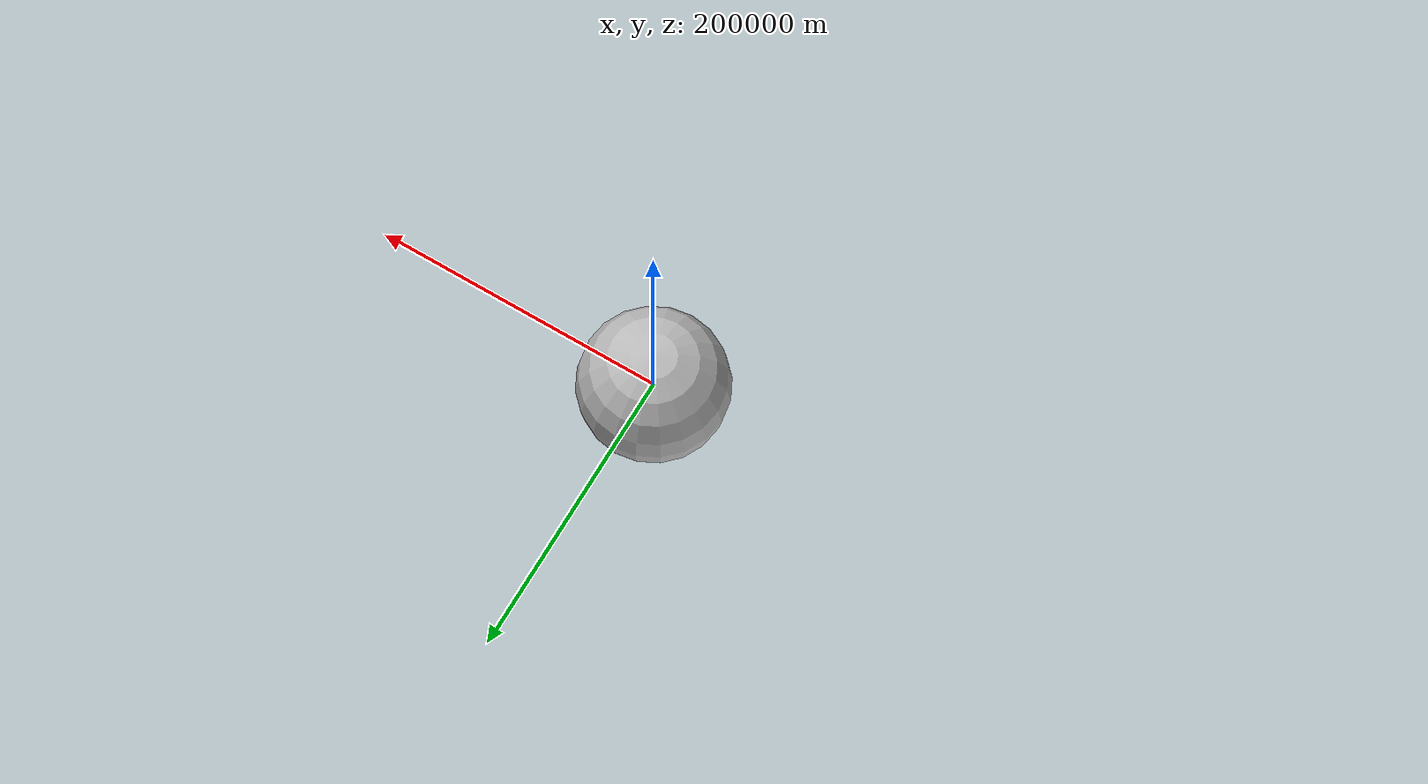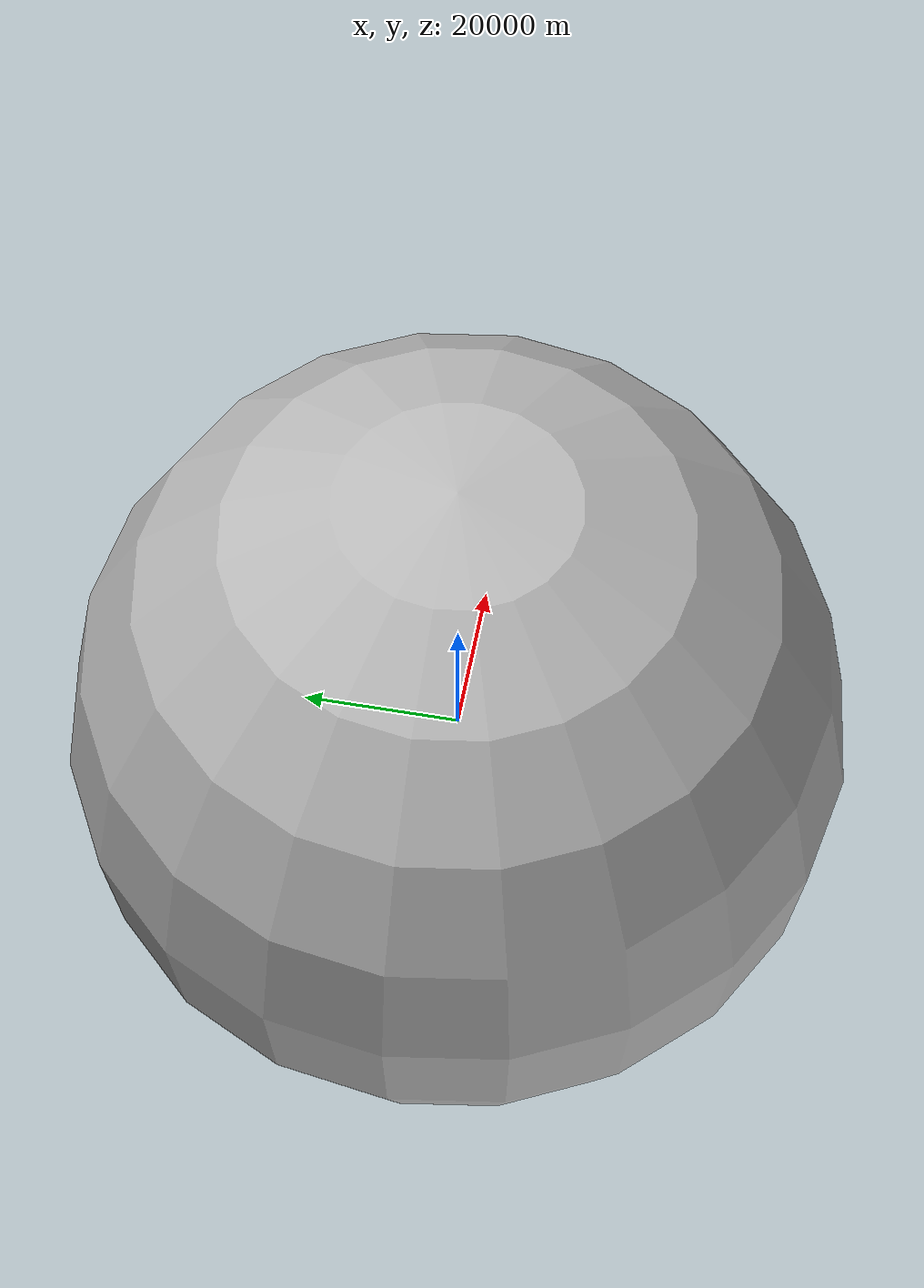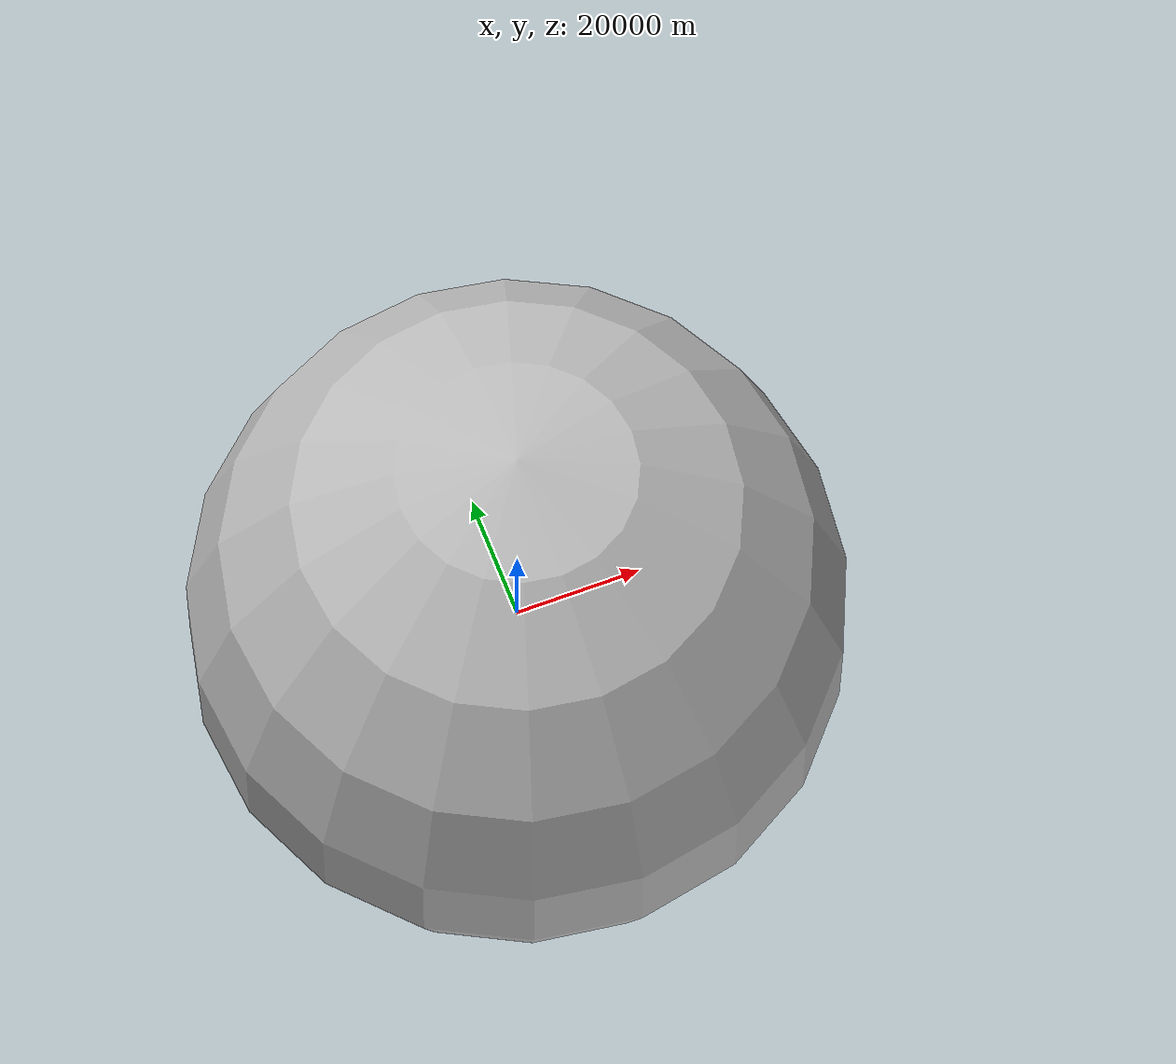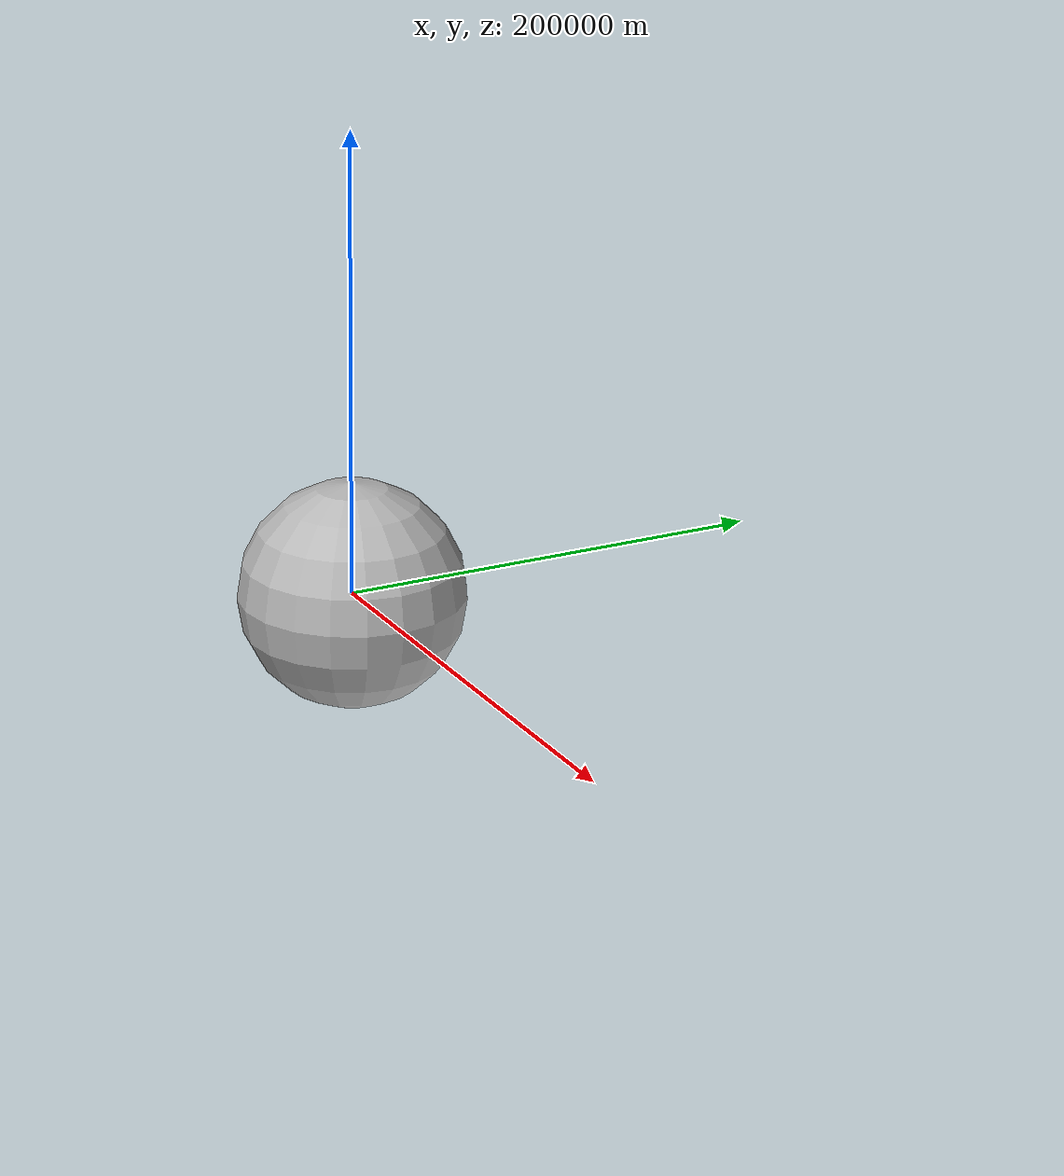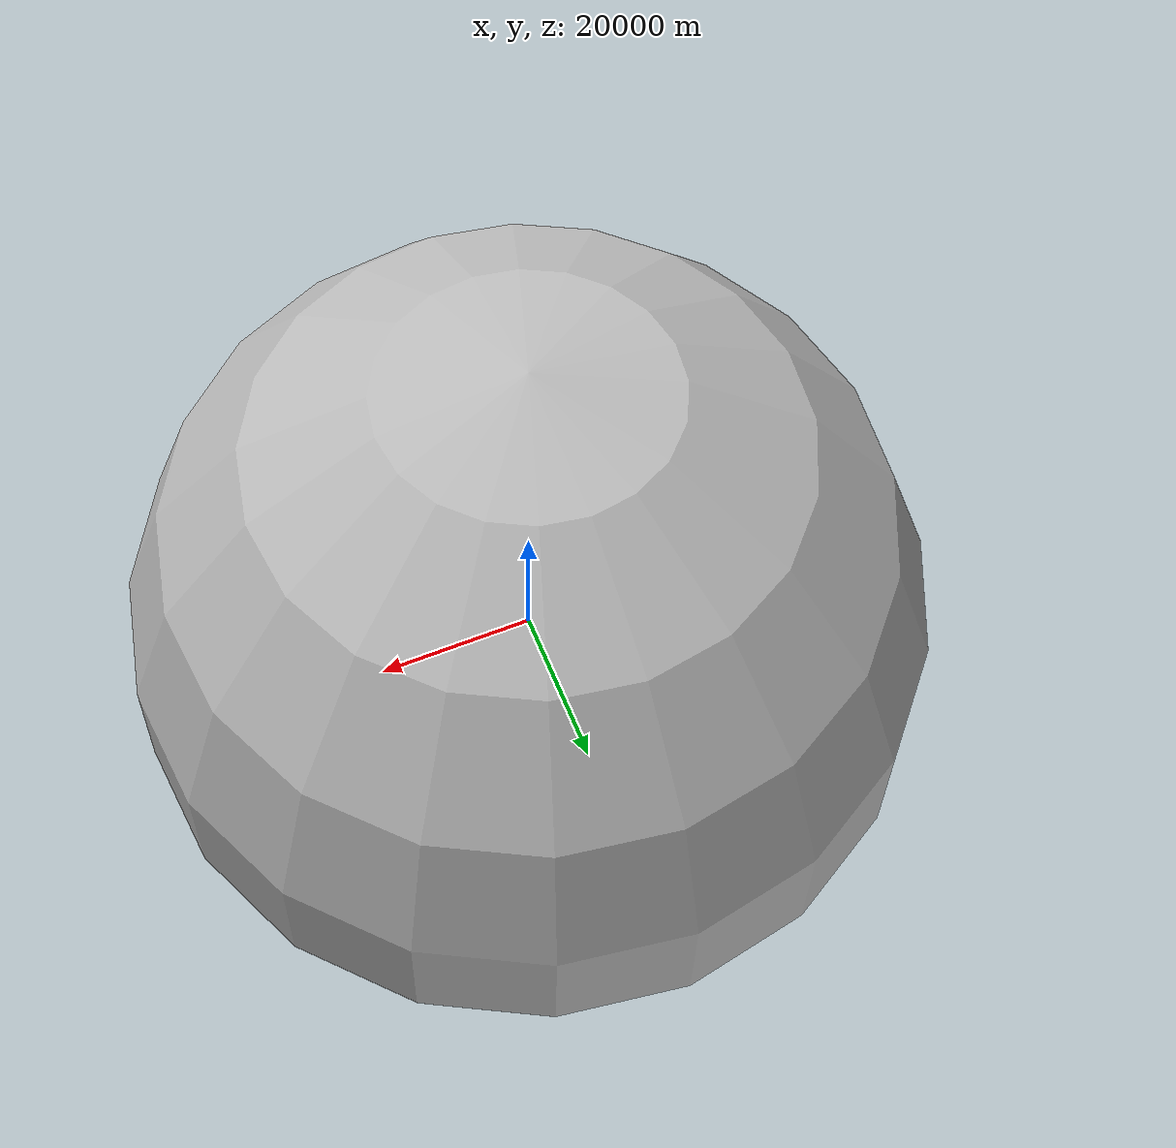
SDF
<sdf version="1.6">
 <world name="default">
  <light name="sun" type="directional">
   <pose>0 0 10 0 -0 0</pose>
   <diffuse>0.8 0.8 0.8 1</diffuse>
   <specular>0.2 0.2 0.2 1</specular>
   <attenuation>
    <range>1000</range>
    <constant>0.9</constant>
    <linear>0.01</linear>
    <quadratic>0.001</quadratic>
   </attenuation>
   <direction>-0.5 0.1 -0.9</direction>
  </light>
  <gravity>0 0 -9.8</gravity>
  <magnetic_field>6e-06 2.3e-05 -4.2e-05</magnetic_field>
  <atmosphere type="adiabatic"/>
  <physics name="default_physics" default="0" type="ode">
   <max_step_size>0.001</max_step_size>
   <real_time_factor>1</real_time_factor>
   <real_time_update_rate>1000</real_time_update_rate>
  </physics>
  <scene><ambient>0.4 0.4 0.4 1</ambient><background>0.7 0.7 0.7 1</background><shadows>1</shadows></scene>
  <audio><device>default</device></audio>
  <spherical_coordinates>
   <surface_model>EARTH_WGS84</surface_model>
   <latitude_deg>0</latitude_deg>
   <longitude_deg>0</longitude_deg>
   <elevation>0</elevation>
   <heading_deg>0</heading_deg>
  </spherical_coordinates>
  <model name="table_clone">
   <static>1</static>
   <link name="link">
    <collision name="surface">
     <pose>0 0 1 0 -0 0</pose>
     <geometry><box><size>1.5 0.8 0.03</size></box></geometry>
     <surface><friction><ode><mu>0.6</mu><mu2>0.6</mu2></ode></friction></surface>
    </collision>
    <visual name="visual1">
     <pose>0 0 1 0 -0 0</pose>
     <geometry><box><size>1.5 0.8 0.03</size></box></geometry>
     <material>
      <script><uri>file://media/materials/scripts/gazebo.material</uri><name>Gazebo/Wood</name></script>
     </material>
    </visual>
    <collision name="front_left_leg">
     <pose>0.68 0.38 0.5 0 -0 0</pose>
     <geometry><cylinder><radius>0.02</radius><length>1</length></cylinder></geometry>
    </collision>
    <visual name="front_left_leg">
     <pose>0.68 0.38 0.5 0 -0 0</pose>
     <geometry><cylinder><radius>0.02</radius><length>1</length></cylinder></geometry>
     <material>
      <script><uri>file://media/materials/scripts/gazebo.material</uri><name>Gazebo/Grey</name></script>
     </material>
    </visual>
    <collision name="front_right_leg">
     <pose>0.68 -0.38 0.5 0 -0 0</pose>
     <geometry><cylinder><radius>0.02</radius><length>1</length></cylinder></geometry>
    </collision>
    <visual name="front_right_leg">
     <pose>0.68 -0.38 0.5 0 -0 0</pose>
     <geometry><cylinder><radius>0.02</radius><length>1</length></cylinder></geometry>
     <material>
      <script><uri>file://media/materials/scripts/gazebo.material</uri><name>Gazebo/Grey</name></script>
     </material>
    </visual>
    <collision name="back_right_leg">
     <pose>-0.68 -0.38 0.5 0 -0 0</pose>
     <geometry><cylinder><radius>0.02</radius><length>1</length></cylinder></geometry>
    </collision>
    <visual name="back_right_leg">
     <pose>-0.68 -0.38 0.5 0 -0 0</pose>
     <geometry><cylinder><radius>0.02</radius><length>1</length></cylinder></geometry>
     <material>
      <script><uri>file://media/materials/scripts/gazebo.material</uri><name>Gazebo/Grey</name></script>
     </material>
    </visual>
    <collision name="back_left_leg">
     <pose>-0.68 0.38 0.5 0 -0 0</pose>
     <geometry><cylinder><radius>0.02</radius><length>1</length></cylinder></geometry>
    </collision>
    <visual name="back_left_leg">
     <pose>-0.68 0.38 0.5 0 -0 0</pose>
     <geometry><cylinder><radius>0.02</radius><length>1</length></cylinder></geometry>
     <material>
      <script><uri>file://media/materials/scripts/gazebo.material</uri><name>Gazebo/Grey</name></script>
     </material>
    </visual>
   </link>
   <pose>-0.263897 3.07041 0 0 0 -1.56764</pose>
  </model>
  <model name="table_clone_clone">
   <static>1</static>
   <link name="link">
    <collision name="surface">
     <pose>0 0 1 0 -0 0</pose>
     <geometry><box><size>1.5 0.8 0.03</size></box></geometry>
     <surface><friction><ode><mu>0.6</mu><mu2>0.6</mu2></ode></friction></surface>
    </collision>
    <visual name="visual1">
     <pose>0 0 1 0 -0 0</pose>
     <geometry><box><size>1.5 0.8 0.03</size></box></geometry>
     <material>
      <script><uri>file://media/materials/scripts/gazebo.material</uri><name>Gazebo/Wood</name></script>
     </material>
    </visual>
    <collision name="front_left_leg">
     <pose>0.68 0.38 0.5 0 -0 0</pose>
     <geometry><cylinder><radius>0.02</radius><length>1</length></cylinder></geometry>
    </collision>
    <visual name="front_left_leg">
     <pose>0.68 0.38 0.5 0 -0 0</pose>
     <geometry><cylinder><radius>0.02</radius><length>1</length></cylinder></geometry>
     <material>
      <script><uri>file://media/materials/scripts/gazebo.material</uri><name>Gazebo/Grey</name></script>
     </material>
    </visual>
    <collision name="front_right_leg">
     <pose>0.68 -0.38 0.5 0 -0 0</pose>
     <geometry><cylinder><radius>0.02</radius><length>1</length></cylinder></geometry>
    </collision>
    <visual name="front_right_leg">
     <pose>0.68 -0.38 0.5 0 -0 0</pose>
     <geometry><cylinder><radius>0.02</radius><length>1</length></cylinder></geometry>
     <material>
      <script><uri>file://media/materials/scripts/gazebo.material</uri><name>Gazebo/Grey</name></script>
     </material>
    </visual>
    <collision name="back_right_leg">
     <pose>-0.68 -0.38 0.5 0 -0 0</pose>
     <geometry><cylinder><radius>0.02</radius><length>1</length></cylinder></geometry>
    </collision>
    <visual name="back_right_leg">
     <pose>-0.68 -0.38 0.5 0 -0 0</pose>
     <geometry><cylinder><radius>0.02</radius><length>1</length></cylinder></geometry>
     <material>
      <script><uri>file://media/materials/scripts/gazebo.material</uri><name>Gazebo/Grey</name></script>
     </material>
    </visual>
    <collision name="back_left_leg">
     <pose>-0.68 0.38 0.5 0 -0 0</pose>
     <geometry><cylinder><radius>0.02</radius><length>1</length></cylinder></geometry>
    </collision>
    <visual name="back_left_leg">
     <pose>-0.68 0.38 0.5 0 -0 0</pose>
     <geometry><cylinder><radius>0.02</radius><length>1</length></cylinder></geometry>
     <material>
      <script><uri>file://media/materials/scripts/gazebo.material</uri><name>Gazebo/Grey</name></script>
     </material>
    </visual>
   </link>
   <pose>-0.280452 -1.87389 0 0 0 -1.56764</pose>
  </model>
  <model name="table_clone_clone_0">
   <static>1</static>
   <link name="link">
    <collision name="surface">
     <pose>0 0 1 0 -0 0</pose>
     <geometry><box><size>1.5 0.8 0.03</size></box></geometry>
     <surface><friction><ode><mu>0.6</mu><mu2>0.6</mu2></ode></friction></surface>
    </collision>
    <visual name="visual1">
     <pose>0 0 1 0 -0 0</pose>
     <geometry><box><size>1.5 0.8 0.03</size></box></geometry>
     <material>
      <script><uri>file://media/materials/scripts/gazebo.material</uri><name>Gazebo/Wood</name></script>
     </material>
    </visual>
    <collision name="front_left_leg">
     <pose>0.68 0.38 0.5 0 -0 0</pose>
     <geometry><cylinder><radius>0.02</radius><length>1</length></cylinder></geometry>
    </collision>
    <visual name="front_left_leg">
     <pose>0.68 0.38 0.5 0 -0 0</pose>
     <geometry><cylinder><radius>0.02</radius><length>1</length></cylinder></geometry>
     <material>
      <script><uri>file://media/materials/scripts/gazebo.material</uri><name>Gazebo/Grey</name></script>
     </material>
    </visual>
    <collision name="front_right_leg">
     <pose>0.68 -0.38 0.5 0 -0 0</pose>
     <geometry><cylinder><radius>0.02</radius><length>1</length></cylinder></geometry>
    </collision>
    <visual name="front_right_leg">
     <pose>0.68 -0.38 0.5 0 -0 0</pose>
     <geometry><cylinder><radius>0.02</radius><length>1</length></cylinder></geometry>
     <material>
      <script><uri>file://media/materials/scripts/gazebo.material</uri><name>Gazebo/Grey</name></script>
     </material>
    </visual>
    <collision name="back_right_leg">
     <pose>-0.68 -0.38 0.5 0 -0 0</pose>
     <geometry><cylinder><radius>0.02</radius><length>1</length></cylinder></geometry>
    </collision>
    <visual name="back_right_leg">
     <pose>-0.68 -0.38 0.5 0 -0 0</pose>
     <geometry><cylinder><radius>0.02</radius><length>1</length></cylinder></geometry>
     <material>
      <script><uri>file://media/materials/scripts/gazebo.material</uri><name>Gazebo/Grey</name></script>
     </material>
    </visual>
    <collision name="back_left_leg">
     <pose>-0.68 0.38 0.5 0 -0 0</pose>
     <geometry><cylinder><radius>0.02</radius><length>1</length></cylinder></geometry>
    </collision>
    <visual name="back_left_leg">
     <pose>-0.68 0.38 0.5 0 -0 0</pose>
     <geometry><cylinder><radius>0.02</radius><length>1</length></cylinder></geometry>
     <material>
      <script><uri>file://media/materials/scripts/gazebo.material</uri><name>Gazebo/Grey</name></script>
     </material>
    </visual>
   </link>
   <pose>-0.311266 7.9439 0 0 0 -1.56764</pose>
  </model>
  <model name="table_clone_clone_1">
   <static>1</static>
   <link name="link">
    <collision name="surface">
     <pose>0 0 1 0 -0 0</pose>
     <geometry><box><size>1.5 0.8 0.03</size></box></geometry>
     <surface><friction><ode><mu>0.6</mu><mu2>0.6</mu2></ode></friction></surface>
    </collision>
    <visual name="visual1">
     <pose>0 0 1 0 -0 0</pose>
     <geometry><box><size>1.5 0.8 0.03</size></box></geometry>
     <material>
      <script><uri>file://media/materials/scripts/gazebo.material</uri><name>Gazebo/Wood</name></script>
     </material>
    </visual>
    <collision name="front_left_leg">
     <pose>0.68 0.38 0.5 0 -0 0</pose>
     <geometry><cylinder><radius>0.02</radius><length>1</length></cylinder></geometry>
    </collision>
    <visual name="front_left_leg">
     <pose>0.68 0.38 0.5 0 -0 0</pose>
     <geometry><cylinder><radius>0.02</radius><length>1</length></cylinder></geometry>
     <material>
      <script><uri>file://media/materials/scripts/gazebo.material</uri><name>Gazebo/Grey</name></script>
     </material>
    </visual>
    <collision name="front_right_leg">
     <pose>0.68 -0.38 0.5 0 -0 0</pose>
     <geometry><cylinder><radius>0.02</radius><length>1</length></cylinder></geometry>
    </collision>
    <visual name="front_right_leg">
     <pose>0.68 -0.38 0.5 0 -0 0</pose>
     <geometry><cylinder><radius>0.02</radius><length>1</length></cylinder></geometry>
     <material>
      <script><uri>file://media/materials/scripts/gazebo.material</uri><name>Gazebo/Grey</name></script>
     </material>
    </visual>
    <collision name="back_right_leg">
     <pose>-0.68 -0.38 0.5 0 -0 0</pose>
     <geometry><cylinder><radius>0.02</radius><length>1</length></cylinder></geometry>
    </collision>
    <visual name="back_right_leg">
     <pose>-0.68 -0.38 0.5 0 -0 0</pose>
     <geometry><cylinder><radius>0.02</radius><length>1</length></cylinder></geometry>
     <material>
      <script><uri>file://media/materials/scripts/gazebo.material</uri><name>Gazebo/Grey</name></script>
     </material>
    </visual>
    <collision name="back_left_leg">
     <pose>-0.68 0.38 0.5 0 -0 0</pose>
     <geometry><cylinder><radius>0.02</radius><length>1</length></cylinder></geometry>
    </collision>
    <visual name="back_left_leg">
     <pose>-0.68 0.38 0.5 0 -0 0</pose>
     <geometry><cylinder><radius>0.02</radius><length>1</length></cylinder></geometry>
     <material>
      <script><uri>file://media/materials/scripts/gazebo.material</uri><name>Gazebo/Grey</name></script>
     </material>
    </visual>
   </link>
   <pose>-0.283344 12.903 0 0 0 -1.56764</pose>
  </model>
  <model name="table_clone_clone_2">
   <static>1</static>
   <link name="link">
    <collision name="surface">
     <pose>0 0 1 0 -0 0</pose>
     <geometry><box><size>1.5 0.8 0.03</size></box></geometry>
     <surface><friction><ode><mu>0.6</mu><mu2>0.6</mu2></ode></friction></surface>
    </collision>
    <visual name="visual1">
     <pose>0 0 1 0 -0 0</pose>
     <geometry><box><size>1.5 0.8 0.03</size></box></geometry>
     <material>
      <script><uri>file://media/materials/scripts/gazebo.material</uri><name>Gazebo/Wood</name></script>
     </material>
    </visual>
    <collision name="front_left_leg">
     <pose>0.68 0.38 0.5 0 -0 0</pose>
     <geometry><cylinder><radius>0.02</radius><length>1</length></cylinder></geometry>
    </collision>
    <visual name="front_left_leg">
     <pose>0.68 0.38 0.5 0 -0 0</pose>
     <geometry><cylinder><radius>0.02</radius><length>1</length></cylinder></geometry>
     <material>
      <script><uri>file://media/materials/scripts/gazebo.material</uri><name>Gazebo/Grey</name></script>
     </material>
    </visual>
    <collision name="front_right_leg">
     <pose>0.68 -0.38 0.5 0 -0 0</pose>
     <geometry><cylinder><radius>0.02</radius><length>1</length></cylinder></geometry>
    </collision>
    <visual name="front_right_leg">
     <pose>0.68 -0.38 0.5 0 -0 0</pose>
     <geometry><cylinder><radius>0.02</radius><length>1</length></cylinder></geometry>
     <material>
      <script><uri>file://media/materials/scripts/gazebo.material</uri><name>Gazebo/Grey</name></script>
     </material>
    </visual>
    <collision name="back_right_leg">
     <pose>-0.68 -0.38 0.5 0 -0 0</pose>
     <geometry><cylinder><radius>0.02</radius><length>1</length></cylinder></geometry>
    </collision>
    <visual name="back_right_leg">
     <pose>-0.68 -0.38 0.5 0 -0 0</pose>
     <geometry><cylinder><radius>0.02</radius><length>1</length></cylinder></geometry>
     <material>
      <script><uri>file://media/materials/scripts/gazebo.material</uri><name>Gazebo/Grey</name></script>
     </material>
    </visual>
    <collision name="back_left_leg">
     <pose>-0.68 0.38 0.5 0 -0 0</pose>
     <geometry><cylinder><radius>0.02</radius><length>1</length></cylinder></geometry>
    </collision>
    <visual name="back_left_leg">
     <pose>-0.68 0.38 0.5 0 -0 0</pose>
     <geometry><cylinder><radius>0.02</radius><length>1</length></cylinder></geometry>
     <material>
      <script><uri>file://media/materials/scripts/gazebo.material</uri><name>Gazebo/Grey</name></script>
     </material>
    </visual>
   </link>
   <pose>-0.282545 17.6818 0 0 0 -1.56764</pose>
  </model>
  <model name="table_clone_clone_3">
   <static>1</static>
   <link name="link">
    <collision name="surface">
     <pose>0 0 1 0 -0 0</pose>
     <geometry><box><size>1.5 0.8 0.03</size></box></geometry>
     <surface><friction><ode><mu>0.6</mu><mu2>0.6</mu2></ode></friction></surface>
    </collision>
    <visual name="visual1">
     <pose>0 0 1 0 -0 0</pose>
     <geometry><box><size>1.5 0.8 0.03</size></box></geometry>
     <material>
      <script><uri>file://media/materials/scripts/gazebo.material</uri><name>Gazebo/Wood</name></script>
     </material>
    </visual>
    <collision name="front_left_leg">
     <pose>0.68 0.38 0.5 0 -0 0</pose>
     <geometry><cylinder><radius>0.02</radius><length>1</length></cylinder></geometry>
    </collision>
    <visual name="front_left_leg">
     <pose>0.68 0.38 0.5 0 -0 0</pose>
     <geometry><cylinder><radius>0.02</radius><length>1</length></cylinder></geometry>
     <material>
      <script><uri>file://media/materials/scripts/gazebo.material</uri><name>Gazebo/Grey</name></script>
     </material>
    </visual>
    <collision name="front_right_leg">
     <pose>0.68 -0.38 0.5 0 -0 0</pose>
     <geometry><cylinder><radius>0.02</radius><length>1</length></cylinder></geometry>
    </collision>
    <visual name="front_right_leg">
     <pose>0.68 -0.38 0.5 0 -0 0</pose>
     <geometry><cylinder><radius>0.02</radius><length>1</length></cylinder></geometry>
     <material>
      <script><uri>file://media/materials/scripts/gazebo.material</uri><name>Gazebo/Grey</name></script>
     </material>
    </visual>
    <collision name="back_right_leg">
     <pose>-0.68 -0.38 0.5 0 -0 0</pose>
     <geometry><cylinder><radius>0.02</radius><length>1</length></cylinder></geometry>
    </collision>
    <visual name="back_right_leg">
     <pose>-0.68 -0.38 0.5 0 -0 0</pose>
     <geometry><cylinder><radius>0.02</radius><length>1</length></cylinder></geometry>
     <material>
      <script><uri>file://media/materials/scripts/gazebo.material</uri><name>Gazebo/Grey</name></script>
     </material>
    </visual>
    <collision name="back_left_leg">
     <pose>-0.68 0.38 0.5 0 -0 0</pose>
     <geometry><cylinder><radius>0.02</radius><length>1</length></cylinder></geometry>
    </collision>
    <visual name="back_left_leg">
     <pose>-0.68 0.38 0.5 0 -0 0</pose>
     <geometry><cylinder><radius>0.02</radius><length>1</length></cylinder></geometry>
     <material>
      <script><uri>file://media/materials/scripts/gazebo.material</uri><name>Gazebo/Grey</name></script>
     </material>
    </visual>
   </link>
   <pose>-0.292 22.6184 0 0 0 -1.56764</pose>
  </model>
  <model name="table_clone_clone_4">
   <static>1</static>
   <link name="link">
    <collision name="surface">
     <pose>0 0 1 0 -0 0</pose>
     <geometry><box><size>1.5 0.8 0.03</size></box></geometry>
     <surface><friction><ode><mu>0.6</mu><mu2>0.6</mu2></ode></friction></surface>
    </collision>
    <visual name="visual1">
     <pose>0 0 1 0 -0 0</pose>
     <geometry><box><size>1.5 0.8 0.03</size></box></geometry>
     <material>
      <script><uri>file://media/materials/scripts/gazebo.material</uri><name>Gazebo/Wood</name></script>
     </material>
    </visual>
    <collision name="front_left_leg">
     <pose>0.68 0.38 0.5 0 -0 0</pose>
     <geometry><cylinder><radius>0.02</radius><length>1</length></cylinder></geometry>
    </collision>
    <visual name="front_left_leg">
     <pose>0.68 0.38 0.5 0 -0 0</pose>
     <geometry><cylinder><radius>0.02</radius><length>1</length></cylinder></geometry>
     <material>
      <script><uri>file://media/materials/scripts/gazebo.material</uri><name>Gazebo/Grey</name></script>
     </material>
    </visual>
    <collision name="front_right_leg">
     <pose>0.68 -0.38 0.5 0 -0 0</pose>
     <geometry><cylinder><radius>0.02</radius><length>1</length></cylinder></geometry>
    </collision>
    <visual name="front_right_leg">
     <pose>0.68 -0.38 0.5 0 -0 0</pose>
     <geometry><cylinder><radius>0.02</radius><length>1</length></cylinder></geometry>
     <material>
      <script><uri>file://media/materials/scripts/gazebo.material</uri><name>Gazebo/Grey</name></script>
     </material>
    </visual>
    <collision name="back_right_leg">
     <pose>-0.68 -0.38 0.5 0 -0 0</pose>
     <geometry><cylinder><radius>0.02</radius><length>1</length></cylinder></geometry>
    </collision>
    <visual name="back_right_leg">
     <pose>-0.68 -0.38 0.5 0 -0 0</pose>
     <geometry><cylinder><radius>0.02</radius><length>1</length></cylinder></geometry>
     <material>
      <script><uri>file://media/materials/scripts/gazebo.material</uri><name>Gazebo/Grey</name></script>
     </material>
    </visual>
    <collision name="back_left_leg">
     <pose>-0.68 0.38 0.5 0 -0 0</pose>
     <geometry><cylinder><radius>0.02</radius><length>1</length></cylinder></geometry>
    </collision>
    <visual name="back_left_leg">
     <pose>-0.68 0.38 0.5 0 -0 0</pose>
     <geometry><cylinder><radius>0.02</radius><length>1</length></cylinder></geometry>
     <material>
      <script><uri>file://media/materials/scripts/gazebo.material</uri><name>Gazebo/Grey</name></script>
     </material>
    </visual>
   </link>
   <pose>-0.3 27.7319 0 0 0 -1.56764</pose>
  </model>
  <model name="table_clone_clone_5">
   <static>1</static>
   <link name="link">
    <collision name="surface">
     <pose>0 0 1 0 -0 0</pose>
     <geometry><box><size>1.5 0.8 0.03</size></box></geometry>
     <surface><friction><ode><mu>0.6</mu><mu2>0.6</mu2></ode></friction></surface>
    </collision>
    <visual name="visual1">
     <pose>0 0 1 0 -0 0</pose>
     <geometry><box><size>1.5 0.8 0.03</size></box></geometry>
     <material>
      <script><uri>file://media/materials/scripts/gazebo.material</uri><name>Gazebo/Wood</name></script>
     </material>
    </visual>
    <collision name="front_left_leg">
     <pose>0.68 0.38 0.5 0 -0 0</pose>
     <geometry><cylinder><radius>0.02</radius><length>1</length></cylinder></geometry>
    </collision>
    <visual name="front_left_leg">
     <pose>0.68 0.38 0.5 0 -0 0</pose>
     <geometry><cylinder><radius>0.02</radius><length>1</length></cylinder></geometry>
     <material>
      <script><uri>file://media/materials/scripts/gazebo.material</uri><name>Gazebo/Grey</name></script>
     </material>
    </visual>
    <collision name="front_right_leg">
     <pose>0.68 -0.38 0.5 0 -0 0</pose>
     <geometry><cylinder><radius>0.02</radius><length>1</length></cylinder></geometry>
    </collision>
    <visual name="front_right_leg">
     <pose>0.68 -0.38 0.5 0 -0 0</pose>
     <geometry><cylinder><radius>0.02</radius><length>1</length></cylinder></geometry>
     <material>
      <script><uri>file://media/materials/scripts/gazebo.material</uri><name>Gazebo/Grey</name></script>
     </material>
    </visual>
    <collision name="back_right_leg">
     <pose>-0.68 -0.38 0.5 0 -0 0</pose>
     <geometry><cylinder><radius>0.02</radius><length>1</length></cylinder></geometry>
    </collision>
    <visual name="back_right_leg">
     <pose>-0.68 -0.38 0.5 0 -0 0</pose>
     <geometry><cylinder><radius>0.02</radius><length>1</length></cylinder></geometry>
     <material>
      <script><uri>file://media/materials/scripts/gazebo.material</uri><name>Gazebo/Grey</name></script>
     </material>
    </visual>
    <collision name="back_left_leg">
     <pose>-0.68 0.38 0.5 0 -0 0</pose>
     <geometry><cylinder><radius>0.02</radius><length>1</length></cylinder></geometry>
    </collision>
    <visual name="back_left_leg">
     <pose>-0.68 0.38 0.5 0 -0 0</pose>
     <geometry><cylinder><radius>0.02</radius><length>1</length></cylinder></geometry>
     <material>
      <script><uri>file://media/materials/scripts/gazebo.material</uri><name>Gazebo/Grey</name></script>
     </material>
    </visual>
   </link>
   <pose>8.83949 -8.39116 0 0 -0 0</pose>
  </model>
  <model name="table_clone_clone_5_clone">
   <static>1</static>
   <link name="link">
    <collision name="surface">
     <pose>0 0 1 0 -0 0</pose>
     <geometry><box><size>1.5 0.8 0.03</size></box></geometry>
     <surface><friction><ode><mu>0.6</mu><mu2>0.6</mu2></ode></friction></surface>
    </collision>
    <visual name="visual1">
     <pose>0 0 1 0 -0 0</pose>
     <geometry><box><size>1.5 0.8 0.03</size></box></geometry>
     <material>
      <script><uri>file://media/materials/scripts/gazebo.material</uri><name>Gazebo/Wood</name></script>
     </material>
    </visual>
    <collision name="front_left_leg">
     <pose>0.68 0.38 0.5 0 -0 0</pose>
     <geometry><cylinder><radius>0.02</radius><length>1</length></cylinder></geometry>
    </collision>
    <visual name="front_left_leg">
     <pose>0.68 0.38 0.5 0 -0 0</pose>
     <geometry><cylinder><radius>0.02</radius><length>1</length></cylinder></geometry>
     <material>
      <script><uri>file://media/materials/scripts/gazebo.material</uri><name>Gazebo/Grey</name></script>
     </material>
    </visual>
    <collision name="front_right_leg">
     <pose>0.68 -0.38 0.5 0 -0 0</pose>
     <geometry><cylinder><radius>0.02</radius><length>1</length></cylinder></geometry>
    </collision>
    <visual name="front_right_leg">
     <pose>0.68 -0.38 0.5 0 -0 0</pose>
     <geometry><cylinder><radius>0.02</radius><length>1</length></cylinder></geometry>
     <material>
      <script><uri>file://media/materials/scripts/gazebo.material</uri><name>Gazebo/Grey</name></script>
     </material>
    </visual>
    <collision name="back_right_leg">
     <pose>-0.68 -0.38 0.5 0 -0 0</pose>
     <geometry><cylinder><radius>0.02</radius><length>1</length></cylinder></geometry>
    </collision>
    <visual name="back_right_leg">
     <pose>-0.68 -0.38 0.5 0 -0 0</pose>
     <geometry><cylinder><radius>0.02</radius><length>1</length></cylinder></geometry>
     <material>
      <script><uri>file://media/materials/scripts/gazebo.material</uri><name>Gazebo/Grey</name></script>
     </material>
    </visual>
    <collision name="back_left_leg">
     <pose>-0.68 0.38 0.5 0 -0 0</pose>
     <geometry><cylinder><radius>0.02</radius><length>1</length></cylinder></geometry>
    </collision>
    <visual name="back_left_leg">
     <pose>-0.68 0.38 0.5 0 -0 0</pose>
     <geometry><cylinder><radius>0.02</radius><length>1</length></cylinder></geometry>
     <material>
      <script><uri>file://media/materials/scripts/gazebo.material</uri><name>Gazebo/Grey</name></script>
     </material>
    </visual>
   </link>
   <pose>4.1841 -8.37674 0 0 -0 0</pose>
  </model>
  <model name="table_clone_clone_5_clone_0">
   <static>1</static>
   <link name="link">
    <collision name="surface">
     <pose>0 0 1 0 -0 0</pose>
     <geometry><box><size>1.5 0.8 0.03</size></box></geometry>
     <surface><friction><ode><mu>0.6</mu><mu2>0.6</mu2></ode></friction></surface>
    </collision>
    <visual name="visual1">
     <pose>0 0 1 0 -0 0</pose>
     <geometry><box><size>1.5 0.8 0.03</size></box></geometry>
     <material>
      <script><uri>file://media/materials/scripts/gazebo.material</uri><name>Gazebo/Wood</name></script>
     </material>
    </visual>
    <collision name="front_left_leg">
     <pose>0.68 0.38 0.5 0 -0 0</pose>
     <geometry><cylinder><radius>0.02</radius><length>1</length></cylinder></geometry>
    </collision>
    <visual name="front_left_leg">
     <pose>0.68 0.38 0.5 0 -0 0</pose>
     <geometry><cylinder><radius>0.02</radius><length>1</length></cylinder></geometry>
     <material>
      <script><uri>file://media/materials/scripts/gazebo.material</uri><name>Gazebo/Grey</name></script>
     </material>
    </visual>
    <collision name="front_right_leg">
     <pose>0.68 -0.38 0.5 0 -0 0</pose>
     <geometry><cylinder><radius>0.02</radius><length>1</length></cylinder></geometry>
    </collision>
    <visual name="front_right_leg">
     <pose>0.68 -0.38 0.5 0 -0 0</pose>
     <geometry><cylinder><radius>0.02</radius><length>1</length></cylinder></geometry>
     <material>
      <script><uri>file://media/materials/scripts/gazebo.material</uri><name>Gazebo/Grey</name></script>
     </material>
    </visual>
    <collision name="back_right_leg">
     <pose>-0.68 -0.38 0.5 0 -0 0</pose>
     <geometry><cylinder><radius>0.02</radius><length>1</length></cylinder></geometry>
    </collision>
    <visual name="back_right_leg">
     <pose>-0.68 -0.38 0.5 0 -0 0</pose>
     <geometry><cylinder><radius>0.02</radius><length>1</length></cylinder></geometry>
     <material>
      <script><uri>file://media/materials/scripts/gazebo.material</uri><name>Gazebo/Grey</name></script>
     </material>
    </visual>
    <collision name="back_left_leg">
     <pose>-0.68 0.38 0.5 0 -0 0</pose>
     <geometry><cylinder><radius>0.02</radius><length>1</length></cylinder></geometry>
    </collision>
    <visual name="back_left_leg">
     <pose>-0.68 0.38 0.5 0 -0 0</pose>
     <geometry><cylinder><radius>0.02</radius><length>1</length></cylinder></geometry>
     <material>
      <script><uri>file://media/materials/scripts/gazebo.material</uri><name>Gazebo/Grey</name></script>
     </material>
    </visual>
   </link>
   <pose>-0.816001 -8.38126 0 0 -0 0</pose>
  </model>
  <model name="bookshelf">
   <static>1</static>
   <link name="link">
    <inertial><mass>1</mass></inertial>
    <collision name="back">
     <pose>0 0.005 0.6 0 -0 0</pose>
     <geometry><box><size>0.9 0.01 1.2</size></box></geometry>
    </collision>
    <visual name="visual1">
     <pose>0 0.005 0.6 0 -0 0</pose>
     <geometry><box><size>0.9 0.01 1.2</size></box></geometry>
     <material>
      <script><uri>file://media/materials/scripts/gazebo.material</uri><name>Gazebo/Wood</name></script>
     </material>
    </visual>
    <collision name="left_side">
     <pose>0.45 -0.195 0.6 0 -0 0</pose>
     <geometry><box><size>0.02 0.4 1.2</size></box></geometry>
    </collision>
    <visual name="visual2">
     <pose>0.45 -0.195 0.6 0 -0 0</pose>
     <geometry><box><size>0.02 0.4 1.2</size></box></geometry>
     <material>
      <script><uri>file://media/materials/scripts/gazebo.material</uri><name>Gazebo/Wood</name></script>
     </material>
    </visual>
    <collision name="right_side">
     <pose>-0.45 -0.195 0.6 0 -0 0</pose>
     <geometry><box><size>0.02 0.4 1.2</size></box></geometry>
    </collision>
    <visual name="visual3">
     <pose>-0.45 -0.195 0.6 0 -0 0</pose>
     <geometry><box><size>0.02 0.4 1.2</size></box></geometry>
     <material>
      <script><uri>file://media/materials/scripts/gazebo.material</uri><name>Gazebo/Wood</name></script>
     </material>
    </visual>
    <collision name="bottom">
     <pose>0 -0.195 0.03 0 -0 0</pose>
     <geometry><box><size>0.88 0.4 0.06</size></box></geometry>
    </collision>
    <visual name="visual4">
     <pose>0 -0.195 0.03 0 -0 0</pose>
     <geometry><box><size>0.88 0.4 0.06</size></box></geometry>
     <material>
      <script><uri>file://media/materials/scripts/gazebo.material</uri><name>Gazebo/Wood</name></script>
     </material>
    </visual>
    <collision name="top">
     <pose>0 -0.195 1.19 0 -0 0</pose>
     <geometry><box><size>0.88 0.4 0.02</size></box></geometry>
    </collision>
    <visual name="visual5">
     <pose>0 -0.195 1.19 0 -0 0</pose>
     <geometry><box><size>0.88 0.4 0.02</size></box></geometry>
     <material>
      <script><uri>file://media/materials/scripts/gazebo.material</uri><name>Gazebo/Wood</name></script>
     </material>
    </visual>
    <collision name="low_shelf">
     <pose>0 -0.195 0.43 0 -0 0</pose>
     <geometry><box><size>0.88 0.4 0.02</size></box></geometry>
    </collision>
    <visual name="visual6">
     <pose>0 -0.195 0.43 0 -0 0</pose>
     <geometry><box><size>0.88 0.4 0.02</size></box></geometry>
     <material>
      <script><uri>file://media/materials/scripts/gazebo.material</uri><name>Gazebo/Wood</name></script>
     </material>
    </visual>
    <collision name="high_shelf">
     <pose>0 -0.195 0.8 0 -0 0</pose>
     <geometry><box><size>0.88 0.4 0.02</size></box></geometry>
    </collision>
    <visual name="visual7">
     <pose>0 -0.195 0.8 0 -0 0</pose>
     <geometry><box><size>0.88 0.4 0.02</size></box></geometry>
     <material>
      <script><uri>file://media/materials/scripts/gazebo.material</uri><name>Gazebo/Wood</name></script>
     </material>
    </visual>
   </link>
   <pose>-4.34494 32.0429 0 0 -0 1.57907</pose>
  </model>
  <model name="L_wall_wood">
   <pose>1.29872 -8.7033 0 0 -0 0</pose>
   <link name="Wall_14">
    <collision name="Wall_14_Collision">
     <geometry><box><size>4.25 2.5 0.5</size></box></geometry>
     <pose>0 0 0.25 0 -0 0</pose>
    </collision>
    <visual name="Wall_14_Visual">
     <pose>0 0 0.25 0 -0 0</pose>
     <geometry><box><size>4.25 2.5 0.5</size></box></geometry>
     <material>
      <script><uri>file://media/materials/scripts/gazebo.material</uri><name>Gazebo/Wood</name></script>
      <ambient>1 1 1 1</ambient>
     </material>
     <meta><layer>0</layer></meta>
    </visual>
    <pose>6.238 -1.377 0 0 -0 0</pose>
   </link>
   <link name="Wall_16">
    <collision name="Wall_16_Collision">
     <geometry><box><size>4.25 2.5 0.5</size></box></geometry>
     <pose>0 0 0.25 0 -0 0</pose>
    </collision>
    <visual name="Wall_16_Visual">
     <pose>0 0 0.25 0 -0 0</pose>
     <geometry><box><size>4.25 2.5 0.5</size></box></geometry>
     <material>
      <script><uri>file://media/materials/scripts/gazebo.material</uri><name>Gazebo/Wood</name></script>
      <ambient>1 1 1 1</ambient>
     </material>
     <meta><layer>0</layer></meta>
    </visual>
    <pose>1.505 -1.377 0 0 -0 3.14159</pose>
   </link>
   <link name="Wall_18">
    <collision name="Wall_18_Collision">
     <geometry><box><size>4.25 2.5 0.5</size></box></geometry>
     <pose>0 0 0.25 0 -0 0</pose>
    </collision>
    <visual name="Wall_18_Visual">
     <pose>0 0 0.25 0 -0 0</pose>
     <geometry><box><size>4.25 2.5 0.5</size></box></geometry>
     <material>
      <script><uri>file://media/materials/scripts/gazebo.material</uri><name>Gazebo/Wood</name></script>
      <ambient>1 1 1 1</ambient>
     </material>
     <meta><layer>0</layer></meta>
    </visual>
    <pose>-3.485 -1.377 0 0 -0 3.14159</pose>
   </link>
   <link name="Wall_20">
    <collision name="Wall_20_Collision">
     <geometry><box><size>4.25 2.5 0.5</size></box></geometry>
     <pose>0 0 0.25 0 -0 0</pose>
    </collision>
    <visual name="Wall_20_Visual">
     <pose>0 0 0.25 0 -0 0</pose>
     <geometry><box><size>4.25 2.5 0.5</size></box></geometry>
     <material>
      <script><uri>file://media/materials/scripts/gazebo.material</uri><name>Gazebo/Wood</name></script>
      <ambient>1 1 1 1</ambient>
     </material>
     <meta><layer>0</layer></meta>
    </visual>
    <pose>-7.113 0.502 0 0 -0 1.5708</pose>
   </link>
   <static>1</static>
  </model>
  <model name="screen_1">
   <pose>9.6 6.558 0 0 -0 0</pose>
   <link name="Wall_15">
    <collision name="Wall_15_Collision">
     <geometry><box><size>4.65 0.15 2.5</size></box></geometry>
     <pose>0 0 1.25 0 -0 0</pose>
    </collision>
    <visual name="Wall_15_Visual">
     <pose>0 0 1.25 0 -0 0</pose>
     <geometry><box><size>4.65 0.15 2.5</size></box></geometry>
     <material>
      <script><uri>file://media/materials/scripts/gazebo.material</uri><name>Gazebo/Grey</name></script>
      <ambient>1 1 1 1</ambient>
     </material>
     <meta><layer>0</layer></meta>
    </visual>
    <pose>0 9.7845 0 0 -0 -1.5708</pose>
   </link>
   <link name="Wall_17">
    <collision name="Wall_17_Collision">
     <geometry><box><size>4.5 0.15 2.5</size></box></geometry>
     <pose>0 0 1.25 0 -0 0</pose>
    </collision>
    <visual name="Wall_17_Visual">
     <pose>0 0 1.25 0 -0 0</pose>
     <geometry><box><size>4.5 0.15 2.5</size></box></geometry>
     <material>
      <script><uri>file://media/materials/scripts/gazebo.material</uri><name>Gazebo/Grey</name></script>
      <ambient>1 1 1 1</ambient>
     </material>
     <meta><layer>0</layer></meta>
    </visual>
    <pose>0 4.8855 0 0 -0 -1.5708</pose>
   </link>
   <link name="Wall_19">
    <collision name="Wall_19_Collision">
     <geometry><box><size>4.25 0.15 2.5</size></box></geometry>
     <pose>0 0 1.25 0 -0 0</pose>
    </collision>
    <visual name="Wall_19_Visual">
     <pose>0 0 1.25 0 -0 0</pose>
     <geometry><box><size>4.25 0.15 2.5</size></box></geometry>
     <material>
      <script><uri>file://media/materials/scripts/gazebo.material</uri><name>Gazebo/Grey</name></script>
      <ambient>1 1 1 1</ambient>
     </material>
     <meta><layer>0</layer></meta>
    </visual>
    <pose>0 0.028499 0 0 -0 -1.5708</pose>
   </link>
   <link name="Wall_21">
    <collision name="Wall_21_Collision">
     <geometry><box><size>4.5 0.15 2.5</size></box></geometry>
     <pose>0 0 1.25 0 -0 0</pose>
    </collision>
    <visual name="Wall_21_Visual">
     <pose>0 0 1.25 0 -0 0</pose>
     <geometry><box><size>4.5 0.15 2.5</size></box></geometry>
     <material>
      <script><uri>file://media/materials/scripts/gazebo.material</uri><name>Gazebo/Grey</name></script>
      <ambient>1 1 1 1</ambient>
     </material>
     <meta><layer>0</layer></meta>
    </visual>
    <pose>0 -4.8845 0 0 -0 1.5708</pose>
   </link>
   <link name="Wall_23">
    <collision name="Wall_23_Collision">
     <geometry><box><size>4.5 0.15 2.5</size></box></geometry>
     <pose>0 0 1.25 0 -0 0</pose>
    </collision>
    <visual name="Wall_23_Visual">
     <pose>0 0 1.25 0 -0 0</pose>
     <geometry><box><size>4.5 0.15 2.5</size></box></geometry>
     <material>
      <script><uri>file://media/materials/scripts/gazebo.material</uri><name>Gazebo/Grey</name></script>
      <ambient>1 1 1 1</ambient>
     </material>
     <meta><layer>0</layer></meta>
    </visual>
    <pose>0 -9.8595 0 0 -0 -1.5708</pose>
   </link>
   <static>1</static>
  </model>
  <model name="screen">
   <pose>9.6 11.7963 0 0 -0 0</pose>
   <link name="Wall_0">
    <collision name="Wall_0_Collision">
     <geometry><box><size>3.75 0.15 2.5</size></box></geometry>
     <pose>0 0 1.25 0 -0 0</pose>
    </collision>
    <visual name="Wall_0_Visual">
     <pose>0 0 1.25 0 -0 0</pose>
     <geometry><box><size>3.75 0.15 2.5</size></box></geometry>
     <material>
      <script><uri>file://media/materials/scripts/gazebo.material</uri><name>Gazebo/Grey</name></script>
      <ambient>1 1 1 1</ambient>
     </material>
     <meta><layer>0</layer></meta>
    </visual>
    <pose>0 -14.926 0 0 -0 -1.5708</pose>
   </link>
   <link name="Wall_11">
    <collision name="Wall_11_Collision">
     <geometry><box><size>4.3 0.15 2.5</size></box></geometry>
     <pose>0 0 1.25 0 -0 0</pose>
    </collision>
    <visual name="Wall_11_Visual">
     <pose>0 0 1.25 0 -0 0</pose>
     <geometry><box><size>4.3 0.15 2.5</size></box></geometry>
     <material>
      <script><uri>file://media/materials/scripts/gazebo.material</uri><name>Gazebo/Grey</name></script>
      <ambient>1 1 1 1</ambient>
     </material>
     <meta><layer>0</layer></meta>
    </visual>
    <pose>0 9.451 0 0 -0 1.5708</pose>
   </link>
   <link name="Wall_13">
    <collision name="Wall_13_Collision">
     <geometry><box><size>4.5 0.15 2.5</size></box></geometry>
     <pose>0 0 1.25 0 -0 0</pose>
    </collision>
    <visual name="Wall_13_Visual">
     <pose>0 0 1.25 0 -0 0</pose>
     <geometry><box><size>4.5 0.15 2.5</size></box></geometry>
     <material>
      <script><uri>file://media/materials/scripts/gazebo.material</uri><name>Gazebo/Grey</name></script>
      <ambient>1 1 1 1</ambient>
     </material>
     <meta><layer>0</layer></meta>
    </visual>
    <pose>0 14.551 0 0 -0 1.5708</pose>
   </link>
   <link name="Wall_2">
    <collision name="Wall_2_Collision">
     <geometry><box><size>3.75 0.15 2.5</size></box></geometry>
     <pose>0 0 1.25 0 -0 0</pose>
    </collision>
    <visual name="Wall_2_Visual">
     <pose>0 0 1.25 0 -0 0</pose>
     <geometry><box><size>3.75 0.15 2.5</size></box></geometry>
     <material>
      <script><uri>file://media/materials/scripts/gazebo.material</uri><name>Gazebo/Grey</name></script>
      <ambient>1 1 1 1</ambient>
     </material>
     <meta><layer>0</layer></meta>
    </visual>
    <pose>0 -10.129 0 0 -0 -1.5708</pose>
   </link>
   <link name="Wall_4">
    <collision name="Wall_4_Collision">
     <geometry><box><size>3.75 0.15 2.5</size></box></geometry>
     <pose>0 0 1.25 0 -0 0</pose>
    </collision>
    <visual name="Wall_4_Visual">
     <pose>0 0 1.25 0 -0 0</pose>
     <geometry><box><size>3.75 0.15 2.5</size></box></geometry>
     <material>
      <script><uri>file://media/materials/scripts/gazebo.material</uri><name>Gazebo/Grey</name></script>
      <ambient>1 1 1 1</ambient>
     </material>
     <meta><layer>0</layer></meta>
    </visual>
    <pose>0 -5.126 0 0 -0 1.5708</pose>
   </link>
   <link name="Wall_6">
    <collision name="Wall_6_Collision">
     <geometry><box><size>3.75 0.15 2.5</size></box></geometry>
     <pose>0 0 1.25 0 -0 0</pose>
    </collision>
    <visual name="Wall_6_Visual">
     <pose>0 0 1.25 0 -0 0</pose>
     <geometry><box><size>3.75 0.15 2.5</size></box></geometry>
     <material>
      <script><uri>file://media/materials/scripts/gazebo.material</uri><name>Gazebo/Grey</name></script>
      <ambient>1 1 1 1</ambient>
     </material>
     <meta><layer>0</layer></meta>
    </visual>
    <pose>0 -0.324 0 0 -0 1.5708</pose>
   </link>
   <link name="Wall_9">
    <collision name="Wall_9_Collision">
     <geometry><box><size>3.75 0.15 2.5</size></box></geometry>
     <pose>0 0 1.25 0 -0 0</pose>
    </collision>
    <visual name="Wall_9_Visual">
     <pose>0 0 1.25 0 -0 0</pose>
     <geometry><box><size>3.75 0.15 2.5</size></box></geometry>
     <material>
      <script><uri>file://media/materials/scripts/gazebo.material</uri><name>Gazebo/Grey</name></script>
      <ambient>1 1 1 1</ambient>
     </material>
     <meta><layer>0</layer></meta>
    </visual>
    <pose>0 4.576 0 0 -0 1.5708</pose>
   </link>
   <static>1</static>
  </model>
  <model name="cut_wall">
   <pose>2.54547 -16.9287 0 0 -0 0</pose>
   <link name="Wall_25">
    <collision name="Wall_25_Collision">
     <geometry><box><size>4.25 0.15 2.5</size></box></geometry>
     <pose>0 0 1.25 0 -0 0</pose>
    </collision>
    <visual name="Wall_25_Visual">
     <pose>0 0 1.25 0 -0 0</pose>
     <geometry><box><size>4.25 0.15 2.5</size></box></geometry>
     <material>
      <script><uri>file://media/materials/scripts/gazebo.material</uri><name>Gazebo/Grey</name></script>
      <ambient>1 1 1 1</ambient>
     </material>
     <meta><layer>0</layer></meta>
    </visual>
    <pose>-4.893 0 0 0 -0 0</pose>
   </link>
   <link name="Wall_27">
    <collision name="Wall_27_Collision">
     <geometry><box><size>4.25 0.15 2.5</size></box></geometry>
     <pose>0 0 1.25 0 -0 0</pose>
    </collision>
    <visual name="Wall_27_Visual">
     <pose>0 0 1.25 0 -0 0</pose>
     <geometry><box><size>4.25 0.15 2.5</size></box></geometry>
     <material>
      <script><uri>file://media/materials/scripts/gazebo.material</uri><name>Gazebo/Grey</name></script>
      <ambient>1 1 1 1</ambient>
     </material>
     <meta><layer>0</layer></meta>
    </visual>
    <pose>-0.022 0 0 0 -0 3.14159</pose>
   </link>
   <link name="Wall_29">
    <collision name="Wall_29_Collision">
     <geometry><box><size>4.25 0.15 2.5</size></box></geometry>
     <pose>0 0 1.25 0 -0 0</pose>
    </collision>
    <visual name="Wall_29_Visual">
     <pose>0 0 1.25 0 -0 0</pose>
     <geometry><box><size>4.25 0.15 2.5</size></box></geometry>
     <material>
      <script><uri>file://media/materials/scripts/gazebo.material</uri><name>Gazebo/Grey</name></script>
      <ambient>1 1 1 1</ambient>
     </material>
     <meta><layer>0</layer></meta>
    </visual>
    <pose>4.893 0 0 0 -0 0</pose>
   </link>
   <static>1</static>
  </model>
  <model name="grey_wall">
   <static>1</static>
   <link name="link">
    <pose>0 0 1.4 0 -0 0</pose>
    <collision name="collision"><geometry><box><size>4 0.2 2.4</size></box></geometry></collision>
    <visual name="visual">
     <cast_shadows>0</cast_shadows>
     <geometry><box><size>4 0.2 2.4</size></box></geometry>
     <material>
      <script>
       <uri>model://grey_wall/materials/scripts</uri>
       <uri>model://grey_wall/materials/textures</uri>
       <name>vrc/grey_wall</name>
      </script>
     </material>
    </visual>
   </link>
   <pose>9.4214 26.2681 -0.13155 0 0 -1.58718</pose>
  </model>
  <model name="grey_wall_clone">
   <static>1</static>
   <link name="link">
    <pose>0 0 1.4 0 -0 0</pose>
    <collision name="collision"><geometry><box><size>4 0.2 2.4</size></box></geometry></collision>
    <visual name="visual">
     <cast_shadows>0</cast_shadows>
     <geometry><box><size>4 0.2 2.4</size></box></geometry>
     <material>
      <script>
       <uri>model://grey_wall/materials/scripts</uri>
       <uri>model://grey_wall/materials/textures</uri>
       <name>vrc/grey_wall</name>
      </script>
     </material>
    </visual>
   </link>
   <pose>9.4357 21.2475 -0.13155 0 0 -1.58718</pose>
  </model>
  <model name="grey_wall_clone_0">
   <static>1</static>
   <link name="link">
    <pose>0 0 1.4 0 -0 0</pose>
    <collision name="collision"><geometry><box><size>4 0.2 2.4</size></box></geometry></collision>
    <visual name="visual">
     <cast_shadows>0</cast_shadows>
     <geometry><box><size>4 0.2 2.4</size></box></geometry>
     <material>
      <script>
       <uri>model://grey_wall/materials/scripts</uri>
       <uri>model://grey_wall/materials/textures</uri>
       <name>vrc/grey_wall</name>
      </script>
     </material>
    </visual>
   </link>
   <pose>9.4203 16.393 -0.13155 0 0 -1.58718</pose>
  </model>
  <model name="grey_wall_clone_1">
   <static>1</static>
   <link name="link">
    <pose>0 0 1.4 0 -0 0</pose>
    <collision name="collision"><geometry><box><size>4 0.2 2.4</size></box></geometry></collision>
    <visual name="visual">
     <cast_shadows>0</cast_shadows>
     <geometry><box><size>4 0.2 2.4</size></box></geometry>
     <material>
      <script>
       <uri>model://grey_wall/materials/scripts</uri>
       <uri>model://grey_wall/materials/textures</uri>
       <name>vrc/grey_wall</name>
      </script>
     </material>
    </visual>
   </link>
   <pose>9.39547 11.4287 -0.13155 0 0 -1.58718</pose>
  </model>
  <model name="grey_wall_clone_2">
   <static>1</static>
   <link name="link">
    <pose>0 0 1.4 0 -0 0</pose>
    <collision name="collision"><geometry><box><size>4 0.2 2.4</size></box></geometry></collision>
    <visual name="visual">
     <cast_shadows>0</cast_shadows>
     <geometry><box><size>4 0.2 2.4</size></box></geometry>
     <material>
      <script>
       <uri>model://grey_wall/materials/scripts</uri>
       <uri>model://grey_wall/materials/textures</uri>
       <name>vrc/grey_wall</name>
      </script>
     </material>
    </visual>
   </link>
   <pose>9.43402 6.55357 -0.13155 0 0 -1.58718</pose>
  </model>
  <model name="grey_wall_clone_3">
   <static>1</static>
   <link name="link">
    <pose>0 0 1.4 0 -0 0</pose>
    <collision name="collision"><geometry><box><size>4 0.2 2.4</size></box></geometry></collision>
    <visual name="visual">
     <cast_shadows>0</cast_shadows>
     <geometry><box><size>4 0.2 2.4</size></box></geometry>
     <material>
      <script>
       <uri>model://grey_wall/materials/scripts</uri>
       <uri>model://grey_wall/materials/textures</uri>
       <name>vrc/grey_wall</name>
      </script>
     </material>
    </visual>
   </link>
   <pose>9.38037 1.69316 -0.13155 0 0 -1.58718</pose>
  </model>
  <model name="grey_wall_clone_4">
   <static>1</static>
   <link name="link">
    <pose>0 0 1.4 0 -0 0</pose>
    <collision name="collision"><geometry><box><size>4 0.2 2.4</size></box></geometry></collision>
    <visual name="visual">
     <cast_shadows>0</cast_shadows>
     <geometry><box><size>4 0.2 2.4</size></box></geometry>
     <material>
      <script>
       <uri>model://grey_wall/materials/scripts</uri>
       <uri>model://grey_wall/materials/textures</uri>
       <name>vrc/grey_wall</name>
      </script>
     </material>
    </visual>
   </link>
   <pose>9.33451 -3.2481 -0.13155 0 0 -1.58718</pose>
  </model>
  <model name="grey_wall_0">
   <static>1</static>
   <link name="link">
    <pose>0 0 1.4 0 -0 0</pose>
    <collision name="collision"><geometry><box><size>4 0.2 2.4</size></box></geometry></collision>
    <visual name="visual">
     <cast_shadows>0</cast_shadows>
     <geometry><box><size>4 0.2 2.4</size></box></geometry>
     <material>
      <script>
       <uri>model://grey_wall/materials/scripts</uri>
       <uri>model://grey_wall/materials/textures</uri>
       <name>vrc/grey_wall</name>
      </script>
     </material>
    </visual>
   </link>
   <pose>7.32601 -16.7452 -0.12326 0 -0 0</pose>
  </model>
  <model name="grey_wall_0_clone">
   <static>1</static>
   <link name="link">
    <pose>0 0 1.4 0 -0 0</pose>
    <collision name="collision"><geometry><box><size>4 0.2 2.4</size></box></geometry></collision>
    <visual name="visual">
     <cast_shadows>0</cast_shadows>
     <geometry><box><size>4 0.2 2.4</size></box></geometry>
     <material>
      <script>
       <uri>model://grey_wall/materials/scripts</uri>
       <uri>model://grey_wall/materials/textures</uri>
       <name>vrc/grey_wall</name>
      </script>
     </material>
    </visual>
   </link>
   <pose>2.49391 -16.6997 -0.12326 0 -0 0</pose>
  </model>
  <model name="grey_wall_0_clone_0">
   <static>1</static>
   <link name="link">
    <pose>0 0 1.4 0 -0 0</pose>
    <collision name="collision"><geometry><box><size>4 0.2 2.4</size></box></geometry></collision>
    <visual name="visual">
     <cast_shadows>0</cast_shadows>
     <geometry><box><size>4 0.2 2.4</size></box></geometry>
     <material>
      <script>
       <uri>model://grey_wall/materials/scripts</uri>
       <uri>model://grey_wall/materials/textures</uri>
       <name>vrc/grey_wall</name>
      </script>
     </material>
    </visual>
   </link>
   <pose>-2.37767 -16.7729 -0.12326 0 -0 0</pose>
  </model>
  <model name="unit_box_0">
   <pose>-3.45236 29.5705 0.529995 -1e-05 0 0.014582</pose>
   <link name="link">
    <inertial>
     <mass>1</mass>
     <inertia>
      <ixx>0.166667</ixx>
      <ixy>0</ixy>
      <ixz>0</ixz>
      <iyy>0.166667</iyy>
      <iyz>0</iyz>
      <izz>0.166667</izz>
     </inertia>
    </inertial>
    <collision name="collision"><geometry><box><size>0 1 1</size></box></geometry></collision>
    <visual name="visual">
     <geometry><box><size>0 1 1</size></box></geometry>
     <material>
      <script><name>Gazebo/Grey</name><uri>file://media/materials/scripts/gazebo.material</uri></script>
     </material>
    </visual>
   </link>
  </model>
  <model name="unit_box_1">
   <pose>1.19128 24.6948 1 0 -0 0.000556</pose>
   <link name="link">
    <inertial>
     <mass>1</mass>
     <inertia>
      <ixx>0.166667</ixx>
      <ixy>0</ixy>
      <ixz>0</ixz>
      <iyy>0.166667</iyy>
      <iyz>0</iyz>
      <izz>0.166667</izz>
     </inertia>
    </inertial>
    <collision name="collision"><geometry><box><size>1 1 1</size></box></geometry></collision>
    <visual name="visual">
     <geometry><box><size>1 1 1</size></box></geometry>
     <material>
      <script><name>Gazebo/Grey</name><uri>file://media/materials/scripts/gazebo.material</uri></script>
     </material>
    </visual>
   </link>
  </model>
  <model name="unit_box_2">
   <pose>1.1742 19.6286 1 0 -0 0.000336</pose>
   <link name="link">
    <inertial>
     <mass>1</mass>
     <inertia>
      <ixx>0.166667</ixx>
      <ixy>0</ixy>
      <ixz>0</ixz>
      <iyy>0.166667</iyy>
      <iyz>0</iyz>
      <izz>0.166667</izz>
     </inertia>
    </inertial>
    <collision name="collision"><geometry><box><size>1 1 1</size></box></geometry></collision>
    <visual name="visual">
     <geometry><box><size>1 1 1</size></box></geometry>
     <material>
      <script><name>Gazebo/Grey</name><uri>file://media/materials/scripts/gazebo.material</uri></script>
     </material>
    </visual>
   </link>
  </model>
  <model name="unit_box_3">
   <pose>1.18793 14.6668 1 0 -0 0.000345</pose>
   <link name="link">
    <inertial>
     <mass>1</mass>
     <inertia>
      <ixx>0.166667</ixx>
      <ixy>0</ixy>
      <ixz>0</ixz>
      <iyy>0.166667</iyy>
      <iyz>0</iyz>
      <izz>0.166667</izz>
     </inertia>
    </inertial>
    <collision name="collision"><geometry><box><size>1 1 1</size></box></geometry></collision>
    <visual name="visual">
     <geometry><box><size>1 1 1</size></box></geometry>
     <material>
      <script><name>Gazebo/Grey</name><uri>file://media/materials/scripts/gazebo.material</uri></script>
     </material>
    </visual>
   </link>
  </model>
  <model name="unit_box_4">
   <pose>1.18478 9.88296 1 0 -0 0.000609</pose>
   <link name="link">
    <inertial>
     <mass>1</mass>
     <inertia>
      <ixx>0.166667</ixx>
      <ixy>0</ixy>
      <ixz>0</ixz>
      <iyy>0.166667</iyy>
      <iyz>0</iyz>
      <izz>0.166667</izz>
     </inertia>
    </inertial>
    <collision name="collision"><geometry><box><size>1 1 1</size></box></geometry></collision>
    <visual name="visual">
     <geometry><box><size>1 1 1</size></box></geometry>
     <material>
      <script><name>Gazebo/Grey</name><uri>file://media/materials/scripts/gazebo.material</uri></script>
     </material>
    </visual>
   </link>
  </model>
  <model name="unit_box_5">
   <pose>1.20118 4.9847 1 0 -0 0.000352</pose>
   <link name="link">
    <inertial>
     <mass>1</mass>
     <inertia>
      <ixx>0.166667</ixx>
      <ixy>0</ixy>
      <ixz>0</ixz>
      <iyy>0.166667</iyy>
      <iyz>0</iyz>
      <izz>0.166667</izz>
     </inertia>
    </inertial>
    <collision name="collision"><geometry><box><size>1 1 1</size></box></geometry></collision>
    <visual name="visual">
     <geometry><box><size>1 1 1</size></box></geometry>
     <material>
      <script><name>Gazebo/Grey</name><uri>file://media/materials/scripts/gazebo.material</uri></script>
     </material>
    </visual>
   </link>
  </model>
  <model name="unit_box_6">
   <pose>1.17746 0.02476 1 0 -0 0.00037</pose>
   <link name="link">
    <inertial>
     <mass>1</mass>
     <inertia>
      <ixx>0.166667</ixx>
      <ixy>0</ixy>
      <ixz>0</ixz>
      <iyy>0.166667</iyy>
      <iyz>0</iyz>
      <izz>0.166667</izz>
     </inertia>
    </inertial>
    <collision name="collision"><geometry><box><size>1 1 1</size></box></geometry></collision>
    <visual name="visual">
     <geometry><box><size>1 1 1</size></box></geometry>
     <material>
      <script><name>Gazebo/Grey</name><uri>file://media/materials/scripts/gazebo.material</uri></script>
     </material>
    </visual>
   </link>
  </model>
  <model name="unit_box_7">
   <pose>1.21385 -4.87739 1 0 -0 3.2e-05</pose>
   <link name="link">
    <inertial>
     <mass>1</mass>
     <inertia>
      <ixx>0.166667</ixx>
      <ixy>0</ixy>
      <ixz>0</ixz>
      <iyy>0.166667</iyy>
      <iyz>0</iyz>
      <izz>0.166667</izz>
     </inertia>
    </inertial>
    <collision name="collision"><geometry><box><size>1 1 1</size></box></geometry></collision>
    <visual name="visual">
     <geometry><box><size>1 1 1</size></box></geometry>
     <material>
      <script><name>Gazebo/Grey</name><uri>file://media/materials/scripts/gazebo.material</uri></script>
     </material>
    </visual>
   </link>
  </model>
  <model name="unit_box_8">
   <pose>5.9142 -9.88981 1 -0 -0 -0.000389</pose>
   <link name="link">
    <inertial>
     <mass>1</mass>
     <inertia>
      <ixx>0.166667</ixx>
      <ixy>0</ixy>
      <ixz>0</ixz>
      <iyy>0.166667</iyy>
      <iyz>0</iyz>
      <izz>0.166667</izz>
     </inertia>
    </inertial>
    <collision name="collision"><geometry><box><size>1 1 1</size></box></geometry></collision>
    <visual name="visual">
     <geometry><box><size>1 1 1</size></box></geometry>
     <material>
      <script><name>Gazebo/Grey</name><uri>file://media/materials/scripts/gazebo.material</uri></script>
     </material>
    </visual>
   </link>
  </model>
  <model name="unit_box_9">
   <pose>1.19296 -9.87173 1 0 -0 0.000369</pose>
   <link name="link">
    <inertial>
     <mass>1</mass>
     <inertia>
      <ixx>0.166667</ixx>
      <ixy>0</ixy>
      <ixz>0</ixz>
      <iyy>0.166667</iyy>
      <iyz>0</iyz>
      <izz>0.166667</izz>
     </inertia>
    </inertial>
    <collision name="collision"><geometry><box><size>1 1 1</size></box></geometry></collision>
    <visual name="visual">
     <geometry><box><size>1 1 1</size></box></geometry>
     <material>
      <script><name>Gazebo/Grey</name><uri>file://media/materials/scripts/gazebo.material</uri></script>
     </material>
    </visual>
   </link>
  </model>
  <model name="unit_box_10">
   <pose>-3.82494 -9.95326 0.999995 0 -1e-05 0.000154</pose>
   <link name="link">
    <inertial>
     <mass>1</mass>
     <inertia>
      <ixx>0.166667</ixx>
      <ixy>0</ixy>
      <ixz>0</ixz>
      <iyy>0.166667</iyy>
      <iyz>0</iyz>
      <izz>0.166667</izz>
     </inertia>
    </inertial>
    <collision name="collision"><geometry><box><size>1 1 1</size></box></geometry></collision>
    <visual name="visual">
     <geometry><box><size>1 1 1</size></box></geometry>
     <material>
      <script><name>Gazebo/Grey</name><uri>file://media/materials/scripts/gazebo.material</uri></script>
     </material>
    </visual>
   </link>
  </model>
  <model name="unit_box_11">
   <pose>-5.85421 -9.79604 0.999998 -5e-06 0 0.008291</pose>
   <link name="link">
    <inertial>
     <mass>1</mass>
     <inertia>
      <ixx>0.166667</ixx>
      <ixy>0</ixy>
      <ixz>0</ixz>
      <iyy>0.166667</iyy>
      <iyz>0</iyz>
      <izz>0.166667</izz>
     </inertia>
    </inertial>
    <collision name="collision"><geometry><box><size>1 1 1</size></box></geometry></collision>
    <visual name="visual">
     <geometry><box><size>1 1 1</size></box></geometry>
     <material>
      <script><name>Gazebo/Grey</name><uri>file://media/materials/scripts/gazebo.material</uri></script>
     </material>
    </visual>
   </link>
  </model>
  <model name="RoboCup 2014 SPL Goal">
   <static>1</static>
   <link name="left_post">
    <pose>0 0.8 0.45 0 -0 0</pose>
    <collision name="collision">
     <geometry><cylinder><radius>0.05</radius><length>0.9</length></cylinder></geometry>
    </collision>
    <visual name="visual">
     <geometry><cylinder><radius>0.05</radius><length>0.9</length></cylinder></geometry>
     <material>
      <script><uri>file://media/materials/scripts/gazebo.material</uri><name>Gazebo/ZincYellow</name></script>
     </material>
    </visual>
   </link>
   <link name="left_support_horiz_lower">
    <pose>0.24 0.8 0.01 0 -0 0</pose>
    <collision name="collision"><geometry><box><size>0.38 0.02 0.02</size></box></geometry></collision>
    <visual name="visual">
     <geometry><box><size>0.38 0.02 0.02</size></box></geometry>
     <material>
      <script><uri>file://media/materials/scripts/gazebo.material</uri><name>Gazebo/White</name></script>
     </material>
    </visual>
   </link>
   <link name="left_support_horiz_upper">
    <pose>0.24 0.8 0.79 0 -0 0</pose>
    <collision name="collision"><geometry><box><size>0.38 0.02 0.02</size></box></geometry></collision>
    <visual name="visual">
     <geometry><box><size>0.38 0.02 0.02</size></box></geometry>
     <material>
      <script><uri>file://media/materials/scripts/gazebo.material</uri><name>Gazebo/White</name></script>
     </material>
    </visual>
   </link>
   <link name="left_support_vertical">
    <pose>0.44 0.8 0.4 3.14159 1.57079 3.14159</pose>
    <collision name="collision"><geometry><box><size>0.8 0.02 0.02</size></box></geometry></collision>
    <visual name="visual">
     <geometry><box><size>0.8 0.02 0.02</size></box></geometry>
     <material>
      <script><uri>file://media/materials/scripts/gazebo.material</uri><name>Gazebo/White</name></script>
     </material>
    </visual>
   </link>
   <link name="right_support_horiz_lower">
    <pose>0.24 -0.8 0.01 0 -0 0</pose>
    <collision name="collision"><geometry><box><size>0.38 0.02 0.02</size></box></geometry></collision>
    <visual name="visual">
     <geometry><box><size>0.38 0.02 0.02</size></box></geometry>
     <material>
      <script><uri>file://media/materials/scripts/gazebo.material</uri><name>Gazebo/White</name></script>
     </material>
    </visual>
   </link>
   <link name="right_support_horiz_upper">
    <pose>0.24 -0.8 0.79 0 -0 0</pose>
    <collision name="collision"><geometry><box><size>0.38 0.02 0.02</size></box></geometry></collision>
    <visual name="visual">
     <geometry><box><size>0.38 0.02 0.02</size></box></geometry>
     <material>
      <script><uri>file://media/materials/scripts/gazebo.material</uri><name>Gazebo/White</name></script>
     </material>
    </visual>
   </link>
   <link name="right_support_vertical">
    <pose>0.44 -0.8 0.4 3.14159 1.57079 3.14159</pose>
    <collision name="collision"><geometry><box><size>0.8 0.02 0.02</size></box></geometry></collision>
    <visual name="visual">
     <geometry><box><size>0.8 0.02 0.02</size></box></geometry>
     <material>
      <script><uri>file://media/materials/scripts/gazebo.material</uri><name>Gazebo/White</name></script>
     </material>
    </visual>
   </link>
   <link name="center_support_horiz_lower">
    <pose>0.44 0 0.01 3.14159 1.57079 3.14159</pose>
    <collision name="collision"><geometry><box><size>0.02 1.58 0.02</size></box></geometry></collision>
    <visual name="visual">
     <geometry><box><size>0.02 1.58 0.02</size></box></geometry>
     <material>
      <script><uri>file://media/materials/scripts/gazebo.material</uri><name>Gazebo/White</name></script>
     </material>
    </visual>
   </link>
   <link name="center_support_horiz_upper">
    <pose>0.44 0 0.79 3.14159 1.57079 3.14159</pose>
    <collision name="collision"><geometry><box><size>0.02 1.58 0.02</size></box></geometry></collision>
    <visual name="visual">
     <geometry><box><size>0.02 1.58 0.02</size></box></geometry>
     <material>
      <script><uri>file://media/materials/scripts/gazebo.material</uri><name>Gazebo/White</name></script>
     </material>
    </visual>
   </link>
   <link name="right_post">
    <pose>0 -0.8 0.45 0 -0 0</pose>
    <collision name="collision">
     <geometry><cylinder><radius>0.05</radius><length>0.9</length></cylinder></geometry>
    </collision>
    <visual name="visual">
     <geometry><cylinder><radius>0.05</radius><length>0.9</length></cylinder></geometry>
     <material>
      <script><uri>file://media/materials/scripts/gazebo.material</uri><name>Gazebo/ZincYellow</name></script>
     </material>
    </visual>
   </link>
   <link name="crossbar">
    <pose>0 0 0.85 1.57 1.57 0</pose>
    <collision name="collision">
     <geometry><cylinder><radius>0.05</radius><length>1.5</length></cylinder></geometry>
    </collision>
    <visual name="visual">
     <geometry><cylinder><radius>0.05</radius><length>1.5</length></cylinder></geometry>
     <material>
      <script><uri>file://media/materials/scripts/gazebo.material</uri><name>Gazebo/ZincYellow</name></script>
     </material>
    </visual>
   </link>
   <link name="center_net">
    <pose>0.44 0 0.4 0 -0 0</pose>
    <collision name="collision"><geometry><box><size>0.01 1.6 0.8</size></box></geometry></collision>
    <visual name="visual">
     <geometry><box><size>0.01 1.6 0.8</size></box></geometry>
     <material>
      <script>
       <uri>model://robocup09_spl_field/materials/scripts/</uri>
       <uri>model://robocup09_spl_field/materials/textures/</uri>
       <name>RoboCup/Net</name>
      </script>
     </material>
    </visual>
   </link>
   <link name="left_net">
    <pose>0.24 0.8 0.4 0 -0 0</pose>
    <collision name="collision"><geometry><box><size>0.38 0.01 0.76</size></box></geometry></collision>
    <visual name="visual">
     <geometry><box><size>0.38 0.01 0.76</size></box></geometry>
     <material>
      <script>
       <uri>model://robocup09_spl_field/materials/scripts/</uri>
       <uri>model://robocup09_spl_field/materials/textures/</uri>
       <name>RoboCup/Net</name>
      </script>
     </material>
    </visual>
   </link>
   <link name="right_net">
    <pose>0.24 -0.8 0.4 0 -0 0</pose>
    <collision name="collision"><geometry><box><size>0.38 0.01 0.76</size></box></geometry></collision>
    <visual name="visual">
     <geometry><box><size>0.38 0.01 0.76</size></box></geometry>
     <material>
      <script>
       <uri>model://robocup09_spl_field/materials/scripts/</uri>
       <uri>model://robocup09_spl_field/materials/textures/</uri>
       <name>RoboCup/Net</name>
      </script>
     </material>
    </visual>
   </link>
   <pose>-14.122 -7.96229 0.280294 0 -0 3.1127</pose>
  </model>
  <light name="user_directional_light_0" type="directional">
   <pose>-0.204319 5.67148 1 0 -0 0</pose>
   <diffuse>0.5 0.5 0.5 1</diffuse>
   <specular>0.1 0.1 0.1 1</specular>
   <direction>0.1 0.1 -0.9</direction>
   <attenuation>
    <range>20</range>
    <constant>0.5</constant>
    <linear>0.01</linear>
    <quadratic>0.001</quadratic>
   </attenuation>
  </light>
  <light name="user_directional_light_1" type="directional">
   <pose>-0.140116 9.38894 1 0 -0 0</pose>
   <diffuse>0.5 0.5 0.5 1</diffuse>
   <specular>0.1 0.1 0.1 1</specular>
   <direction>0.1 0.1 -0.9</direction>
   <attenuation>
    <range>20</range>
    <constant>0.5</constant>
    <linear>0.01</linear>
    <quadratic>0.001</quadratic>
   </attenuation>
  </light>
  <light name="user_directional_light_2" type="directional">
   <pose>0.042483 14.9227 1 0 -0 0</pose>
   <diffuse>0.5 0.5 0.5 1</diffuse>
   <specular>0.1 0.1 0.1 1</specular>
   <direction>0.1 0.1 -0.9</direction>
   <attenuation>
    <range>20</range>
    <constant>0.5</constant>
    <linear>0.01</linear>
    <quadratic>0.001</quadratic>
   </attenuation>
  </light>
  <light name="user_directional_light_3" type="directional">
   <pose>0.093361 19.6161 1 0 -0 0</pose>
   <diffuse>0.5 0.5 0.5 1</diffuse>
   <specular>0.1 0.1 0.1 1</specular>
   <direction>0.1 0.1 -0.9</direction>
   <attenuation>
    <range>20</range>
    <constant>0.5</constant>
    <linear>0.01</linear>
    <quadratic>0.001</quadratic>
   </attenuation>
  </light>
  <light name="user_directional_light_4" type="directional">
   <pose>-0.001504 23.1157 1 0 -0 0</pose>
   <diffuse>0.5 0.5 0.5 1</diffuse>
   <specular>0.1 0.1 0.1 1</specular>
   <direction>0.1 0.1 -0.9</direction>
   <attenuation>
    <range>20</range>
    <constant>0.5</constant>
    <linear>0.01</linear>
    <quadratic>0.001</quadratic>
   </attenuation>
  </light>
  <light name="user_directional_light_5" type="directional">
   <pose>0.048266 27.3304 1 0 -0 0</pose>
   <diffuse>0.5 0.5 0.5 1</diffuse>
   <specular>0.1 0.1 0.1 1</specular>
   <direction>0.1 0.1 -0.9</direction>
   <attenuation>
    <range>20</range>
    <constant>0.5</constant>
    <linear>0.01</linear>
    <quadratic>0.001</quadratic>
   </attenuation>
  </light>
  <model name="cut_floor_wood">
   <pose>1.33828 11.5505 0 0 -0 0</pose>
   <link name="Wall_0">
    <collision name="Wall_0_Collision">
     <geometry><box><size>4.25 2.5 0.5</size></box></geometry>
     <pose>0 0 0.25 0 -0 0</pose>
    </collision>
    <visual name="Wall_0_Visual">
     <pose>0 0 0.25 0 -0 0</pose>
     <geometry><box><size>4.25 2.5 0.5</size></box></geometry>
     <material>
      <script><uri>file://media/materials/scripts/gazebo.material</uri><name>Gazebo/Wood</name></script>
      <ambient>1 1 1 1</ambient>
     </material>
     <meta><layer>0</layer></meta>
    </visual>
    <pose>0.0645 -14.794 0 0 -0 1.5708</pose>
   </link>
   <link name="Wall_10">
    <collision name="Wall_10_Collision">
     <geometry><box><size>4.25 2.5 0.5</size></box></geometry>
     <pose>0 0 0.25 0 -0 0</pose>
    </collision>
    <visual name="Wall_10_Visual">
     <pose>0 0 0.25 0 -0 0</pose>
     <geometry><box><size>4.25 2.5 0.5</size></box></geometry>
     <material>
      <script><uri>file://media/materials/scripts/gazebo.material</uri><name>Gazebo/Wood</name></script>
      <ambient>1 1 1 1</ambient>
     </material>
     <meta><layer>0</layer></meta>
    </visual>
    <pose>-0.0645 9.688 0 0 -0 1.5708</pose>
   </link>
   <link name="Wall_12">
    <collision name="Wall_12_Collision">
     <geometry><box><size>4.25 2.5 0.5</size></box></geometry>
     <pose>0 0 0.25 0 -0 0</pose>
    </collision>
    <visual name="Wall_12_Visual">
     <pose>0 0 0.25 0 -0 0</pose>
     <geometry><box><size>4.25 2.5 0.5</size></box></geometry>
     <material>
      <script><uri>file://media/materials/scripts/gazebo.material</uri><name>Gazebo/Wood</name></script>
      <ambient>1 1 1 1</ambient>
     </material>
     <meta><layer>0</layer></meta>
    </visual>
    <pose>0.0645 14.794 0 0 -0 1.5708</pose>
   </link>
   <link name="Wall_2">
    <collision name="Wall_2_Collision">
     <geometry><box><size>4.25 2.5 0.5</size></box></geometry>
     <pose>0 0 0.25 0 -0 0</pose>
    </collision>
    <visual name="Wall_2_Visual">
     <pose>0 0 0.25 0 -0 0</pose>
     <geometry><box><size>4.25 2.5 0.5</size></box></geometry>
     <material>
      <script><uri>file://media/materials/scripts/gazebo.material</uri><name>Gazebo/Wood</name></script>
      <ambient>1 1 1 1</ambient>
     </material>
     <meta><layer>0</layer></meta>
    </visual>
    <pose>0.0645 -9.862 0 0 -0 1.5708</pose>
   </link>
   <link name="Wall_4">
    <collision name="Wall_4_Collision">
     <geometry><box><size>4.25 2.5 0.5</size></box></geometry>
     <pose>0 0 0.25 0 -0 0</pose>
    </collision>
    <visual name="Wall_4_Visual">
     <pose>0 0 0.25 0 -0 0</pose>
     <geometry><box><size>4.25 2.5 0.5</size></box></geometry>
     <material>
      <script><uri>file://media/materials/scripts/gazebo.material</uri><name>Gazebo/Wood</name></script>
      <ambient>1 1 1 1</ambient>
     </material>
     <meta><layer>0</layer></meta>
    </visual>
    <pose>0.0645 -4.945 0 0 -0 1.5708</pose>
   </link>
   <link name="Wall_6">
    <collision name="Wall_6_Collision">
     <geometry><box><size>4.25 2.5 0.5</size></box></geometry>
     <pose>0 0 0.25 0 -0 0</pose>
    </collision>
    <visual name="Wall_6_Visual">
     <pose>0 0 0.25 0 -0 0</pose>
     <geometry><box><size>4.25 2.5 0.5</size></box></geometry>
     <material>
      <script><uri>file://media/materials/scripts/gazebo.material</uri><name>Gazebo/Wood</name></script>
      <ambient>1 1 1 1</ambient>
     </material>
     <meta><layer>0</layer></meta>
    </visual>
    <pose>0.0645 -0.027 0 0 -0 1.5708</pose>
   </link>
   <link name="Wall_8">
    <collision name="Wall_8_Collision">
     <geometry><box><size>4.25 2.5 0.5</size></box></geometry>
     <pose>0 0 0.25 0 -0 0</pose>
    </collision>
    <visual name="Wall_8_Visual">
     <pose>0 0 0.25 0 -0 0</pose>
     <geometry><box><size>4.25 2.5 0.5</size></box></geometry>
     <material>
      <script><uri>file://media/materials/scripts/gazebo.material</uri><name>Gazebo/Wood</name></script>
      <ambient>1 1 1 1</ambient>
     </material>
     <meta><layer>0</layer></meta>
    </visual>
    <pose>0.0645 4.72 0 0 -0 1.5708</pose>
   </link>
   <static>1</static>
  </model>
  <model name="Untitledasdasd">
   <pose>-2.51851 7.69425 0 0 -0 0</pose>
   <link name="Wall_0">
    <collision name="Wall_0_Collision">
     <geometry><box><size>15 0.15 2.5</size></box></geometry>
     <pose>0 0 1.25 0 -0 0</pose>
    </collision>
    <visual name="Wall_0_Visual">
     <pose>0 0 1.25 0 -0 0</pose>
     <geometry><box><size>15 0.15 2.5</size></box></geometry>
     <material>
      <script><uri>file://media/materials/scripts/gazebo.material</uri><name>Gazebo/Grey</name></script>
      <ambient>0.105882 0.0745098 0.0745098 1</ambient>
     </material>
     <meta><layer>0</layer></meta>
    </visual>
    <pose>-7.21413 -7.96136 0 0 -0 -2.35619</pose>
   </link>
   <link name="Wall_14">
    <collision name="Wall_14_Collision">
     <geometry><box><size>27.75 0.15 2.5</size></box></geometry>
     <pose>0 0 1.25 0 -0 0</pose>
    </collision>
    <visual name="Wall_14_Visual">
     <pose>0 0 1.25 0 -0 0</pose>
     <geometry><box><size>27.75 0.15 2.5</size></box></geometry>
     <material>
      <script><uri>file://media/materials/scripts/gazebo.material</uri><name>Gazebo/Grey</name></script>
      <ambient>0.105882 0.0745098 0.0745098 1</ambient>
     </material>
     <meta><layer>0</layer></meta>
    </visual>
    <pose>-1.90935 11.1233 0 0 -0 -1.5708</pose>
   </link>
   <link name="Wall_16">
    <collision name="Wall_16_Collision">
     <geometry><box><size>14.545 0.15 2.5</size></box></geometry>
     <pose>0 0 1.25 0 -0 0</pose>
    </collision>
    <visual name="Wall_16_Visual">
     <pose>0 0 1.25 0 -0 0</pose>
     <geometry><box><size>14.545 0.15 2.5</size></box></geometry>
     <material>
      <script><uri>file://media/materials/scripts/gazebo.material</uri><name>Gazebo/Grey</name></script>
      <ambient>0.105882 0.0745098 0.0745098 1</ambient>
     </material>
     <meta><layer>0</layer></meta>
    </visual>
    <pose>5.28812 24.9308 0 0 -0 0.001049</pose>
   </link>
   <link name="Wall_18">
    <collision name="Wall_18_Collision">
     <geometry><box><size>10 0.15 2.5</size></box></geometry>
     <pose>0 0 1.25 0 -0 0</pose>
    </collision>
    <visual name="Wall_18_Visual">
     <pose>0 0 1.25 0 -0 0</pose>
     <geometry><box><size>10 0.15 2.5</size></box></geometry>
     <material>
      <script><uri>file://media/materials/scripts/gazebo.material</uri><name>Gazebo/Grey</name></script>
      <ambient>0.105882 0.0745098 0.0745098 1</ambient>
     </material>
     <meta><layer>0</layer></meta>
    </visual>
    <pose>7.53565 20.8688 0 0 -0 0</pose>
   </link>
   <link name="Wall_20">
    <collision name="Wall_20_Collision">
     <geometry><box><size>9 0.15 0.1</size></box></geometry>
     <pose>0 0 0.05 0 -0 0</pose>
    </collision>
    <visual name="Wall_20_Visual">
     <pose>0 0 0.05 0 -0 0</pose>
     <geometry><box><size>9 0.15 0.1</size></box></geometry>
     <material>
      <script><uri>file://media/materials/scripts/gazebo.material</uri><name>Gazebo/Grey</name></script>
      <ambient>1 1 1 1</ambient>
     </material>
     <meta><layer>0</layer></meta>
    </visual>
    <pose>7.93325 16.0236 0 0 -0 0</pose>
   </link>
   <link name="Wall_22">
    <collision name="Wall_22_Collision">
     <geometry><box><size>9 0.15 0.1</size></box></geometry>
     <pose>0 0 0.05 0 -0 0</pose>
    </collision>
    <visual name="Wall_22_Visual">
     <pose>0 0 0.05 0 -0 0</pose>
     <geometry><box><size>9 0.15 0.1</size></box></geometry>
     <material>
      <script><uri>file://media/materials/scripts/gazebo.material</uri><name>Gazebo/Grey</name></script>
      <ambient>1 1 1 1</ambient>
     </material>
     <meta><layer>0</layer></meta>
    </visual>
    <pose>7.93325 11.1126 0 0 -0 0</pose>
   </link>
   <link name="Wall_24">
    <collision name="Wall_24_Collision">
     <geometry><box><size>9 0.15 0.1</size></box></geometry>
     <pose>0 0 0.05 0 -0 0</pose>
    </collision>
    <visual name="Wall_24_Visual">
     <pose>0 0 0.05 0 -0 0</pose>
     <geometry><box><size>9 0.15 0.1</size></box></geometry>
     <material>
      <script><uri>file://media/materials/scripts/gazebo.material</uri><name>Gazebo/Grey</name></script>
      <ambient>1 1 1 1</ambient>
     </material>
     <meta><layer>0</layer></meta>
    </visual>
    <pose>7.91425 6.16455 0 0 -0 0</pose>
   </link>
   <link name="Wall_26">
    <collision name="Wall_26_Collision">
     <geometry><box><size>9 0.15 0.1</size></box></geometry>
     <pose>0 0 0.05 0 -0 0</pose>
    </collision>
    <visual name="Wall_26_Visual">
     <pose>0 0 0.05 0 -0 0</pose>
     <geometry><box><size>9 0.15 0.1</size></box></geometry>
     <material>
      <script><uri>file://media/materials/scripts/gazebo.material</uri><name>Gazebo/Grey</name></script>
      <ambient>1 1 1 1</ambient>
     </material>
     <meta><layer>0</layer></meta>
    </visual>
    <pose>7.93325 1.24455 0 0 -0 0</pose>
   </link>
   <link name="Wall_28">
    <collision name="Wall_28_Collision">
     <geometry><box><size>9 0.15 0.1</size></box></geometry>
     <pose>0 0 0.05 0 -0 0</pose>
    </collision>
    <visual name="Wall_28_Visual">
     <pose>0 0 0.05 0 -0 0</pose>
     <geometry><box><size>9 0.15 0.1</size></box></geometry>
     <material>
      <script><uri>file://media/materials/scripts/gazebo.material</uri><name>Gazebo/Grey</name></script>
      <ambient>1 1 1 1</ambient>
     </material>
     <meta><layer>0</layer></meta>
    </visual>
    <pose>7.90425 -3.66545 0 0 -0 0</pose>
   </link>
   <link name="Wall_3">
    <collision name="Wall_3_Collision">
     <geometry><box><size>5.25 0.15 2.5</size></box></geometry>
     <pose>0 0 1.25 0 -0 0</pose>
    </collision>
    <visual name="Wall_3_Visual">
     <pose>0 0 1.25 0 -0 0</pose>
     <geometry><box><size>5.25 0.15 2.5</size></box></geometry>
     <material>
      <script><uri>file://media/materials/scripts/gazebo.material</uri><name>Gazebo/Grey</name></script>
      <ambient>0.105882 0.0745098 0.0745098 1</ambient>
     </material>
     <meta><layer>0</layer></meta>
    </visual>
    <pose>-12.4644 -15.7616 0 0 -0 -1.5708</pose>
   </link>
   <link name="Wall_30">
    <collision name="Wall_30_Collision">
     <geometry><box><size>9 0.15 0.1</size></box></geometry>
     <pose>0 0 0.05 0 -0 0</pose>
    </collision>
    <visual name="Wall_30_Visual">
     <pose>0 0 0.05 0 -0 0</pose>
     <geometry><box><size>9 0.15 0.1</size></box></geometry>
     <material>
      <script><uri>file://media/materials/scripts/gazebo.material</uri><name>Gazebo/Grey</name></script>
      <ambient>1 1 1 1</ambient>
     </material>
     <meta><layer>0</layer></meta>
    </visual>
    <pose>7.93325 -8.60445 0 0 -0 0</pose>
   </link>
   <link name="Wall_33">
    <collision name="Wall_33_Collision">
     <geometry><box><size>10 0.15 2.5</size></box></geometry>
     <pose>0 0 1.25 0 -0 0</pose>
    </collision>
    <visual name="Wall_33_Visual">
     <pose>0 0 1.25 0 -0 0</pose>
     <geometry><box><size>10 0.15 2.5</size></box></geometry>
     <material>
      <script><uri>file://media/materials/scripts/gazebo.material</uri><name>Gazebo/Grey</name></script>
      <ambient>0.105882 0.0745098 0.0745098 1</ambient>
     </material>
     <meta><layer>0</layer></meta>
    </visual>
    <pose>7.57047 -13.5431 0 0 -0 0</pose>
   </link>
   <link name="Wall_37">
    <collision name="Wall_37_Collision">
     <geometry><box><size>15 0.8 0.2</size></box></geometry>
     <pose>0 0 0.1 0 -0 0</pose>
    </collision>
    <visual name="Wall_37_Visual">
     <pose>0 0 0.1 0 -0 0</pose>
     <geometry><box><size>15 0.8 0.2</size></box></geometry>
     <material>
      <script><uri>file://media/materials/scripts/gazebo.material</uri><name>Gazebo/Grey</name></script>
      <ambient>1 1 1 1</ambient>
     </material>
     <meta><layer>0</layer></meta>
    </visual>
    <pose>5.05877 -16.9274 0 0 -0 0</pose>
   </link>
   <link name="Wall_40">
    <collision name="Wall_40_Collision">
     <geometry><box><size>5.25 0.8 0.2</size></box></geometry>
     <pose>0 0 0.1 0 -0 0</pose>
    </collision>
    <visual name="Wall_40_Visual">
     <pose>0 0 0.1 0 -0 0</pose>
     <geometry><box><size>5.25 0.8 0.2</size></box></geometry>
     <material>
      <script><uri>file://media/materials/scripts/gazebo.material</uri><name>Gazebo/Grey</name></script>
      <ambient>1 1 1 1</ambient>
     </material>
     <meta><layer>0</layer></meta>
    </visual>
    <pose>-2.43969 -15.7711 0 0 -0 -1.5708</pose>
   </link>
   <link name="Wall_43">
    <collision name="Wall_43_Collision">
     <geometry><box><size>7.75 0.15 0.1</size></box></geometry>
     <pose>0 0 0.05 0 -0 0</pose>
    </collision>
    <visual name="Wall_43_Visual">
     <pose>0 0 0.05 0 -0 0</pose>
     <geometry><box><size>7.75 0.15 0.1</size></box></geometry>
     <material>
      <script><uri>file://media/materials/scripts/gazebo.material</uri><name>Gazebo/Grey</name></script>
      <ambient>1 1 1 1</ambient>
     </material>
     <meta><layer>0</layer></meta>
    </visual>
    <pose>2.70025 -21.0684 0 0 -0 1.5708</pose>
   </link>
   <link name="Wall_45">
    <collision name="Wall_45_Collision">
     <geometry><box><size>7.75 0.15 0.1</size></box></geometry>
     <pose>0 0 0.05 0 -0 0</pose>
    </collision>
    <visual name="Wall_45_Visual">
     <pose>0 0 0.05 0 -0 0</pose>
     <geometry><box><size>7.75 0.15 0.1</size></box></geometry>
     <material>
      <script><uri>file://media/materials/scripts/gazebo.material</uri><name>Gazebo/Grey</name></script>
      <ambient>1 1 1 1</ambient>
     </material>
     <meta><layer>0</layer></meta>
    </visual>
    <pose>7.57625 -21.1384 0 0 -0 1.5708</pose>
   </link>
   <link name="Wall_47">
    <collision name="Wall_47_Collision">
     <geometry><box><size>10.5 0.15 2.5</size></box></geometry>
     <pose>0 0 1.25 0 -0 0</pose>
    </collision>
    <visual name="Wall_47_Visual">
     <pose>0 0 1.25 0 -0 0</pose>
     <geometry><box><size>10.5 0.15 2.5</size></box></geometry>
     <material>
      <script><uri>file://media/materials/scripts/gazebo.material</uri><name>Gazebo/Grey</name></script>
      <ambient>0.105882 0.0745098 0.0745098 1</ambient>
     </material>
     <meta><layer>0</layer></meta>
    </visual>
    <pose>-7.2894 -13.2116 0 0 -0 0</pose>
   </link>
   <link name="Wall_49">
    <collision name="Wall_49_Collision">
     <geometry><box><size>34.5 0.8 0.2</size></box></geometry>
     <pose>0 0 0.1 0 -0 0</pose>
    </collision>
    <visual name="Wall_49_Visual">
     <pose>0 0 0.1 0 -0 0</pose>
     <geometry><box><size>34.5 0.8 0.2</size></box></geometry>
     <material>
      <script><uri>file://media/materials/scripts/gazebo.material</uri><name>Gazebo/Grey</name></script>
      <ambient>1 1 1 1</ambient>
     </material>
     <meta><layer>0</layer></meta>
    </visual>
    <pose>3.07569 3.69647 0 0 -0 -1.5708</pose>
   </link>
   <link name="Wall_6">
    <collision name="Wall_6_Collision">
     <geometry><box><size>10.5 0.15 2.5</size></box></geometry>
     <pose>0 0 1.25 0 -0 0</pose>
    </collision>
    <visual name="Wall_6_Visual">
     <pose>0 0 1.25 0 -0 0</pose>
     <geometry><box><size>10.5 0.15 2.5</size></box></geometry>
     <material>
      <script><uri>file://media/materials/scripts/gazebo.material</uri><name>Gazebo/Grey</name></script>
      <ambient>0.105882 0.0745098 0.0745098 1</ambient>
     </material>
     <meta><layer>0</layer></meta>
    </visual>
    <pose>-7.2894 -18.3116 0 0 -0 0</pose>
   </link>
   <link name="Wall_7">
    <collision name="Wall_7_Collision">
     <geometry><box><size>6.75 0.15 2.5</size></box></geometry>
     <pose>0 0 1.25 0 -0 0</pose>
    </collision>
    <visual name="Wall_7_Visual">
     <pose>0 0 1.25 0 -0 0</pose>
     <geometry><box><size>6.75 0.15 2.5</size></box></geometry>
     <material>
      <script><uri>file://media/materials/scripts/gazebo.material</uri><name>Gazebo/Grey</name></script>
      <ambient>0.105882 0.0745098 0.0745098 1</ambient>
     </material>
     <meta><layer>0</layer></meta>
    </visual>
    <pose>-2.1144 -21.6116 0 0 -0 -1.5708</pose>
   </link>
   <link name="Wall_8">
    <collision name="Wall_8_Collision">
     <geometry><box><size>14.75 0.15 2.5</size></box></geometry>
     <pose>0 0 1.25 0 -0 0</pose>
    </collision>
    <visual name="Wall_8_Visual">
     <pose>0 0 1.25 0 -0 0</pose>
     <geometry><box><size>14.75 0.15 2.5</size></box></geometry>
     <material>
      <script><uri>file://media/materials/scripts/gazebo.material</uri><name>Gazebo/Grey</name></script>
      <ambient>0.105882 0.0745098 0.0745098 1</ambient>
     </material>
     <meta><layer>0</layer></meta>
    </visual>
    <pose>5.1856 -24.9116 0 0 -0 0</pose>
   </link>
   <link name="Wall_9">
    <collision name="Wall_9_Collision">
     <geometry><box><size>50 0.15 2.5</size></box></geometry>
     <pose>0 0 1.25 0 -0 0</pose>
    </collision>
    <visual name="Wall_9_Visual">
     <pose>0 0 1.25 0 -0 0</pose>
     <geometry><box><size>50 0.15 2.5</size></box></geometry>
     <material>
      <script><uri>file://media/materials/scripts/gazebo.material</uri><name>Gazebo/Grey</name></script>
      <ambient>0.105882 0.0745098 0.0745098 1</ambient>
     </material>
     <meta><layer>0</layer></meta>
    </visual>
    <pose>12.4856 0.01337 0 0 -0 1.5708</pose>
   </link>
   <static>1</static>
  </model>
  <model name="glass_door">
   <static>1</static>
   <link name="link">
    <pose>0 0 1.4 0 -0 0</pose>
    <collision name="collision"><geometry><box><size>2.4 0.2 2.5</size></box></geometry></collision>
    <visual name="visual">
     <cast_shadows>0</cast_shadows>
     <geometry><box><size>2.4 0.2 2.5</size></box></geometry>
     <material>
      <script>
       <uri>model://glass_door/materials/scripts</uri>
       <uri>model://glass_door/materials/textures</uri>
       <name>vrc/glass_door</name>
      </script>
     </material>
    </visual>
   </link>
   <pose>6.89201 32.6351 -0.1124 0 -0 0</pose>
  </model>
  <model name="bookshelf_clone">
   <static>1</static>
   <link name="link">
    <inertial><mass>1</mass></inertial>
    <collision name="back">
     <pose>0 0.005 0.6 0 -0 0</pose>
     <geometry><box><size>0.9 0.01 1.2</size></box></geometry>
    </collision>
    <visual name="visual1">
     <pose>0 0.005 0.6 0 -0 0</pose>
     <geometry><box><size>0.9 0.01 1.2</size></box></geometry>
     <material>
      <script><uri>file://media/materials/scripts/gazebo.material</uri><name>Gazebo/Wood</name></script>
     </material>
    </visual>
    <collision name="left_side">
     <pose>0.45 -0.195 0.6 0 -0 0</pose>
     <geometry><box><size>0.02 0.4 1.2</size></box></geometry>
    </collision>
    <visual name="visual2">
     <pose>0.45 -0.195 0.6 0 -0 0</pose>
     <geometry><box><size>0.02 0.4 1.2</size></box></geometry>
     <material>
      <script><uri>file://media/materials/scripts/gazebo.material</uri><name>Gazebo/Wood</name></script>
     </material>
    </visual>
    <collision name="right_side">
     <pose>-0.45 -0.195 0.6 0 -0 0</pose>
     <geometry><box><size>0.02 0.4 1.2</size></box></geometry>
    </collision>
    <visual name="visual3">
     <pose>-0.45 -0.195 0.6 0 -0 0</pose>
     <geometry><box><size>0.02 0.4 1.2</size></box></geometry>
     <material>
      <script><uri>file://media/materials/scripts/gazebo.material</uri><name>Gazebo/Wood</name></script>
     </material>
    </visual>
    <collision name="bottom">
     <pose>0 -0.195 0.03 0 -0 0</pose>
     <geometry><box><size>0.88 0.4 0.06</size></box></geometry>
    </collision>
    <visual name="visual4">
     <pose>0 -0.195 0.03 0 -0 0</pose>
     <geometry><box><size>0.88 0.4 0.06</size></box></geometry>
     <material>
      <script><uri>file://media/materials/scripts/gazebo.material</uri><name>Gazebo/Wood</name></script>
     </material>
    </visual>
    <collision name="top">
     <pose>0 -0.195 1.19 0 -0 0</pose>
     <geometry><box><size>0.88 0.4 0.02</size></box></geometry>
    </collision>
    <visual name="visual5">
     <pose>0 -0.195 1.19 0 -0 0</pose>
     <geometry><box><size>0.88 0.4 0.02</size></box></geometry>
     <material>
      <script><uri>file://media/materials/scripts/gazebo.material</uri><name>Gazebo/Wood</name></script>
     </material>
    </visual>
    <collision name="low_shelf">
     <pose>0 -0.195 0.43 0 -0 0</pose>
     <geometry><box><size>0.88 0.4 0.02</size></box></geometry>
    </collision>
    <visual name="visual6">
     <pose>0 -0.195 0.43 0 -0 0</pose>
     <geometry><box><size>0.88 0.4 0.02</size></box></geometry>
     <material>
      <script><uri>file://media/materials/scripts/gazebo.material</uri><name>Gazebo/Wood</name></script>
     </material>
    </visual>
    <collision name="high_shelf">
     <pose>0 -0.195 0.8 0 -0 0</pose>
     <geometry><box><size>0.88 0.4 0.02</size></box></geometry>
    </collision>
    <visual name="visual7">
     <pose>0 -0.195 0.8 0 -0 0</pose>
     <geometry><box><size>0.88 0.4 0.02</size></box></geometry>
     <material>
      <script><uri>file://media/materials/scripts/gazebo.material</uri><name>Gazebo/Wood</name></script>
     </material>
    </visual>
   </link>
   <pose>-4.33228 31.1176 0 0 -0 1.57907</pose>
  </model>
  <model name="company_mark">
   <static>1</static>
   <link name="link">
    <pose>0 0 1.4 0 -0 0</pose>
    <collision name="collision"><geometry><box><size>2 0.2 1</size></box></geometry></collision>
    <visual name="visual">
     <cast_shadows>0</cast_shadows>
     <geometry><box><size>2 0.2 1</size></box></geometry>
     <material>
      <script>
       <uri>model://company_mark/materials/scripts</uri>
       <uri>model://company_mark/materials/textures</uri>
       <name>vrc/company_mark</name>
      </script>
     </material>
    </visual>
   </link>
   <pose>-4.42144 30.6702 0.51146 0 0 -1.56778</pose>
  </model>
  <model name="frc2016_ball">
   <pose>8.35765 24.957 0.176508 0 -0 0</pose>
   <link name="link">
    <inertial>
     <mass>0.213</mass>
     <inertia>
      <ixx>0.00322667</ixx>
      <ixy>0</ixy>
      <ixz>0</ixz>
      <iyy>0.00322667</iyy>
      <iyz>0</iyz>
      <izz>0.00322667</izz>
     </inertia>
    </inertial>
    <visual name="visual"><geometry><sphere><radius>49815.3</radius></sphere></geometry></visual>
    <collision name="collision">
     <geometry><sphere><radius>49815.3</radius></sphere></geometry>
     <surface>
      <bounce><restitution_coefficient>0.15937</restitution_coefficient><threshold>0</threshold></bounce>
      <contact><ode><max_vel>100</max_vel><min_depth>0.001</min_depth></ode></contact>
     </surface>
    </collision>
   </link>
  </model>
  <model name="grass_plane_0_clone">
   <static>1</static>
   <link name="link">
    <collision name="collision"><geometry><box><size>873879 0 0.1</size></box></geometry></collision>
    <visual name="visual">
     <cast_shadows>0</cast_shadows>
     <geometry><box><size>873879 0 0.1</size></box></geometry>
     <material>
      <script>
       <uri>model://grass_plane/materials/scripts</uri>
       <uri>model://grass_plane/materials/textures</uri>
       <name>vrc/grass</name>
      </script>
     </material>
    </visual>
   </link>
   <pose>5.4283 11.4097 0 0 -0 0</pose>
  </model>
  <model name="frc2016_ball_clone">
   <pose>8.49695 19.6381 0.100586 0 -0 0</pose>
   <link name="link">
    <inertial>
     <mass>0.213</mass>
     <inertia>
      <ixx>0.00322667</ixx>
      <ixy>0</ixy>
      <ixz>0</ixz>
      <iyy>0.00322667</iyy>
      <iyz>0</iyz>
      <izz>0.00322667</izz>
     </inertia>
    </inertial>
    <visual name="visual"><geometry><sphere><radius>0.0506132</radius></sphere></geometry></visual>
    <collision name="collision">
     <geometry><sphere><radius>0.0506132</radius></sphere></geometry>
     <surface>
      <bounce><restitution_coefficient>0.15937</restitution_coefficient><threshold>0</threshold></bounce>
      <contact><ode><max_vel>100</max_vel><min_depth>0.001</min_depth></ode></contact>
     </surface>
    </collision>
   </link>
  </model>
  <model name="frc2016_ball_clone_0">
   <pose>7.7929 15.0352 0.0998 0 -0 0</pose>
   <link name="link">
    <inertial>
     <mass>0.213</mass>
     <inertia>
      <ixx>0.00322667</ixx>
      <ixy>0</ixy>
      <ixz>0</ixz>
      <iyy>0.00322667</iyy>
      <iyz>0</iyz>
      <izz>0.00322667</izz>
     </inertia>
    </inertial>
    <visual name="visual"><geometry><sphere><radius>0.0506132</radius></sphere></geometry></visual>
    <collision name="collision">
     <geometry><sphere><radius>0.0506132</radius></sphere></geometry>
     <surface>
      <bounce><restitution_coefficient>0.15937</restitution_coefficient><threshold>0</threshold></bounce>
      <contact><ode><max_vel>100</max_vel><min_depth>0.001</min_depth></ode></contact>
     </surface>
    </collision>
   </link>
  </model>
  <model name="frc2016_ball_clone_1">
   <pose>7.83835 10.1842 0.0998 0 -0 0</pose>
   <link name="link">
    <inertial>
     <mass>0.213</mass>
     <inertia>
      <ixx>0.00322667</ixx>
      <ixy>0</ixy>
      <ixz>0</ixz>
      <iyy>0.00322667</iyy>
      <iyz>0</iyz>
      <izz>0.00322667</izz>
     </inertia>
    </inertial>
    <visual name="visual"><geometry><sphere><radius>0.0506132</radius></sphere></geometry></visual>
    <collision name="collision">
     <geometry><sphere><radius>0.0506132</radius></sphere></geometry>
     <surface>
      <bounce><restitution_coefficient>0.15937</restitution_coefficient><threshold>0</threshold></bounce>
      <contact><ode><max_vel>100</max_vel><min_depth>0.001</min_depth></ode></contact>
     </surface>
    </collision>
   </link>
  </model>
  <model name="frc2016_ball_clone_2">
   <pose>7.85431 5.20491 0.100121 0 -0 0</pose>
   <link name="link">
    <inertial>
     <mass>0.213</mass>
     <inertia>
      <ixx>0.00322667</ixx>
      <ixy>0</ixy>
      <ixz>0</ixz>
      <iyy>0.00322667</iyy>
      <iyz>0</iyz>
      <izz>0.00322667</izz>
     </inertia>
    </inertial>
    <visual name="visual"><geometry><sphere><radius>0.0506132</radius></sphere></geometry></visual>
    <collision name="collision">
     <geometry><sphere><radius>0.0506132</radius></sphere></geometry>
     <surface>
      <bounce><restitution_coefficient>0.15937</restitution_coefficient><threshold>0</threshold></bounce>
      <contact><ode><max_vel>100</max_vel><min_depth>0.001</min_depth></ode></contact>
     </surface>
    </collision>
   </link>
  </model>
  <model name="frc2016_ball_clone_3">
   <pose>7.66544 0.629148 0.099951 0 -0 0</pose>
   <link name="link">
    <inertial>
     <mass>0.213</mass>
     <inertia>
      <ixx>0.00322667</ixx>
      <ixy>0</ixy>
      <ixz>0</ixz>
      <iyy>0.00322667</iyy>
      <iyz>0</iyz>
      <izz>0.00322667</izz>
     </inertia>
    </inertial>
    <visual name="visual"><geometry><sphere><radius>0.0506132</radius></sphere></geometry></visual>
    <collision name="collision">
     <geometry><sphere><radius>0.0506132</radius></sphere></geometry>
     <surface>
      <bounce><restitution_coefficient>0.15937</restitution_coefficient><threshold>0</threshold></bounce>
      <contact><ode><max_vel>100</max_vel><min_depth>0.001</min_depth></ode></contact>
     </surface>
    </collision>
   </link>
  </model>
  <model name="frc2016_ball_clone_4">
   <pose>7.87353 -4.42601 0.100279 0 -0 0</pose>
   <link name="link">
    <inertial>
     <mass>0.213</mass>
     <inertia>
      <ixx>0.00322667</ixx>
      <ixy>0</ixy>
      <ixz>0</ixz>
      <iyy>0.00322667</iyy>
      <iyz>0</iyz>
      <izz>0.00322667</izz>
     </inertia>
    </inertial>
    <visual name="visual"><geometry><sphere><radius>0.0506132</radius></sphere></geometry></visual>
    <collision name="collision">
     <geometry><sphere><radius>0.0506132</radius></sphere></geometry>
     <surface>
      <bounce><restitution_coefficient>0.15937</restitution_coefficient><threshold>0</threshold></bounce>
      <contact><ode><max_vel>100</max_vel><min_depth>0.001</min_depth></ode></contact>
     </surface>
    </collision>
   </link>
  </model>
  <model name="frc2016_ball_clone_5">
   <pose>6.33025 -15.8329 0.100545 0 -0 0</pose>
   <link name="link">
    <inertial>
     <mass>0.213</mass>
     <inertia>
      <ixx>0.00322667</ixx>
      <ixy>0</ixy>
      <ixz>0</ixz>
      <iyy>0.00322667</iyy>
      <iyz>0</iyz>
      <izz>0.00322667</izz>
     </inertia>
    </inertial>
    <visual name="visual"><geometry><sphere><radius>0.0506132</radius></sphere></geometry></visual>
    <collision name="collision">
     <geometry><sphere><radius>0.0506132</radius></sphere></geometry>
     <surface>
      <bounce><restitution_coefficient>0.15937</restitution_coefficient><threshold>0</threshold></bounce>
      <contact><ode><max_vel>100</max_vel><min_depth>0.001</min_depth></ode></contact>
     </surface>
    </collision>
   </link>
  </model>
  <model name="frc2016_ball_clone_6">
   <pose>1.55563 -15.4366 0.099808 0 -0 0</pose>
   <link name="link">
    <inertial>
     <mass>0.213</mass>
     <inertia>
      <ixx>0.00322667</ixx>
      <ixy>0</ixy>
      <ixz>0</ixz>
      <iyy>0.00322667</iyy>
      <iyz>0</iyz>
      <izz>0.00322667</izz>
     </inertia>
    </inertial>
    <visual name="visual"><geometry><sphere><radius>0.0506132</radius></sphere></geometry></visual>
    <collision name="collision">
     <geometry><sphere><radius>0.0506132</radius></sphere></geometry>
     <surface>
      <bounce><restitution_coefficient>0.15937</restitution_coefficient><threshold>0</threshold></bounce>
      <contact><ode><max_vel>100</max_vel><min_depth>0.001</min_depth></ode></contact>
     </surface>
    </collision>
   </link>
  </model>
  <model name="frc2016_ball_clone_7">
   <pose>-1.91226 -14.3724 0.099625 0 -0 0</pose>
   <link name="link">
    <inertial>
     <mass>0.213</mass>
     <inertia>
      <ixx>0.00322667</ixx>
      <ixy>0</ixy>
      <ixz>0</ixz>
      <iyy>0.00322667</iyy>
      <iyz>0</iyz>
      <izz>0.00322667</izz>
     </inertia>
    </inertial>
    <visual name="visual"><geometry><sphere><radius>0.0506132</radius></sphere></geometry></visual>
    <collision name="collision">
     <geometry><sphere><radius>0.0506132</radius></sphere></geometry>
     <surface>
      <bounce><restitution_coefficient>0.15937</restitution_coefficient><threshold>0</threshold></bounce>
      <contact><ode><max_vel>100</max_vel><min_depth>0.001</min_depth></ode></contact>
     </surface>
    </collision>
   </link>
  </model>
  <model name="frc2016_ball_clone_8">
   <pose>-8.69509 -9.19566 0.099788 9.3e-05 -2.1e-05 -0.000165</pose>
   <link name="link">
    <inertial>
     <mass>0.213</mass>
     <inertia>
      <ixx>0.00322667</ixx>
      <ixy>0</ixy>
      <ixz>0</ixz>
      <iyy>0.00322667</iyy>
      <iyz>0</iyz>
      <izz>0.00322667</izz>
     </inertia>
    </inertial>
    <visual name="visual"><geometry><sphere><radius>0.0506132</radius></sphere></geometry></visual>
    <collision name="collision">
     <geometry><sphere><radius>0.0506132</radius></sphere></geometry>
     <surface>
      <bounce><restitution_coefficient>0.15937</restitution_coefficient><threshold>0</threshold></bounce>
      <contact><ode><max_vel>100</max_vel><min_depth>0.001</min_depth></ode></contact>
     </surface>
    </collision>
   </link>
  </model>
  <model name="frc2016_ball_clone_8_clone_0">
   <pose>-14.3093 -6.50961 0.10057 1.05517 -0.940867 0.537688</pose>
   <link name="link">
    <inertial>
     <mass>0.213</mass>
     <inertia>
      <ixx>0.00322667</ixx>
      <ixy>0</ixy>
      <ixz>0</ixz>
      <iyy>0.00322667</iyy>
      <iyz>0</iyz>
      <izz>0.00322667</izz>
     </inertia>
    </inertial>
    <visual name="visual"><geometry><sphere><radius>0.0506132</radius></sphere></geometry></visual>
    <collision name="collision">
     <geometry><sphere><radius>0.0506132</radius></sphere></geometry>
     <surface>
      <bounce><restitution_coefficient>0.15937</restitution_coefficient><threshold>0</threshold></bounce>
      <contact><ode><max_vel>100</max_vel><min_depth>0.001</min_depth></ode></contact>
     </surface>
    </collision>
   </link>
  </model>
  <model name="frc2016_ball_clone_8_clone_1">
   <pose>-12.4404 -10.4924 0.100576 -0.700589 0.945069 1.91967</pose>
   <link name="link">
    <inertial>
     <mass>0.213</mass>
     <inertia>
      <ixx>0.00322667</ixx>
      <ixy>0</ixy>
      <ixz>0</ixz>
      <iyy>0.00322667</iyy>
      <iyz>0</iyz>
      <izz>0.00322667</izz>
     </inertia>
    </inertial>
    <visual name="visual"><geometry><sphere><radius>0.0506132</radius></sphere></geometry></visual>
    <collision name="collision">
     <geometry><sphere><radius>0.0506132</radius></sphere></geometry>
     <surface>
      <bounce><restitution_coefficient>0.15937</restitution_coefficient><threshold>0</threshold></bounce>
      <contact><ode><max_vel>100</max_vel><min_depth>0.001</min_depth></ode></contact>
     </surface>
    </collision>
   </link>
  </model>
  <model name="frc2016_ball_clone_8_clone_2">
   <pose>-7.11425 -9.13077 0.100488 3.00211 1.40865 -2.88571</pose>
   <link name="link">
    <inertial>
     <mass>0.213</mass>
     <inertia>
      <ixx>0.00322667</ixx>
      <ixy>0</ixy>
      <ixz>0</ixz>
      <iyy>0.00322667</iyy>
      <iyz>0</iyz>
      <izz>0.00322667</izz>
     </inertia>
    </inertial>
    <visual name="visual"><geometry><sphere><radius>0.0506132</radius></sphere></geometry></visual>
    <collision name="collision">
     <geometry><sphere><radius>0.0506132</radius></sphere></geometry>
     <surface>
      <bounce><restitution_coefficient>0.15937</restitution_coefficient><threshold>0</threshold></bounce>
      <contact><ode><max_vel>100</max_vel><min_depth>0.001</min_depth></ode></contact>
     </surface>
    </collision>
   </link>
  </model>
  <model name="frc2016_ball_clone_8_clone_4">
   <pose>-14.5112 -7.66663 0.0998 -2.3e-05 3.1e-05 -0</pose>
   <link name="link">
    <inertial>
     <mass>0.213</mass>
     <inertia>
      <ixx>0.00322667</ixx>
      <ixy>0</ixy>
      <ixz>0</ixz>
      <iyy>0.00322667</iyy>
      <iyz>0</iyz>
      <izz>0.00322667</izz>
     </inertia>
    </inertial>
    <visual name="visual"><geometry><sphere><radius>0.0506132</radius></sphere></geometry></visual>
    <collision name="collision">
     <geometry><sphere><radius>0.0506132</radius></sphere></geometry>
     <surface>
      <bounce><restitution_coefficient>0.15937</restitution_coefficient><threshold>0</threshold></bounce>
      <contact><ode><max_vel>100</max_vel><min_depth>0.001</min_depth></ode></contact>
     </surface>
    </collision>
   </link>
  </model>
  <model name="frc2016_ball_clone_8_clone_5">
   <pose>-14.8575 -10.4919 0.037472 -0.38878 0.055392 0.26835</pose>
   <link name="link">
    <inertial>
     <mass>0.213</mass>
     <inertia>
      <ixx>0.00322667</ixx>
      <ixy>0</ixy>
      <ixz>0</ixz>
      <iyy>0.00322667</iyy>
      <iyz>0</iyz>
      <izz>0.00322667</izz>
     </inertia>
    </inertial>
    <visual name="visual"><geometry><sphere><radius>0.0506132</radius></sphere></geometry></visual>
    <collision name="collision">
     <geometry><sphere><radius>0.0506132</radius></sphere></geometry>
     <surface>
      <bounce><restitution_coefficient>0.15937</restitution_coefficient><threshold>0</threshold></bounce>
      <contact><ode><max_vel>100</max_vel><min_depth>0.001</min_depth></ode></contact>
     </surface>
    </collision>
   </link>
  </model>
  <model name="frc2016_ball_clone_8_clone_7">
   <pose>-14.8566 -6.60297 0.037443 2.03701 -0.341778 2.44404</pose>
   <link name="link">
    <inertial>
     <mass>0.213</mass>
     <inertia>
      <ixx>0.00322667</ixx>
      <ixy>0</ixy>
      <ixz>0</ixz>
      <iyy>0.00322667</iyy>
      <iyz>0</iyz>
      <izz>0.00322667</izz>
     </inertia>
    </inertial>
    <visual name="visual"><geometry><sphere><radius>0.0506132</radius></sphere></geometry></visual>
    <collision name="collision">
     <geometry><sphere><radius>0.0506132</radius></sphere></geometry>
     <surface>
      <bounce><restitution_coefficient>0.15937</restitution_coefficient><threshold>0</threshold></bounce>
      <contact><ode><max_vel>100</max_vel><min_depth>0.001</min_depth></ode></contact>
     </surface>
    </collision>
   </link>
  </model>
  <model name="frc2016_ball_clone_8_clone_8">
   <pose>-14.6542 -8.295 0.0998 0 -0 0</pose>
   <link name="link">
    <inertial>
     <mass>0.213</mass>
     <inertia>
      <ixx>0.00322667</ixx>
      <ixy>0</ixy>
      <ixz>0</ixz>
      <iyy>0.00322667</iyy>
      <iyz>0</iyz>
      <izz>0.00322667</izz>
     </inertia>
    </inertial>
    <visual name="visual"><geometry><sphere><radius>0.0506132</radius></sphere></geometry></visual>
    <collision name="collision">
     <geometry><sphere><radius>0.0506132</radius></sphere></geometry>
     <surface>
      <bounce><restitution_coefficient>0.15937</restitution_coefficient><threshold>0</threshold></bounce>
      <contact><ode><max_vel>100</max_vel><min_depth>0.001</min_depth></ode></contact>
     </surface>
    </collision>
   </link>
  </model>
  <model name="frc2016_ball_clone_8_clone_9">
   <pose>-14.8574 -6.36302 0.038138 -3.05382 0.513459 2.10148</pose>
   <link name="link">
    <inertial>
     <mass>0.213</mass>
     <inertia>
      <ixx>0.00322667</ixx>
      <ixy>0</ixy>
      <ixz>0</ixz>
      <iyy>0.00322667</iyy>
      <iyz>0</iyz>
      <izz>0.00322667</izz>
     </inertia>
    </inertial>
    <visual name="visual"><geometry><sphere><radius>0.0506132</radius></sphere></geometry></visual>
    <collision name="collision">
     <geometry><sphere><radius>0.0506132</radius></sphere></geometry>
     <surface>
      <bounce><restitution_coefficient>0.15937</restitution_coefficient><threshold>0</threshold></bounce>
      <contact><ode><max_vel>100</max_vel><min_depth>0.001</min_depth></ode></contact>
     </surface>
    </collision>
   </link>
  </model>
  <model name="frc2016_ball_clone_8_clone_10">
   <pose>-14.4262 -7.97896 0.0998 -2.4e-05 3.1e-05 0</pose>
   <link name="link">
    <inertial>
     <mass>0.213</mass>
     <inertia>
      <ixx>0.00322667</ixx>
      <ixy>0</ixy>
      <ixz>0</ixz>
      <iyy>0.00322667</iyy>
      <iyz>0</iyz>
      <izz>0.00322667</izz>
     </inertia>
    </inertial>
    <visual name="visual"><geometry><sphere><radius>0.0506132</radius></sphere></geometry></visual>
    <collision name="collision">
     <geometry><sphere><radius>0.0506132</radius></sphere></geometry>
     <surface>
      <bounce><restitution_coefficient>0.15937</restitution_coefficient><threshold>0</threshold></bounce>
      <contact><ode><max_vel>100</max_vel><min_depth>0.001</min_depth></ode></contact>
     </surface>
    </collision>
   </link>
  </model>
  <model name="frc2016_ball_clone_8_clone_11">
   <pose>-14.5392 -7.52053 0.0998 -2.3e-05 3.1e-05 -0</pose>
   <link name="link">
    <inertial>
     <mass>0.213</mass>
     <inertia>
      <ixx>0.00322667</ixx>
      <ixy>0</ixy>
      <ixz>0</ixz>
      <iyy>0.00322667</iyy>
      <iyz>0</iyz>
      <izz>0.00322667</izz>
     </inertia>
    </inertial>
    <visual name="visual"><geometry><sphere><radius>0.0506132</radius></sphere></geometry></visual>
    <collision name="collision">
     <geometry><sphere><radius>0.0506132</radius></sphere></geometry>
     <surface>
      <bounce><restitution_coefficient>0.15937</restitution_coefficient><threshold>0</threshold></bounce>
      <contact><ode><max_vel>100</max_vel><min_depth>0.001</min_depth></ode></contact>
     </surface>
    </collision>
   </link>
  </model>
  <model name="frc2016_ball_clone_8_clone_12">
   <pose>-14.6128 -8.44434 0.0998 0 -0 0</pose>
   <link name="link">
    <inertial>
     <mass>0.213</mass>
     <inertia>
      <ixx>0.00322667</ixx>
      <ixy>0</ixy>
      <ixz>0</ixz>
      <iyy>0.00322667</iyy>
      <iyz>0</iyz>
      <izz>0.00322667</izz>
     </inertia>
    </inertial>
    <visual name="visual"><geometry><sphere><radius>0.0506132</radius></sphere></geometry></visual>
    <collision name="collision">
     <geometry><sphere><radius>0.0506132</radius></sphere></geometry>
     <surface>
      <bounce><restitution_coefficient>0.15937</restitution_coefficient><threshold>0</threshold></bounce>
      <contact><ode><max_vel>100</max_vel><min_depth>0.001</min_depth></ode></contact>
     </surface>
    </collision>
   </link>
  </model>
  <model name="frc2016_ball_clone_8_clone_13">
   <pose>-14.5564 -9 0.0998 0 -0 0</pose>
   <link name="link">
    <inertial>
     <mass>0.213</mass>
     <inertia>
      <ixx>0.00322667</ixx>
      <ixy>0</ixy>
      <ixz>0</ixz>
      <iyy>0.00322667</iyy>
      <iyz>0</iyz>
      <izz>0.00322667</izz>
     </inertia>
    </inertial>
    <visual name="visual"><geometry><sphere><radius>0.0506132</radius></sphere></geometry></visual>
    <collision name="collision">
     <geometry><sphere><radius>0.0506132</radius></sphere></geometry>
     <surface>
      <bounce><restitution_coefficient>0.15937</restitution_coefficient><threshold>0</threshold></bounce>
      <contact><ode><max_vel>100</max_vel><min_depth>0.001</min_depth></ode></contact>
     </surface>
    </collision>
   </link>
  </model>
  <model name="frc2016_ball_clone_8_clone_14">
   <pose>-14.5139 -8.55729 0.0998 0 -0 0</pose>
   <link name="link">
    <inertial>
     <mass>0.213</mass>
     <inertia>
      <ixx>0.00322667</ixx>
      <ixy>0</ixy>
      <ixz>0</ixz>
      <iyy>0.00322667</iyy>
      <iyz>0</iyz>
      <izz>0.00322667</izz>
     </inertia>
    </inertial>
    <visual name="visual"><geometry><sphere><radius>0.0506132</radius></sphere></geometry></visual>
    <collision name="collision">
     <geometry><sphere><radius>0.0506132</radius></sphere></geometry>
     <surface>
      <bounce><restitution_coefficient>0.15937</restitution_coefficient><threshold>0</threshold></bounce>
      <contact><ode><max_vel>100</max_vel><min_depth>0.001</min_depth></ode></contact>
     </surface>
    </collision>
   </link>
  </model>
  <model name="frc2016_ball_clone_8_clone_15">
   <pose>-14 -8 0.0998 -2.7e-05 3.1e-05 0</pose>
   <link name="link">
    <inertial>
     <mass>0.213</mass>
     <inertia>
      <ixx>0.00322667</ixx>
      <ixy>0</ixy>
      <ixz>0</ixz>
      <iyy>0.00322667</iyy>
      <iyz>0</iyz>
      <izz>0.00322667</izz>
     </inertia>
    </inertial>
    <visual name="visual"><geometry><sphere><radius>0.0506132</radius></sphere></geometry></visual>
    <collision name="collision">
     <geometry><sphere><radius>0.0506132</radius></sphere></geometry>
     <surface>
      <bounce><restitution_coefficient>0.15937</restitution_coefficient><threshold>0</threshold></bounce>
      <contact><ode><max_vel>100</max_vel><min_depth>0.001</min_depth></ode></contact>
     </surface>
    </collision>
   </link>
  </model>
  <model name="frc2016_ball_clone_8_clone_16">
   <pose>-14 -7.59251 0.0998 -2.5e-05 3.1e-05 -0</pose>
   <link name="link">
    <inertial>
     <mass>0.213</mass>
     <inertia>
      <ixx>0.00322667</ixx>
      <ixy>0</ixy>
      <ixz>0</ixz>
      <iyy>0.00322667</iyy>
      <iyz>0</iyz>
      <izz>0.00322667</izz>
     </inertia>
    </inertial>
    <visual name="visual"><geometry><sphere><radius>0.0506132</radius></sphere></geometry></visual>
    <collision name="collision">
     <geometry><sphere><radius>0.0506132</radius></sphere></geometry>
     <surface>
      <bounce><restitution_coefficient>0.15937</restitution_coefficient><threshold>0</threshold></bounce>
      <contact><ode><max_vel>100</max_vel><min_depth>0.001</min_depth></ode></contact>
     </surface>
    </collision>
   </link>
  </model>
  <model name="frc2016_ball_clone_4_clone">
   <pose>4.35789 -2.0919 0.100068 -3e-06 -0.000151 0</pose>
   <link name="link">
    <inertial>
     <mass>0.213</mass>
     <inertia>
      <ixx>0.00322667</ixx>
      <ixy>0</ixy>
      <ixz>0</ixz>
      <iyy>0.00322667</iyy>
      <iyz>0</iyz>
      <izz>0.00322667</izz>
     </inertia>
    </inertial>
    <visual name="visual"><geometry><sphere><radius>0.0506132</radius></sphere></geometry></visual>
    <collision name="collision">
     <geometry><sphere><radius>0.0506132</radius></sphere></geometry>
     <surface>
      <bounce><restitution_coefficient>0.15937</restitution_coefficient><threshold>0</threshold></bounce>
      <contact><ode><max_vel>100</max_vel><min_depth>0.001</min_depth></ode></contact>
     </surface>
    </collision>
   </link>
  </model>
  <model name="frc2016_ball_clone_4_clone_0">
   <pose>6.12909 -3.07381 0.100068 0 -0 0</pose>
   <link name="link">
    <inertial>
     <mass>0.213</mass>
     <inertia>
      <ixx>0.00322667</ixx>
      <ixy>0</ixy>
      <ixz>0</ixz>
      <iyy>0.00322667</iyy>
      <iyz>0</iyz>
      <izz>0.00322667</izz>
     </inertia>
    </inertial>
    <visual name="visual"><geometry><sphere><radius>0.0506132</radius></sphere></geometry></visual>
    <collision name="collision">
     <geometry><sphere><radius>0.0506132</radius></sphere></geometry>
     <surface>
      <bounce><restitution_coefficient>0.15937</restitution_coefficient><threshold>0</threshold></bounce>
      <contact><ode><max_vel>100</max_vel><min_depth>0.001</min_depth></ode></contact>
     </surface>
    </collision>
   </link>
  </model>
  <model name="frc2016_ball_clone_4_clone_1">
   <pose>5.43336 -3.10882 0.100068 -1.7e-05 -0.000165 -0</pose>
   <link name="link">
    <inertial>
     <mass>0.213</mass>
     <inertia>
      <ixx>0.00322667</ixx>
      <ixy>0</ixy>
      <ixz>0</ixz>
      <iyy>0.00322667</iyy>
      <iyz>0</iyz>
      <izz>0.00322667</izz>
     </inertia>
    </inertial>
    <visual name="visual"><geometry><sphere><radius>0.0506132</radius></sphere></geometry></visual>
    <collision name="collision">
     <geometry><sphere><radius>0.0506132</radius></sphere></geometry>
     <surface>
      <bounce><restitution_coefficient>0.15937</restitution_coefficient><threshold>0</threshold></bounce>
      <contact><ode><max_vel>100</max_vel><min_depth>0.001</min_depth></ode></contact>
     </surface>
    </collision>
   </link>
  </model>
  <model name="frc2016_ball_clone_4_clone_2">
   <pose>6.15938 -2.12729 0.100068 -4e-06 -0.000175 0</pose>
   <link name="link">
    <inertial>
     <mass>0.213</mass>
     <inertia>
      <ixx>0.00322667</ixx>
      <ixy>0</ixy>
      <ixz>0</ixz>
      <iyy>0.00322667</iyy>
      <iyz>0</iyz>
      <izz>0.00322667</izz>
     </inertia>
    </inertial>
    <visual name="visual"><geometry><sphere><radius>0.0506132</radius></sphere></geometry></visual>
    <collision name="collision">
     <geometry><sphere><radius>0.0506132</radius></sphere></geometry>
     <surface>
      <bounce><restitution_coefficient>0.15937</restitution_coefficient><threshold>0</threshold></bounce>
      <contact><ode><max_vel>100</max_vel><min_depth>0.001</min_depth></ode></contact>
     </surface>
    </collision>
   </link>
  </model>
  <model name="frc2016_ball_clone_4_clone_3">
   <pose>7.59953 -2.46813 0.100599 0 -0 0</pose>
   <link name="link">
    <inertial>
     <mass>0.213</mass>
     <inertia>
      <ixx>0.00322667</ixx>
      <ixy>0</ixy>
      <ixz>0</ixz>
      <iyy>0.00322667</iyy>
      <iyz>0</iyz>
      <izz>0.00322667</izz>
     </inertia>
    </inertial>
    <visual name="visual"><geometry><sphere><radius>0.0506132</radius></sphere></geometry></visual>
    <collision name="collision">
     <geometry><sphere><radius>0.0506132</radius></sphere></geometry>
     <surface>
      <bounce><restitution_coefficient>0.15937</restitution_coefficient><threshold>0</threshold></bounce>
      <contact><ode><max_vel>100</max_vel><min_depth>0.001</min_depth></ode></contact>
     </surface>
    </collision>
   </link>
  </model>
  <model name="frc2016_ball_clone_4_clone_4">
   <pose>3.06982 -2.06131 0.100475 0.03865 0.320488 0.225467</pose>
   <link name="link">
    <inertial>
     <mass>0.213</mass>
     <inertia>
      <ixx>0.00322667</ixx>
      <ixy>0</ixy>
      <ixz>0</ixz>
      <iyy>0.00322667</iyy>
      <iyz>0</iyz>
      <izz>0.00322667</izz>
     </inertia>
    </inertial>
    <visual name="visual"><geometry><sphere><radius>0.0506132</radius></sphere></geometry></visual>
    <collision name="collision">
     <geometry><sphere><radius>0.0506132</radius></sphere></geometry>
     <surface>
      <bounce><restitution_coefficient>0.15937</restitution_coefficient><threshold>0</threshold></bounce>
      <contact><ode><max_vel>100</max_vel><min_depth>0.001</min_depth></ode></contact>
     </surface>
    </collision>
   </link>
  </model>
  <model name="frc2016_ball_clone_4_clone_5">
   <pose>2.70339 -3.19545 0.100608 2.41554 -1.12242 3.01453</pose>
   <link name="link">
    <inertial>
     <mass>0.213</mass>
     <inertia>
      <ixx>0.00322667</ixx>
      <ixy>0</ixy>
      <ixz>0</ixz>
      <iyy>0.00322667</iyy>
      <iyz>0</iyz>
      <izz>0.00322667</izz>
     </inertia>
    </inertial>
    <visual name="visual"><geometry><sphere><radius>0.0506132</radius></sphere></geometry></visual>
    <collision name="collision">
     <geometry><sphere><radius>0.0506132</radius></sphere></geometry>
     <surface>
      <bounce><restitution_coefficient>0.15937</restitution_coefficient><threshold>0</threshold></bounce>
      <contact><ode><max_vel>100</max_vel><min_depth>0.001</min_depth></ode></contact>
     </surface>
    </collision>
   </link>
  </model>
  <model name="frc2016_ball_clone_4_clone_6">
   <pose>3.01838 -3.28586 0.100496 -5.1e-05 -0.000119 -5.1e-05</pose>
   <link name="link">
    <inertial>
     <mass>0.213</mass>
     <inertia>
      <ixx>0.00322667</ixx>
      <ixy>0</ixy>
      <ixz>0</ixz>
      <iyy>0.00322667</iyy>
      <iyz>0</iyz>
      <izz>0.00322667</izz>
     </inertia>
    </inertial>
    <visual name="visual"><geometry><sphere><radius>0.0506132</radius></sphere></geometry></visual>
    <collision name="collision">
     <geometry><sphere><radius>0.0506132</radius></sphere></geometry>
     <surface>
      <bounce><restitution_coefficient>0.15937</restitution_coefficient><threshold>0</threshold></bounce>
      <contact><ode><max_vel>100</max_vel><min_depth>0.001</min_depth></ode></contact>
     </surface>
    </collision>
   </link>
  </model>
  <model name="frc2016_ball_clone_4_clone_7">
   <pose>4.137 -1.11386 0.10061 0.706558 0.955911 0.687339</pose>
   <link name="link">
    <inertial>
     <mass>0.213</mass>
     <inertia>
      <ixx>0.00322667</ixx>
      <ixy>0</ixy>
      <ixz>0</ixz>
      <iyy>0.00322667</iyy>
      <iyz>0</iyz>
      <izz>0.00322667</izz>
     </inertia>
    </inertial>
    <visual name="visual"><geometry><sphere><radius>0.0506132</radius></sphere></geometry></visual>
    <collision name="collision">
     <geometry><sphere><radius>0.0506132</radius></sphere></geometry>
     <surface>
      <bounce><restitution_coefficient>0.15937</restitution_coefficient><threshold>0</threshold></bounce>
      <contact><ode><max_vel>100</max_vel><min_depth>0.001</min_depth></ode></contact>
     </surface>
    </collision>
   </link>
  </model>
  <model name="frc2016_ball_clone_4_clone_8">
   <pose>2.93485 -1.62435 0.10052 3e-06 -0.000131 -0</pose>
   <link name="link">
    <inertial>
     <mass>0.213</mass>
     <inertia>
      <ixx>0.00322667</ixx>
      <ixy>0</ixy>
      <ixz>0</ixz>
      <iyy>0.00322667</iyy>
      <iyz>0</iyz>
      <izz>0.00322667</izz>
     </inertia>
    </inertial>
    <visual name="visual"><geometry><sphere><radius>0.0506132</radius></sphere></geometry></visual>
    <collision name="collision">
     <geometry><sphere><radius>0.0506132</radius></sphere></geometry>
     <surface>
      <bounce><restitution_coefficient>0.15937</restitution_coefficient><threshold>0</threshold></bounce>
      <contact><ode><max_vel>100</max_vel><min_depth>0.001</min_depth></ode></contact>
     </surface>
    </collision>
   </link>
  </model>
  <model name="frc2016_ball_clone_4_clone_9">
   <pose>2.99999 -2.45016 0.10052 -8e-06 -0.000132 0</pose>
   <link name="link">
    <inertial>
     <mass>0.213</mass>
     <inertia>
      <ixx>0.00322667</ixx>
      <ixy>0</ixy>
      <ixz>0</ixz>
      <iyy>0.00322667</iyy>
      <iyz>0</iyz>
      <izz>0.00322667</izz>
     </inertia>
    </inertial>
    <visual name="visual"><geometry><sphere><radius>0.0506132</radius></sphere></geometry></visual>
    <collision name="collision">
     <geometry><sphere><radius>0.0506132</radius></sphere></geometry>
     <surface>
      <bounce><restitution_coefficient>0.15937</restitution_coefficient><threshold>0</threshold></bounce>
      <contact><ode><max_vel>100</max_vel><min_depth>0.001</min_depth></ode></contact>
     </surface>
    </collision>
   </link>
  </model>
  <model name="frc2016_ball_clone_4_clone_10">
   <pose>4.03709 -1.08733 0.100606 2.74051 0.487861 -0.758814</pose>
   <link name="link">
    <inertial>
     <mass>0.213</mass>
     <inertia>
      <ixx>0.00322667</ixx>
      <ixy>0</ixy>
      <ixz>0</ixz>
      <iyy>0.00322667</iyy>
      <iyz>0</iyz>
      <izz>0.00322667</izz>
     </inertia>
    </inertial>
    <visual name="visual"><geometry><sphere><radius>0.0506132</radius></sphere></geometry></visual>
    <collision name="collision">
     <geometry><sphere><radius>0.0506132</radius></sphere></geometry>
     <surface>
      <bounce><restitution_coefficient>0.15937</restitution_coefficient><threshold>0</threshold></bounce>
      <contact><ode><max_vel>100</max_vel><min_depth>0.001</min_depth></ode></contact>
     </surface>
    </collision>
   </link>
  </model>
  <model name="frc2016_ball_clone_4_clone_11">
   <pose>2.70339 -4.22417 0.100606 2.66681 0.987337 2.64073</pose>
   <link name="link">
    <inertial>
     <mass>0.213</mass>
     <inertia>
      <ixx>0.00322667</ixx>
      <ixy>0</ixy>
      <ixz>0</ixz>
      <iyy>0.00322667</iyy>
      <iyz>0</iyz>
      <izz>0.00322667</izz>
     </inertia>
    </inertial>
    <visual name="visual"><geometry><sphere><radius>0.0506132</radius></sphere></geometry></visual>
    <collision name="collision">
     <geometry><sphere><radius>0.0506132</radius></sphere></geometry>
     <surface>
      <bounce><restitution_coefficient>0.15937</restitution_coefficient><threshold>0</threshold></bounce>
      <contact><ode><max_vel>100</max_vel><min_depth>0.001</min_depth></ode></contact>
     </surface>
    </collision>
   </link>
  </model>
  <model name="frc2016_ball_clone_4_clone_12">
   <pose>3.09452 -4.68516 0.100607 1.92829 1.11517 1.20575</pose>
   <link name="link">
    <inertial>
     <mass>0.213</mass>
     <inertia>
      <ixx>0.00322667</ixx>
      <ixy>0</ixy>
      <ixz>0</ixz>
      <iyy>0.00322667</iyy>
      <iyz>0</iyz>
      <izz>0.00322667</izz>
     </inertia>
    </inertial>
    <visual name="visual"><geometry><sphere><radius>0.0506132</radius></sphere></geometry></visual>
    <collision name="collision">
     <geometry><sphere><radius>0.0506132</radius></sphere></geometry>
     <surface>
      <bounce><restitution_coefficient>0.15937</restitution_coefficient><threshold>0</threshold></bounce>
      <contact><ode><max_vel>100</max_vel><min_depth>0.001</min_depth></ode></contact>
     </surface>
    </collision>
   </link>
  </model>
  <model name="frc2016_ball_clone_4_clone_13">
   <pose>3.43613 -3.46726 0.100511 -2.2e-05 -0.000138 0</pose>
   <link name="link">
    <inertial>
     <mass>0.213</mass>
     <inertia>
      <ixx>0.00322667</ixx>
      <ixy>0</ixy>
      <ixz>0</ixz>
      <iyy>0.00322667</iyy>
      <iyz>0</iyz>
      <izz>0.00322667</izz>
     </inertia>
    </inertial>
    <visual name="visual"><geometry><sphere><radius>0.0506132</radius></sphere></geometry></visual>
    <collision name="collision">
     <geometry><sphere><radius>0.0506132</radius></sphere></geometry>
     <surface>
      <bounce><restitution_coefficient>0.15937</restitution_coefficient><threshold>0</threshold></bounce>
      <contact><ode><max_vel>100</max_vel><min_depth>0.001</min_depth></ode></contact>
     </surface>
    </collision>
   </link>
  </model>
  <model name="frc2016_ball_clone_4_clone_14">
   <pose>3.22255 -4.36875 0.100547 -3.4e-05 -0.000135 -0</pose>
   <link name="link">
    <inertial>
     <mass>0.213</mass>
     <inertia>
      <ixx>0.00322667</ixx>
      <ixy>0</ixy>
      <ixz>0</ixz>
      <iyy>0.00322667</iyy>
      <iyz>0</iyz>
      <izz>0.00322667</izz>
     </inertia>
    </inertial>
    <visual name="visual"><geometry><sphere><radius>0.0506132</radius></sphere></geometry></visual>
    <collision name="collision">
     <geometry><sphere><radius>0.0506132</radius></sphere></geometry>
     <surface>
      <bounce><restitution_coefficient>0.15937</restitution_coefficient><threshold>0</threshold></bounce>
      <contact><ode><max_vel>100</max_vel><min_depth>0.001</min_depth></ode></contact>
     </surface>
    </collision>
   </link>
  </model>
  <model name="frc2016_ball_clone_4_clone_15">
   <pose>2.99999 -5 0.100547 -4.2e-05 -0.000132 0</pose>
   <link name="link">
    <inertial>
     <mass>0.213</mass>
     <inertia>
      <ixx>0.00322667</ixx>
      <ixy>0</ixy>
      <ixz>0</ixz>
      <iyy>0.00322667</iyy>
      <iyz>0</iyz>
      <izz>0.00322667</izz>
     </inertia>
    </inertial>
    <visual name="visual"><geometry><sphere><radius>0.0506132</radius></sphere></geometry></visual>
    <collision name="collision">
     <geometry><sphere><radius>0.0506132</radius></sphere></geometry>
     <surface>
      <bounce><restitution_coefficient>0.15937</restitution_coefficient><threshold>0</threshold></bounce>
      <contact><ode><max_vel>100</max_vel><min_depth>0.001</min_depth></ode></contact>
     </surface>
    </collision>
   </link>
  </model>
  <model name="frc2016_ball_clone_4_clone_16">
   <pose>5.80329 1.05061 0.100068 0 -0 0</pose>
   <link name="link">
    <inertial>
     <mass>0.213</mass>
     <inertia>
      <ixx>0.00322667</ixx>
      <ixy>0</ixy>
      <ixz>0</ixz>
      <iyy>0.00322667</iyy>
      <iyz>0</iyz>
      <izz>0.00322667</izz>
     </inertia>
    </inertial>
    <visual name="visual"><geometry><sphere><radius>0.0506132</radius></sphere></geometry></visual>
    <collision name="collision">
     <geometry><sphere><radius>0.0506132</radius></sphere></geometry>
     <surface>
      <bounce><restitution_coefficient>0.15937</restitution_coefficient><threshold>0</threshold></bounce>
      <contact><ode><max_vel>100</max_vel><min_depth>0.001</min_depth></ode></contact>
     </surface>
    </collision>
   </link>
  </model>
  <model name="frc2016_ball_clone_4_clone_17">
   <pose>5.59669 0 0.100068 0 -0 0</pose>
   <link name="link">
    <inertial>
     <mass>0.213</mass>
     <inertia>
      <ixx>0.00322667</ixx>
      <ixy>0</ixy>
      <ixz>0</ixz>
      <iyy>0.00322667</iyy>
      <iyz>0</iyz>
      <izz>0.00322667</izz>
     </inertia>
    </inertial>
    <visual name="visual"><geometry><sphere><radius>0.0506132</radius></sphere></geometry></visual>
    <collision name="collision">
     <geometry><sphere><radius>0.0506132</radius></sphere></geometry>
     <surface>
      <bounce><restitution_coefficient>0.15937</restitution_coefficient><threshold>0</threshold></bounce>
      <contact><ode><max_vel>100</max_vel><min_depth>0.001</min_depth></ode></contact>
     </surface>
    </collision>
   </link>
  </model>
  <model name="frc2016_ball_clone_4_clone_18">
   <pose>4.41914 0.496982 0.100068 3.2e-05 -0.000152 0</pose>
   <link name="link">
    <inertial>
     <mass>0.213</mass>
     <inertia>
      <ixx>0.00322667</ixx>
      <ixy>0</ixy>
      <ixz>0</ixz>
      <iyy>0.00322667</iyy>
      <iyz>0</iyz>
      <izz>0.00322667</izz>
     </inertia>
    </inertial>
    <visual name="visual"><geometry><sphere><radius>0.0506132</radius></sphere></geometry></visual>
    <collision name="collision">
     <geometry><sphere><radius>0.0506132</radius></sphere></geometry>
     <surface>
      <bounce><restitution_coefficient>0.15937</restitution_coefficient><threshold>0</threshold></bounce>
      <contact><ode><max_vel>100</max_vel><min_depth>0.001</min_depth></ode></contact>
     </surface>
    </collision>
   </link>
  </model>
  <model name="frc2016_ball_clone_4_clone_19">
   <pose>3.73762 -0.109386 0.100511 2.3e-05 -0.000142 0</pose>
   <link name="link">
    <inertial>
     <mass>0.213</mass>
     <inertia>
      <ixx>0.00322667</ixx>
      <ixy>0</ixy>
      <ixz>0</ixz>
      <iyy>0.00322667</iyy>
      <iyz>0</iyz>
      <izz>0.00322667</izz>
     </inertia>
    </inertial>
    <visual name="visual"><geometry><sphere><radius>0.0506132</radius></sphere></geometry></visual>
    <collision name="collision">
     <geometry><sphere><radius>0.0506132</radius></sphere></geometry>
     <surface>
      <bounce><restitution_coefficient>0.15937</restitution_coefficient><threshold>0</threshold></bounce>
      <contact><ode><max_vel>100</max_vel><min_depth>0.001</min_depth></ode></contact>
     </surface>
    </collision>
   </link>
  </model>
  <model name="frc2016_ball_clone_4_clone_20">
   <pose>3.77802 2.81428 0.100511 0 -0 0</pose>
   <link name="link">
    <inertial>
     <mass>0.213</mass>
     <inertia>
      <ixx>0.00322667</ixx>
      <ixy>0</ixy>
      <ixz>0</ixz>
      <iyy>0.00322667</iyy>
      <iyz>0</iyz>
      <izz>0.00322667</izz>
     </inertia>
    </inertial>
    <visual name="visual"><geometry><sphere><radius>0.0506132</radius></sphere></geometry></visual>
    <collision name="collision">
     <geometry><sphere><radius>0.0506132</radius></sphere></geometry>
     <surface>
      <bounce><restitution_coefficient>0.15937</restitution_coefficient><threshold>0</threshold></bounce>
      <contact><ode><max_vel>100</max_vel><min_depth>0.001</min_depth></ode></contact>
     </surface>
    </collision>
   </link>
  </model>
  <model name="frc2016_ball_clone_4_clone_21">
   <pose>5.58615 2.41484 0.100023 0 -0 0</pose>
   <link name="link">
    <inertial>
     <mass>0.213</mass>
     <inertia>
      <ixx>0.00322667</ixx>
      <ixy>0</ixy>
      <ixz>0</ixz>
      <iyy>0.00322667</iyy>
      <iyz>0</iyz>
      <izz>0.00322667</izz>
     </inertia>
    </inertial>
    <visual name="visual"><geometry><sphere><radius>0.0506132</radius></sphere></geometry></visual>
    <collision name="collision">
     <geometry><sphere><radius>0.0506132</radius></sphere></geometry>
     <surface>
      <bounce><restitution_coefficient>0.15937</restitution_coefficient><threshold>0</threshold></bounce>
      <contact><ode><max_vel>100</max_vel><min_depth>0.001</min_depth></ode></contact>
     </surface>
    </collision>
   </link>
  </model>
  <model name="frc2016_ball_clone_4_clone_22">
   <pose>4 2 0.100023 0 -0 0</pose>
   <link name="link">
    <inertial>
     <mass>0.213</mass>
     <inertia>
      <ixx>0.00322667</ixx>
      <ixy>0</ixy>
      <ixz>0</ixz>
      <iyy>0.00322667</iyy>
      <iyz>0</iyz>
      <izz>0.00322667</izz>
     </inertia>
    </inertial>
    <visual name="visual"><geometry><sphere><radius>0.0506132</radius></sphere></geometry></visual>
    <collision name="collision">
     <geometry><sphere><radius>0.0506132</radius></sphere></geometry>
     <surface>
      <bounce><restitution_coefficient>0.15937</restitution_coefficient><threshold>0</threshold></bounce>
      <contact><ode><max_vel>100</max_vel><min_depth>0.001</min_depth></ode></contact>
     </surface>
    </collision>
   </link>
  </model>
  <model name="frc2016_ball_clone_4_clone_23">
   <pose>2.99999 2 0.10052 5.2e-05 -0.000132 0</pose>
   <link name="link">
    <inertial>
     <mass>0.213</mass>
     <inertia>
      <ixx>0.00322667</ixx>
      <ixy>0</ixy>
      <ixz>0</ixz>
      <iyy>0.00322667</iyy>
      <iyz>0</iyz>
      <izz>0.00322667</izz>
     </inertia>
    </inertial>
    <visual name="visual"><geometry><sphere><radius>0.0506132</radius></sphere></geometry></visual>
    <collision name="collision">
     <geometry><sphere><radius>0.0506132</radius></sphere></geometry>
     <surface>
      <bounce><restitution_coefficient>0.15937</restitution_coefficient><threshold>0</threshold></bounce>
      <contact><ode><max_vel>100</max_vel><min_depth>0.001</min_depth></ode></contact>
     </surface>
    </collision>
   </link>
  </model>
  <model name="frc2016_ball_clone_4_clone_24">
   <pose>2.97854 0.650518 0.10052 3.4e-05 -0.000132 -0</pose>
   <link name="link">
    <inertial>
     <mass>0.213</mass>
     <inertia>
      <ixx>0.00322667</ixx>
      <ixy>0</ixy>
      <ixz>0</ixz>
      <iyy>0.00322667</iyy>
      <iyz>0</iyz>
      <izz>0.00322667</izz>
     </inertia>
    </inertial>
    <visual name="visual"><geometry><sphere><radius>0.0506132</radius></sphere></geometry></visual>
    <collision name="collision">
     <geometry><sphere><radius>0.0506132</radius></sphere></geometry>
     <surface>
      <bounce><restitution_coefficient>0.15937</restitution_coefficient><threshold>0</threshold></bounce>
      <contact><ode><max_vel>100</max_vel><min_depth>0.001</min_depth></ode></contact>
     </surface>
    </collision>
   </link>
  </model>
  <model name="frc2016_ball_clone_4_clone_25">
   <pose>3.23071 3.26599 0.10052 0 -0 0</pose>
   <link name="link">
    <inertial>
     <mass>0.213</mass>
     <inertia>
      <ixx>0.00322667</ixx>
      <ixy>0</ixy>
      <ixz>0</ixz>
      <iyy>0.00322667</iyy>
      <iyz>0</iyz>
      <izz>0.00322667</izz>
     </inertia>
    </inertial>
    <visual name="visual"><geometry><sphere><radius>0.0506132</radius></sphere></geometry></visual>
    <collision name="collision">
     <geometry><sphere><radius>0.0506132</radius></sphere></geometry>
     <surface>
      <bounce><restitution_coefficient>0.15937</restitution_coefficient><threshold>0</threshold></bounce>
      <contact><ode><max_vel>100</max_vel><min_depth>0.001</min_depth></ode></contact>
     </surface>
    </collision>
   </link>
  </model>
  <model name="frc2016_ball_clone_4_clone_26">
   <pose>4 7.54529 0.100546 0 -0 0</pose>
   <link name="link">
    <inertial>
     <mass>0.213</mass>
     <inertia>
      <ixx>0.00322667</ixx>
      <ixy>0</ixy>
      <ixz>0</ixz>
      <iyy>0.00322667</iyy>
      <iyz>0</iyz>
      <izz>0.00322667</izz>
     </inertia>
    </inertial>
    <visual name="visual"><geometry><sphere><radius>0.0506132</radius></sphere></geometry></visual>
    <collision name="collision">
     <geometry><sphere><radius>0.0506132</radius></sphere></geometry>
     <surface>
      <bounce><restitution_coefficient>0.15937</restitution_coefficient><threshold>0</threshold></bounce>
      <contact><ode><max_vel>100</max_vel><min_depth>0.001</min_depth></ode></contact>
     </surface>
    </collision>
   </link>
  </model>
  <model name="frc2016_ball_clone_4_clone_27">
   <pose>3 7 0.10041 0 -0 0</pose>
   <link name="link">
    <inertial>
     <mass>0.213</mass>
     <inertia>
      <ixx>0.00322667</ixx>
      <ixy>0</ixy>
      <ixz>0</ixz>
      <iyy>0.00322667</iyy>
      <iyz>0</iyz>
      <izz>0.00322667</izz>
     </inertia>
    </inertial>
    <visual name="visual"><geometry><sphere><radius>0.0506132</radius></sphere></geometry></visual>
    <collision name="collision">
     <geometry><sphere><radius>0.0506132</radius></sphere></geometry>
     <surface>
      <bounce><restitution_coefficient>0.15937</restitution_coefficient><threshold>0</threshold></bounce>
      <contact><ode><max_vel>100</max_vel><min_depth>0.001</min_depth></ode></contact>
     </surface>
    </collision>
   </link>
  </model>
  <model name="frc2016_ball_clone_4_clone_28">
   <pose>3.28538 5.69434 0.10041 0 -0 0</pose>
   <link name="link">
    <inertial>
     <mass>0.213</mass>
     <inertia>
      <ixx>0.00322667</ixx>
      <ixy>0</ixy>
      <ixz>0</ixz>
      <iyy>0.00322667</iyy>
      <iyz>0</iyz>
      <izz>0.00322667</izz>
     </inertia>
    </inertial>
    <visual name="visual"><geometry><sphere><radius>0.0506132</radius></sphere></geometry></visual>
    <collision name="collision">
     <geometry><sphere><radius>0.0506132</radius></sphere></geometry>
     <surface>
      <bounce><restitution_coefficient>0.15937</restitution_coefficient><threshold>0</threshold></bounce>
      <contact><ode><max_vel>100</max_vel><min_depth>0.001</min_depth></ode></contact>
     </surface>
    </collision>
   </link>
  </model>
  <model name="frc2016_ball_clone_4_clone_29">
   <pose>3.7383 5.12015 0.10041 0 -0 0</pose>
   <link name="link">
    <inertial>
     <mass>0.213</mass>
     <inertia>
      <ixx>0.00322667</ixx>
      <ixy>0</ixy>
      <ixz>0</ixz>
      <iyy>0.00322667</iyy>
      <iyz>0</iyz>
      <izz>0.00322667</izz>
     </inertia>
    </inertial>
    <visual name="visual"><geometry><sphere><radius>0.0506132</radius></sphere></geometry></visual>
    <collision name="collision">
     <geometry><sphere><radius>0.0506132</radius></sphere></geometry>
     <surface>
      <bounce><restitution_coefficient>0.15937</restitution_coefficient><threshold>0</threshold></bounce>
      <contact><ode><max_vel>100</max_vel><min_depth>0.001</min_depth></ode></contact>
     </surface>
    </collision>
   </link>
  </model>
  <model name="frc2016_ball_clone_4_clone_30">
   <pose>8.34736 6.31806 0.100121 0 -0 0</pose>
   <link name="link">
    <inertial>
     <mass>0.213</mass>
     <inertia>
      <ixx>0.00322667</ixx>
      <ixy>0</ixy>
      <ixz>0</ixz>
      <iyy>0.00322667</iyy>
      <iyz>0</iyz>
      <izz>0.00322667</izz>
     </inertia>
    </inertial>
    <visual name="visual"><geometry><sphere><radius>0.0506132</radius></sphere></geometry></visual>
    <collision name="collision">
     <geometry><sphere><radius>0.0506132</radius></sphere></geometry>
     <surface>
      <bounce><restitution_coefficient>0.15937</restitution_coefficient><threshold>0</threshold></bounce>
      <contact><ode><max_vel>100</max_vel><min_depth>0.001</min_depth></ode></contact>
     </surface>
    </collision>
   </link>
  </model>
  <model name="frc2016_ball_clone_4_clone_31">
   <pose>7.11727 4.66878 0.099681 0 -0 0</pose>
   <link name="link">
    <inertial>
     <mass>0.213</mass>
     <inertia>
      <ixx>0.00322667</ixx>
      <ixy>0</ixy>
      <ixz>0</ixz>
      <iyy>0.00322667</iyy>
      <iyz>0</iyz>
      <izz>0.00322667</izz>
     </inertia>
    </inertial>
    <visual name="visual"><geometry><sphere><radius>0.0506132</radius></sphere></geometry></visual>
    <collision name="collision">
     <geometry><sphere><radius>0.0506132</radius></sphere></geometry>
     <surface>
      <bounce><restitution_coefficient>0.15937</restitution_coefficient><threshold>0</threshold></bounce>
      <contact><ode><max_vel>100</max_vel><min_depth>0.001</min_depth></ode></contact>
     </surface>
    </collision>
   </link>
  </model>
  <model name="frc2016_ball_clone_4_clone_32">
   <pose>8.81731 4.76825 0.100121 0 -0 0</pose>
   <link name="link">
    <inertial>
     <mass>0.213</mass>
     <inertia>
      <ixx>0.00322667</ixx>
      <ixy>0</ixy>
      <ixz>0</ixz>
      <iyy>0.00322667</iyy>
      <iyz>0</iyz>
      <izz>0.00322667</izz>
     </inertia>
    </inertial>
    <visual name="visual"><geometry><sphere><radius>0.0506132</radius></sphere></geometry></visual>
    <collision name="collision">
     <geometry><sphere><radius>0.0506132</radius></sphere></geometry>
     <surface>
      <bounce><restitution_coefficient>0.15937</restitution_coefficient><threshold>0</threshold></bounce>
      <contact><ode><max_vel>100</max_vel><min_depth>0.001</min_depth></ode></contact>
     </surface>
    </collision>
   </link>
  </model>
  <model name="frc2016_ball_clone_4_clone_33">
   <pose>8 8 0.0998 0 -0 0</pose>
   <link name="link">
    <inertial>
     <mass>0.213</mass>
     <inertia>
      <ixx>0.00322667</ixx>
      <ixy>0</ixy>
      <ixz>0</ixz>
      <iyy>0.00322667</iyy>
      <iyz>0</iyz>
      <izz>0.00322667</izz>
     </inertia>
    </inertial>
    <visual name="visual"><geometry><sphere><radius>0.0506132</radius></sphere></geometry></visual>
    <collision name="collision">
     <geometry><sphere><radius>0.0506132</radius></sphere></geometry>
     <surface>
      <bounce><restitution_coefficient>0.15937</restitution_coefficient><threshold>0</threshold></bounce>
      <contact><ode><max_vel>100</max_vel><min_depth>0.001</min_depth></ode></contact>
     </surface>
    </collision>
   </link>
  </model>
  <model name="frc2016_ball_clone_4_clone_34">
   <pose>7.15229 5.86346 0.099681 0 -0 0</pose>
   <link name="link">
    <inertial>
     <mass>0.213</mass>
     <inertia>
      <ixx>0.00322667</ixx>
      <ixy>0</ixy>
      <ixz>0</ixz>
      <iyy>0.00322667</iyy>
      <iyz>0</iyz>
      <izz>0.00322667</izz>
     </inertia>
    </inertial>
    <visual name="visual"><geometry><sphere><radius>0.0506132</radius></sphere></geometry></visual>
    <collision name="collision">
     <geometry><sphere><radius>0.0506132</radius></sphere></geometry>
     <surface>
      <bounce><restitution_coefficient>0.15937</restitution_coefficient><threshold>0</threshold></bounce>
      <contact><ode><max_vel>100</max_vel><min_depth>0.001</min_depth></ode></contact>
     </surface>
    </collision>
   </link>
  </model>
  <model name="frc2016_ball_clone_4_clone_35">
   <pose>6 7.40954 0.099681 0 -0 0</pose>
   <link name="link">
    <inertial>
     <mass>0.213</mass>
     <inertia>
      <ixx>0.00322667</ixx>
      <ixy>0</ixy>
      <ixz>0</ixz>
      <iyy>0.00322667</iyy>
      <iyz>0</iyz>
      <izz>0.00322667</izz>
     </inertia>
    </inertial>
    <visual name="visual"><geometry><sphere><radius>0.0506132</radius></sphere></geometry></visual>
    <collision name="collision">
     <geometry><sphere><radius>0.0506132</radius></sphere></geometry>
     <surface>
      <bounce><restitution_coefficient>0.15937</restitution_coefficient><threshold>0</threshold></bounce>
      <contact><ode><max_vel>100</max_vel><min_depth>0.001</min_depth></ode></contact>
     </surface>
    </collision>
   </link>
  </model>
  <model name="frc2016_ball_clone_4_clone_36">
   <pose>4.98228 5.42547 0.099681 0 -0 0</pose>
   <link name="link">
    <inertial>
     <mass>0.213</mass>
     <inertia>
      <ixx>0.00322667</ixx>
      <ixy>0</ixy>
      <ixz>0</ixz>
      <iyy>0.00322667</iyy>
      <iyz>0</iyz>
      <izz>0.00322667</izz>
     </inertia>
    </inertial>
    <visual name="visual"><geometry><sphere><radius>0.0506132</radius></sphere></geometry></visual>
    <collision name="collision">
     <geometry><sphere><radius>0.0506132</radius></sphere></geometry>
     <surface>
      <bounce><restitution_coefficient>0.15937</restitution_coefficient><threshold>0</threshold></bounce>
      <contact><ode><max_vel>100</max_vel><min_depth>0.001</min_depth></ode></contact>
     </surface>
    </collision>
   </link>
  </model>
  <model name="frc2016_ball_clone_4_clone_37">
   <pose>6.87322 11.921 0.0998 0 -0 0</pose>
   <link name="link">
    <inertial>
     <mass>0.213</mass>
     <inertia>
      <ixx>0.00322667</ixx>
      <ixy>0</ixy>
      <ixz>0</ixz>
      <iyy>0.00322667</iyy>
      <iyz>0</iyz>
      <izz>0.00322667</izz>
     </inertia>
    </inertial>
    <visual name="visual"><geometry><sphere><radius>0.0506132</radius></sphere></geometry></visual>
    <collision name="collision">
     <geometry><sphere><radius>0.0506132</radius></sphere></geometry>
     <surface>
      <bounce><restitution_coefficient>0.15937</restitution_coefficient><threshold>0</threshold></bounce>
      <contact><ode><max_vel>100</max_vel><min_depth>0.001</min_depth></ode></contact>
     </surface>
    </collision>
   </link>
  </model>
  <model name="frc2016_ball_clone_4_clone_38">
   <pose>8 13 0.0998 0 -0 0</pose>
   <link name="link">
    <inertial>
     <mass>0.213</mass>
     <inertia>
      <ixx>0.00322667</ixx>
      <ixy>0</ixy>
      <ixz>0</ixz>
      <iyy>0.00322667</iyy>
      <iyz>0</iyz>
      <izz>0.00322667</izz>
     </inertia>
    </inertial>
    <visual name="visual"><geometry><sphere><radius>0.0506132</radius></sphere></geometry></visual>
    <collision name="collision">
     <geometry><sphere><radius>0.0506132</radius></sphere></geometry>
     <surface>
      <bounce><restitution_coefficient>0.15937</restitution_coefficient><threshold>0</threshold></bounce>
      <contact><ode><max_vel>100</max_vel><min_depth>0.001</min_depth></ode></contact>
     </surface>
    </collision>
   </link>
  </model>
  <model name="frc2016_ball_clone_4_clone_39">
   <pose>6.8968 10.7243 0.0998 0 -0 0</pose>
   <link name="link">
    <inertial>
     <mass>0.213</mass>
     <inertia>
      <ixx>0.00322667</ixx>
      <ixy>0</ixy>
      <ixz>0</ixz>
      <iyy>0.00322667</iyy>
      <iyz>0</iyz>
      <izz>0.00322667</izz>
     </inertia>
    </inertial>
    <visual name="visual"><geometry><sphere><radius>0.0506132</radius></sphere></geometry></visual>
    <collision name="collision">
     <geometry><sphere><radius>0.0506132</radius></sphere></geometry>
     <surface>
      <bounce><restitution_coefficient>0.15937</restitution_coefficient><threshold>0</threshold></bounce>
      <contact><ode><max_vel>100</max_vel><min_depth>0.001</min_depth></ode></contact>
     </surface>
    </collision>
   </link>
  </model>
  <model name="frc2016_ball_clone_4_clone_40">
   <pose>5.27912 11.1802 0.0998 0 -0 0</pose>
   <link name="link">
    <inertial>
     <mass>0.213</mass>
     <inertia>
      <ixx>0.00322667</ixx>
      <ixy>0</ixy>
      <ixz>0</ixz>
      <iyy>0.00322667</iyy>
      <iyz>0</iyz>
      <izz>0.00322667</izz>
     </inertia>
    </inertial>
    <visual name="visual"><geometry><sphere><radius>0.0506132</radius></sphere></geometry></visual>
    <collision name="collision">
     <geometry><sphere><radius>0.0506132</radius></sphere></geometry>
     <surface>
      <bounce><restitution_coefficient>0.15937</restitution_coefficient><threshold>0</threshold></bounce>
      <contact><ode><max_vel>100</max_vel><min_depth>0.001</min_depth></ode></contact>
     </surface>
    </collision>
   </link>
  </model>
  <model name="frc2016_ball_clone_4_clone_41">
   <pose>5.17462 12.5101 0.0998 0 -0 0</pose>
   <link name="link">
    <inertial>
     <mass>0.213</mass>
     <inertia>
      <ixx>0.00322667</ixx>
      <ixy>0</ixy>
      <ixz>0</ixz>
      <iyy>0.00322667</iyy>
      <iyz>0</iyz>
      <izz>0.00322667</izz>
     </inertia>
    </inertial>
    <visual name="visual"><geometry><sphere><radius>0.0506132</radius></sphere></geometry></visual>
    <collision name="collision">
     <geometry><sphere><radius>0.0506132</radius></sphere></geometry>
     <surface>
      <bounce><restitution_coefficient>0.15937</restitution_coefficient><threshold>0</threshold></bounce>
      <contact><ode><max_vel>100</max_vel><min_depth>0.001</min_depth></ode></contact>
     </surface>
    </collision>
   </link>
  </model>
  <model name="frc2016_ball_clone_4_clone_42">
   <pose>7 12.5712 0.0998 0 -0 0</pose>
   <link name="link">
    <inertial>
     <mass>0.213</mass>
     <inertia>
      <ixx>0.00322667</ixx>
      <ixy>0</ixy>
      <ixz>0</ixz>
      <iyy>0.00322667</iyy>
      <iyz>0</iyz>
      <izz>0.00322667</izz>
     </inertia>
    </inertial>
    <visual name="visual"><geometry><sphere><radius>0.0506132</radius></sphere></geometry></visual>
    <collision name="collision">
     <geometry><sphere><radius>0.0506132</radius></sphere></geometry>
     <surface>
      <bounce><restitution_coefficient>0.15937</restitution_coefficient><threshold>0</threshold></bounce>
      <contact><ode><max_vel>100</max_vel><min_depth>0.001</min_depth></ode></contact>
     </surface>
    </collision>
   </link>
  </model>
  <model name="frc2016_ball_clone_4_clone_43">
   <pose>8 11 0.0998 0 -0 0</pose>
   <link name="link">
    <inertial>
     <mass>0.213</mass>
     <inertia>
      <ixx>0.00322667</ixx>
      <ixy>0</ixy>
      <ixz>0</ixz>
      <iyy>0.00322667</iyy>
      <iyz>0</iyz>
      <izz>0.00322667</izz>
     </inertia>
    </inertial>
    <visual name="visual"><geometry><sphere><radius>0.0506132</radius></sphere></geometry></visual>
    <collision name="collision">
     <geometry><sphere><radius>0.0506132</radius></sphere></geometry>
     <surface>
      <bounce><restitution_coefficient>0.15937</restitution_coefficient><threshold>0</threshold></bounce>
      <contact><ode><max_vel>100</max_vel><min_depth>0.001</min_depth></ode></contact>
     </surface>
    </collision>
   </link>
  </model>
  <model name="frc2016_ball_clone_4_clone_44">
   <pose>4.08664 10.4782 0.0998 0 -0 0</pose>
   <link name="link">
    <inertial>
     <mass>0.213</mass>
     <inertia>
      <ixx>0.00322667</ixx>
      <ixy>0</ixy>
      <ixz>0</ixz>
      <iyy>0.00322667</iyy>
      <iyz>0</iyz>
      <izz>0.00322667</izz>
     </inertia>
    </inertial>
    <visual name="visual"><geometry><sphere><radius>0.0506132</radius></sphere></geometry></visual>
    <collision name="collision">
     <geometry><sphere><radius>0.0506132</radius></sphere></geometry>
     <surface>
      <bounce><restitution_coefficient>0.15937</restitution_coefficient><threshold>0</threshold></bounce>
      <contact><ode><max_vel>100</max_vel><min_depth>0.001</min_depth></ode></contact>
     </surface>
    </collision>
   </link>
  </model>
  <model name="frc2016_ball_clone_4_clone_45">
   <pose>-1.48013 -13.1499 0.099757 0 -0 0</pose>
   <link name="link">
    <inertial>
     <mass>0.213</mass>
     <inertia>
      <ixx>0.00322667</ixx>
      <ixy>0</ixy>
      <ixz>0</ixz>
      <iyy>0.00322667</iyy>
      <iyz>0</iyz>
      <izz>0.00322667</izz>
     </inertia>
    </inertial>
    <visual name="visual"><geometry><sphere><radius>0.0506132</radius></sphere></geometry></visual>
    <collision name="collision">
     <geometry><sphere><radius>0.0506132</radius></sphere></geometry>
     <surface>
      <bounce><restitution_coefficient>0.15937</restitution_coefficient><threshold>0</threshold></bounce>
      <contact><ode><max_vel>100</max_vel><min_depth>0.001</min_depth></ode></contact>
     </surface>
    </collision>
   </link>
  </model>
  <model name="frc2016_ball_clone_4_clone_46">
   <pose>-3.01249 -15.8815 0.099757 0 -0 0</pose>
   <link name="link">
    <inertial>
     <mass>0.213</mass>
     <inertia>
      <ixx>0.00322667</ixx>
      <ixy>0</ixy>
      <ixz>0</ixz>
      <iyy>0.00322667</iyy>
      <iyz>0</iyz>
      <izz>0.00322667</izz>
     </inertia>
    </inertial>
    <visual name="visual"><geometry><sphere><radius>0.0506132</radius></sphere></geometry></visual>
    <collision name="collision">
     <geometry><sphere><radius>0.0506132</radius></sphere></geometry>
     <surface>
      <bounce><restitution_coefficient>0.15937</restitution_coefficient><threshold>0</threshold></bounce>
      <contact><ode><max_vel>100</max_vel><min_depth>0.001</min_depth></ode></contact>
     </surface>
    </collision>
   </link>
  </model>
  <model name="frc2016_ball_clone_4_clone_47">
   <pose>7.46339 -12.6033 0.099613 0 -0 0</pose>
   <link name="link">
    <inertial>
     <mass>0.213</mass>
     <inertia>
      <ixx>0.00322667</ixx>
      <ixy>0</ixy>
      <ixz>0</ixz>
      <iyy>0.00322667</iyy>
      <iyz>0</iyz>
      <izz>0.00322667</izz>
     </inertia>
    </inertial>
    <visual name="visual"><geometry><sphere><radius>0.0506132</radius></sphere></geometry></visual>
    <collision name="collision">
     <geometry><sphere><radius>0.0506132</radius></sphere></geometry>
     <surface>
      <bounce><restitution_coefficient>0.15937</restitution_coefficient><threshold>0</threshold></bounce>
      <contact><ode><max_vel>100</max_vel><min_depth>0.001</min_depth></ode></contact>
     </surface>
    </collision>
   </link>
  </model>
  <model name="frc2016_ball_clone_4_clone_48">
   <pose>7 -12 0.099936 0 -0 0</pose>
   <link name="link">
    <inertial>
     <mass>0.213</mass>
     <inertia>
      <ixx>0.00322667</ixx>
      <ixy>0</ixy>
      <ixz>0</ixz>
      <iyy>0.00322667</iyy>
      <iyz>0</iyz>
      <izz>0.00322667</izz>
     </inertia>
    </inertial>
    <visual name="visual"><geometry><sphere><radius>0.0506132</radius></sphere></geometry></visual>
    <collision name="collision">
     <geometry><sphere><radius>0.0506132</radius></sphere></geometry>
     <surface>
      <bounce><restitution_coefficient>0.15937</restitution_coefficient><threshold>0</threshold></bounce>
      <contact><ode><max_vel>100</max_vel><min_depth>0.001</min_depth></ode></contact>
     </surface>
    </collision>
   </link>
  </model>
  <model name="frc2016_ball_clone_4_clone_49">
   <pose>8.6801 -12.5851 0.099613 0 -0 0</pose>
   <link name="link">
    <inertial>
     <mass>0.213</mass>
     <inertia>
      <ixx>0.00322667</ixx>
      <ixy>0</ixy>
      <ixz>0</ixz>
      <iyy>0.00322667</iyy>
      <iyz>0</iyz>
      <izz>0.00322667</izz>
     </inertia>
    </inertial>
    <visual name="visual"><geometry><sphere><radius>0.0506132</radius></sphere></geometry></visual>
    <collision name="collision">
     <geometry><sphere><radius>0.0506132</radius></sphere></geometry>
     <surface>
      <bounce><restitution_coefficient>0.15937</restitution_coefficient><threshold>0</threshold></bounce>
      <contact><ode><max_vel>100</max_vel><min_depth>0.001</min_depth></ode></contact>
     </surface>
    </collision>
   </link>
  </model>
  <model name="frc2016_ball_clone_4_clone_50">
   <pose>6.90065 -14.2743 0.100545 0 -0 0</pose>
   <link name="link">
    <inertial>
     <mass>0.213</mass>
     <inertia>
      <ixx>0.00322667</ixx>
      <ixy>0</ixy>
      <ixz>0</ixz>
      <iyy>0.00322667</iyy>
      <iyz>0</iyz>
      <izz>0.00322667</izz>
     </inertia>
    </inertial>
    <visual name="visual"><geometry><sphere><radius>0.0506132</radius></sphere></geometry></visual>
    <collision name="collision">
     <geometry><sphere><radius>0.0506132</radius></sphere></geometry>
     <surface>
      <bounce><restitution_coefficient>0.15937</restitution_coefficient><threshold>0</threshold></bounce>
      <contact><ode><max_vel>100</max_vel><min_depth>0.001</min_depth></ode></contact>
     </surface>
    </collision>
   </link>
  </model>
  <model name="frc2016_ball_clone_4_clone_51">
   <pose>9 -15 0.099613 0 -0 0</pose>
   <link name="link">
    <inertial>
     <mass>0.213</mass>
     <inertia>
      <ixx>0.00322667</ixx>
      <ixy>0</ixy>
      <ixz>0</ixz>
      <iyy>0.00322667</iyy>
      <iyz>0</iyz>
      <izz>0.00322667</izz>
     </inertia>
    </inertial>
    <visual name="visual"><geometry><sphere><radius>0.0506132</radius></sphere></geometry></visual>
    <collision name="collision">
     <geometry><sphere><radius>0.0506132</radius></sphere></geometry>
     <surface>
      <bounce><restitution_coefficient>0.15937</restitution_coefficient><threshold>0</threshold></bounce>
      <contact><ode><max_vel>100</max_vel><min_depth>0.001</min_depth></ode></contact>
     </surface>
    </collision>
   </link>
  </model>
  <model name="frc2016_ball_clone_4_clone_52">
   <pose>2.67869 -13.111 0.099799 0 -0 0</pose>
   <link name="link">
    <inertial>
     <mass>0.213</mass>
     <inertia>
      <ixx>0.00322667</ixx>
      <ixy>0</ixy>
      <ixz>0</ixz>
      <iyy>0.00322667</iyy>
      <iyz>0</iyz>
      <izz>0.00322667</izz>
     </inertia>
    </inertial>
    <visual name="visual"><geometry><sphere><radius>0.0506132</radius></sphere></geometry></visual>
    <collision name="collision">
     <geometry><sphere><radius>0.0506132</radius></sphere></geometry>
     <surface>
      <bounce><restitution_coefficient>0.15937</restitution_coefficient><threshold>0</threshold></bounce>
      <contact><ode><max_vel>100</max_vel><min_depth>0.001</min_depth></ode></contact>
     </surface>
    </collision>
   </link>
  </model>
  <model name="frc2016_ball_clone_4_clone_53">
   <pose>4 -15 0.099936 0 -0 0</pose>
   <link name="link">
    <inertial>
     <mass>0.213</mass>
     <inertia>
      <ixx>0.00322667</ixx>
      <ixy>0</ixy>
      <ixz>0</ixz>
      <iyy>0.00322667</iyy>
      <iyz>0</iyz>
      <izz>0.00322667</izz>
     </inertia>
    </inertial>
    <visual name="visual"><geometry><sphere><radius>0.0506132</radius></sphere></geometry></visual>
    <collision name="collision">
     <geometry><sphere><radius>0.0506132</radius></sphere></geometry>
     <surface>
      <bounce><restitution_coefficient>0.15937</restitution_coefficient><threshold>0</threshold></bounce>
      <contact><ode><max_vel>100</max_vel><min_depth>0.001</min_depth></ode></contact>
     </surface>
    </collision>
   </link>
  </model>
  <model name="frc2016_ball_clone_4_clone_54">
   <pose>1.58284 -14.1364 0.099799 0 -0 0</pose>
   <link name="link">
    <inertial>
     <mass>0.213</mass>
     <inertia>
      <ixx>0.00322667</ixx>
      <ixy>0</ixy>
      <ixz>0</ixz>
      <iyy>0.00322667</iyy>
      <iyz>0</iyz>
      <izz>0.00322667</izz>
     </inertia>
    </inertial>
    <visual name="visual"><geometry><sphere><radius>0.0506132</radius></sphere></geometry></visual>
    <collision name="collision">
     <geometry><sphere><radius>0.0506132</radius></sphere></geometry>
     <surface>
      <bounce><restitution_coefficient>0.15937</restitution_coefficient><threshold>0</threshold></bounce>
      <contact><ode><max_vel>100</max_vel><min_depth>0.001</min_depth></ode></contact>
     </surface>
    </collision>
   </link>
  </model>
  <model name="frc2016_ball_clone_4_clone_55">
   <pose>1.29822 -12.8979 0.099799 0 -0 0</pose>
   <link name="link">
    <inertial>
     <mass>0.213</mass>
     <inertia>
      <ixx>0.00322667</ixx>
      <ixy>0</ixy>
      <ixz>0</ixz>
      <iyy>0.00322667</iyy>
      <iyz>0</iyz>
      <izz>0.00322667</izz>
     </inertia>
    </inertial>
    <visual name="visual"><geometry><sphere><radius>0.0506132</radius></sphere></geometry></visual>
    <collision name="collision">
     <geometry><sphere><radius>0.0506132</radius></sphere></geometry>
     <surface>
      <bounce><restitution_coefficient>0.15937</restitution_coefficient><threshold>0</threshold></bounce>
      <contact><ode><max_vel>100</max_vel><min_depth>0.001</min_depth></ode></contact>
     </surface>
    </collision>
   </link>
  </model>
  <model name="frc2016_ball_clone_4_clone_56">
   <pose>2.10315 -12.5022 0.099799 0 -0 0</pose>
   <link name="link">
    <inertial>
     <mass>0.213</mass>
     <inertia>
      <ixx>0.00322667</ixx>
      <ixy>0</ixy>
      <ixz>0</ixz>
      <iyy>0.00322667</iyy>
      <iyz>0</iyz>
      <izz>0.00322667</izz>
     </inertia>
    </inertial>
    <visual name="visual"><geometry><sphere><radius>0.0506132</radius></sphere></geometry></visual>
    <collision name="collision">
     <geometry><sphere><radius>0.0506132</radius></sphere></geometry>
     <surface>
      <bounce><restitution_coefficient>0.15937</restitution_coefficient><threshold>0</threshold></bounce>
      <contact><ode><max_vel>100</max_vel><min_depth>0.001</min_depth></ode></contact>
     </surface>
    </collision>
   </link>
  </model>
  <model name="frc2016_ball_clone_4_clone_57">
   <pose>3 -12 0.099799 0 -0 0</pose>
   <link name="link">
    <inertial>
     <mass>0.213</mass>
     <inertia>
      <ixx>0.00322667</ixx>
      <ixy>0</ixy>
      <ixz>0</ixz>
      <iyy>0.00322667</iyy>
      <iyz>0</iyz>
      <izz>0.00322667</izz>
     </inertia>
    </inertial>
    <visual name="visual"><geometry><sphere><radius>0.0506132</radius></sphere></geometry></visual>
    <collision name="collision">
     <geometry><sphere><radius>0.0506132</radius></sphere></geometry>
     <surface>
      <bounce><restitution_coefficient>0.15937</restitution_coefficient><threshold>0</threshold></bounce>
      <contact><ode><max_vel>100</max_vel><min_depth>0.001</min_depth></ode></contact>
     </surface>
    </collision>
   </link>
  </model>
  <model name="frc2016_ball_clone_4_clone_58">
   <pose>4 -12 0.099936 0 -0 0</pose>
   <link name="link">
    <inertial>
     <mass>0.213</mass>
     <inertia>
      <ixx>0.00322667</ixx>
      <ixy>0</ixy>
      <ixz>0</ixz>
      <iyy>0.00322667</iyy>
      <iyz>0</iyz>
      <izz>0.00322667</izz>
     </inertia>
    </inertial>
    <visual name="visual"><geometry><sphere><radius>0.0506132</radius></sphere></geometry></visual>
    <collision name="collision">
     <geometry><sphere><radius>0.0506132</radius></sphere></geometry>
     <surface>
      <bounce><restitution_coefficient>0.15937</restitution_coefficient><threshold>0</threshold></bounce>
      <contact><ode><max_vel>100</max_vel><min_depth>0.001</min_depth></ode></contact>
     </surface>
    </collision>
   </link>
  </model>
  <model name="frc2016_ball_clone_4_clone_59">
   <pose>4.19175 20.9818 0.099668 0 -0 0</pose>
   <link name="link">
    <inertial>
     <mass>0.213</mass>
     <inertia>
      <ixx>0.00322667</ixx>
      <ixy>0</ixy>
      <ixz>0</ixz>
      <iyy>0.00322667</iyy>
      <iyz>0</iyz>
      <izz>0.00322667</izz>
     </inertia>
    </inertial>
    <visual name="visual"><geometry><sphere><radius>0.0506132</radius></sphere></geometry></visual>
    <collision name="collision">
     <geometry><sphere><radius>0.0506132</radius></sphere></geometry>
     <surface>
      <bounce><restitution_coefficient>0.15937</restitution_coefficient><threshold>0</threshold></bounce>
      <contact><ode><max_vel>100</max_vel><min_depth>0.001</min_depth></ode></contact>
     </surface>
    </collision>
   </link>
  </model>
  <model name="frc2016_ball_clone_4_clone_60">
   <pose>4.31873 24.8956 0.099836 0 -0 0</pose>
   <link name="link">
    <inertial>
     <mass>0.213</mass>
     <inertia>
      <ixx>0.00322667</ixx>
      <ixy>0</ixy>
      <ixz>0</ixz>
      <iyy>0.00322667</iyy>
      <iyz>0</iyz>
      <izz>0.00322667</izz>
     </inertia>
    </inertial>
    <visual name="visual"><geometry><sphere><radius>0.0506132</radius></sphere></geometry></visual>
    <collision name="collision">
     <geometry><sphere><radius>0.0506132</radius></sphere></geometry>
     <surface>
      <bounce><restitution_coefficient>0.15937</restitution_coefficient><threshold>0</threshold></bounce>
      <contact><ode><max_vel>100</max_vel><min_depth>0.001</min_depth></ode></contact>
     </surface>
    </collision>
   </link>
  </model>
  <model name="frc2016_ball_clone_4_clone_61">
   <pose>4 28 0.099836 0 -0 0</pose>
   <link name="link">
    <inertial>
     <mass>0.213</mass>
     <inertia>
      <ixx>0.00322667</ixx>
      <ixy>0</ixy>
      <ixz>0</ixz>
      <iyy>0.00322667</iyy>
      <iyz>0</iyz>
      <izz>0.00322667</izz>
     </inertia>
    </inertial>
    <visual name="visual"><geometry><sphere><radius>0.0506132</radius></sphere></geometry></visual>
    <collision name="collision">
     <geometry><sphere><radius>0.0506132</radius></sphere></geometry>
     <surface>
      <bounce><restitution_coefficient>0.15937</restitution_coefficient><threshold>0</threshold></bounce>
      <contact><ode><max_vel>100</max_vel><min_depth>0.001</min_depth></ode></contact>
     </surface>
    </collision>
   </link>
  </model>
  <model name="frc2016_ball_clone_4_clone_62">
   <pose>6 27 0.099668 0 -0 0</pose>
   <link name="link">
    <inertial>
     <mass>0.213</mass>
     <inertia>
      <ixx>0.00322667</ixx>
      <ixy>0</ixy>
      <ixz>0</ixz>
      <iyy>0.00322667</iyy>
      <iyz>0</iyz>
      <izz>0.00322667</izz>
     </inertia>
    </inertial>
    <visual name="visual"><geometry><sphere><radius>0.0506132</radius></sphere></geometry></visual>
    <collision name="collision">
     <geometry><sphere><radius>0.0506132</radius></sphere></geometry>
     <surface>
      <bounce><restitution_coefficient>0.15937</restitution_coefficient><threshold>0</threshold></bounce>
      <contact><ode><max_vel>100</max_vel><min_depth>0.001</min_depth></ode></contact>
     </surface>
    </collision>
   </link>
  </model>
  <model name="frc2016_ball_clone_4_clone_63">
   <pose>4 16.5361 0.099668 0 -0 0</pose>
   <link name="link">
    <inertial>
     <mass>0.213</mass>
     <inertia>
      <ixx>0.00322667</ixx>
      <ixy>0</ixy>
      <ixz>0</ixz>
      <iyy>0.00322667</iyy>
      <iyz>0</iyz>
      <izz>0.00322667</izz>
     </inertia>
    </inertial>
    <visual name="visual"><geometry><sphere><radius>0.0506132</radius></sphere></geometry></visual>
    <collision name="collision">
     <geometry><sphere><radius>0.0506132</radius></sphere></geometry>
     <surface>
      <bounce><restitution_coefficient>0.15937</restitution_coefficient><threshold>0</threshold></bounce>
      <contact><ode><max_vel>100</max_vel><min_depth>0.001</min_depth></ode></contact>
     </surface>
    </collision>
   </link>
  </model>
  <model name="frc2016_ball_clone_4_clone_64">
   <pose>4.18477 15.0357 0.0998 0 -0 0</pose>
   <link name="link">
    <inertial>
     <mass>0.213</mass>
     <inertia>
      <ixx>0.00322667</ixx>
      <ixy>0</ixy>
      <ixz>0</ixz>
      <iyy>0.00322667</iyy>
      <iyz>0</iyz>
      <izz>0.00322667</izz>
     </inertia>
    </inertial>
    <visual name="visual"><geometry><sphere><radius>0.0506132</radius></sphere></geometry></visual>
    <collision name="collision">
     <geometry><sphere><radius>0.0506132</radius></sphere></geometry>
     <surface>
      <bounce><restitution_coefficient>0.15937</restitution_coefficient><threshold>0</threshold></bounce>
      <contact><ode><max_vel>100</max_vel><min_depth>0.001</min_depth></ode></contact>
     </surface>
    </collision>
   </link>
  </model>
  <model name="frc2016_ball_clone_4_clone_65">
   <pose>5.68433 15.9326 0.099843 0 -0 0</pose>
   <link name="link">
    <inertial>
     <mass>0.213</mass>
     <inertia>
      <ixx>0.00322667</ixx>
      <ixy>0</ixy>
      <ixz>0</ixz>
      <iyy>0.00322667</iyy>
      <iyz>0</iyz>
      <izz>0.00322667</izz>
     </inertia>
    </inertial>
    <visual name="visual"><geometry><sphere><radius>0.0506132</radius></sphere></geometry></visual>
    <collision name="collision">
     <geometry><sphere><radius>0.0506132</radius></sphere></geometry>
     <surface>
      <bounce><restitution_coefficient>0.15937</restitution_coefficient><threshold>0</threshold></bounce>
      <contact><ode><max_vel>100</max_vel><min_depth>0.001</min_depth></ode></contact>
     </surface>
    </collision>
   </link>
  </model>
  <model name="atm">
   <static>1</static>
   <link name="link">
    <pose>0 0 1.4 0 -0 0</pose>
    <collision name="collision"><geometry><box><size>1.5 0.2 2.5</size></box></geometry></collision>
    <visual name="visual">
     <cast_shadows>0</cast_shadows>
     <geometry><box><size>1.5 0.2 2.5</size></box></geometry>
     <material>
      <script>
       <uri>model://atm/materials/scripts</uri>
       <uri>model://atm/materials/textures</uri>
       <name>vrc/atm</name>
      </script>
     </material>
    </visual>
   </link>
   <pose>-6.79301 2.4812 -0.1355 0 -0 0.78</pose>
  </model>
  <model name="vending">
   <static>1</static>
   <link name="link">
    <pose>0 0 1.4 0 -0 0</pose>
    <collision name="collision"><geometry><box><size>1.5 0.2 2.5</size></box></geometry></collision>
    <visual name="visual">
     <cast_shadows>0</cast_shadows>
     <geometry><box><size>1.5 0.2 2.5</size></box></geometry>
     <material>
      <script>
       <uri>model://vending/materials/scripts</uri>
       <uri>model://vending/materials/textures</uri>
       <name>vrc/vending</name>
      </script>
     </material>
    </visual>
   </link>
   <pose>-5.74071 3.53217 -0.14244 0 -0 0.795586</pose>
  </model>
  <model name="beer_clone">
   <link name="link">
    <pose>0 0 0.115 0 -0 0</pose>
    <inertial>
     <mass>0.39</mass>
     <inertia><ixx>0.00058</ixx><ixy>0</ixy><ixz>0</ixz><iyy>0.00058</iyy><iyz>0</iyz><izz>0.00019</izz></inertia>
    </inertial>
    <collision name="collision">
     <geometry><cylinder><radius>0.055</radius><length>0.23</length></cylinder></geometry>
    </collision>
    <visual name="visual">
     <geometry><cylinder><radius>0.055</radius><length>0.23</length></cylinder></geometry>
     <material>
      <script>
       <uri>model://beer/materials/scripts</uri>
       <uri>model://beer/materials/textures</uri>
       <name>Beer/Diffuse</name>
      </script>
     </material>
    </visual>
   </link>
   <pose>-5.98751 -1.38887 0.964754 1.8e-05 3.1e-05 -0.001535</pose>
  </model>
  <model name="tree_fix">
   <pose>-6.1 5.7575 0 0 -0 0</pose>
   <link name="Wall_0">
    <collision name="Wall_0_Collision">
     <geometry><box><size>1.65 0.15 0.2</size></box></geometry>
     <pose>0 0 0.1 0 -0 0</pose>
    </collision>
    <visual name="Wall_0_Visual">
     <pose>0 0 0.1 0 -0 0</pose>
     <geometry><box><size>1.65 0.15 0.2</size></box></geometry>
     <material>
      <script><uri>file://media/materials/scripts/gazebo.material</uri><name>Gazebo/Grey</name></script>
      <ambient>1 1 1 1</ambient>
     </material>
     <meta><layer>0</layer></meta>
    </visual>
    <pose>0.8 -0.0075 0 0 -0 -1.5708</pose>
   </link>
   <link name="Wall_2">
    <collision name="Wall_2_Collision">
     <geometry><box><size>1.75007 0.15 0.2</size></box></geometry>
     <pose>0 0 0.1 0 -0 0</pose>
    </collision>
    <visual name="Wall_2_Visual">
     <pose>0 0 0.1 0 -0 0</pose>
     <geometry><box><size>1.75007 0.15 0.2</size></box></geometry>
     <material>
      <script><uri>file://media/materials/scripts/gazebo.material</uri><name>Gazebo/Grey</name></script>
      <ambient>1 1 1 1</ambient>
     </material>
     <meta><layer>0</layer></meta>
    </visual>
    <pose>0 0.75 0 0 -0 3.13222</pose>
   </link>
   <link name="Wall_3">
    <collision name="Wall_3_Collision">
     <geometry><box><size>1.65 0.15 0.2</size></box></geometry>
     <pose>0 0 0.1 0 -0 0</pose>
    </collision>
    <visual name="Wall_3_Visual">
     <pose>0 0 0.1 0 -0 0</pose>
     <geometry><box><size>1.65 0.15 0.2</size></box></geometry>
     <material>
      <script><uri>file://media/materials/scripts/gazebo.material</uri><name>Gazebo/Grey</name></script>
      <ambient>1 1 1 1</ambient>
     </material>
     <meta><layer>0</layer></meta>
    </visual>
    <pose>-0.8 0.0075 0 0 -0 -1.5708</pose>
   </link>
   <link name="Wall_4">
    <collision name="Wall_4_Collision">
     <geometry><box><size>1.75007 0.15 0.2</size></box></geometry>
     <pose>0 0 0.1 0 -0 0</pose>
    </collision>
    <visual name="Wall_4_Visual">
     <pose>0 0 0.1 0 -0 0</pose>
     <geometry><box><size>1.75007 0.15 0.2</size></box></geometry>
     <material>
      <script><uri>file://media/materials/scripts/gazebo.material</uri><name>Gazebo/Grey</name></script>
      <ambient>1 1 1 1</ambient>
     </material>
     <meta><layer>0</layer></meta>
    </visual>
    <pose>0 -0.75 0 0 -0 -0.009375</pose>
   </link>
   <static>1</static>
  </model>
  <model name="parking_line">
   <pose>-11.6365 8.12597 0 0 -0 0</pose>
   <link name="Wall_10">
    <collision name="Wall_10_Collision">
     <geometry><box><size>6.15 0.15 0.01</size></box></geometry>
     <pose>0 0 0.005 0 -0 0</pose>
    </collision>
    <visual name="Wall_10_Visual">
     <pose>0 0 0.005 0 -0 0</pose>
     <geometry><box><size>6.15 0.15 0.01</size></box></geometry>
     <material>
      <script><uri>file://media/materials/scripts/gazebo.material</uri><name>Gazebo/Grey</name></script>
      <ambient>1 1 1 1</ambient>
     </material>
     <meta><layer>0</layer></meta>
    </visual>
    <pose>3.63653 7.87403 0 0 -0 0</pose>
   </link>
   <link name="Wall_12">
    <collision name="Wall_12_Collision">
     <geometry><box><size>6.15 0.15 0.01</size></box></geometry>
     <pose>0 0 0.005 0 -0 0</pose>
    </collision>
    <visual name="Wall_12_Visual">
     <pose>0 0 0.005 0 -0 0</pose>
     <geometry><box><size>6.15 0.15 0.01</size></box></geometry>
     <material>
      <script><uri>file://media/materials/scripts/gazebo.material</uri><name>Gazebo/Grey</name></script>
      <ambient>1 1 1 1</ambient>
     </material>
     <meta><layer>0</layer></meta>
    </visual>
    <pose>3.63653 11.874 0 0 -0 0</pose>
   </link>
   <link name="Wall_14">
    <collision name="Wall_14_Collision">
     <geometry><box><size>5.5 0.15 0.01</size></box></geometry>
     <pose>0 0 0.005 0 -0 0</pose>
    </collision>
    <visual name="Wall_14_Visual">
     <pose>0 0 0.005 0 -0 0</pose>
     <geometry><box><size>5.5 0.15 0.01</size></box></geometry>
     <material>
      <script><uri>file://media/materials/scripts/gazebo.material</uri><name>Gazebo/Grey</name></script>
      <ambient>1 1 1 1</ambient>
     </material>
     <meta><layer>0</layer></meta>
    </visual>
    <pose>1.91103 -3.66747 0 0 -0 -0.785398</pose>
   </link>
   <link name="Wall_16">
    <collision name="Wall_16_Collision">
     <geometry><box><size>5.49997 0.15 0.01</size></box></geometry>
     <pose>0 0 0.005 0 -0 0</pose>
    </collision>
    <visual name="Wall_16_Visual">
     <pose>0 0 0.005 0 -0 0</pose>
     <geometry><box><size>5.49997 0.15 0.01</size></box></geometry>
     <material>
      <script><uri>file://media/materials/scripts/gazebo.material</uri><name>Gazebo/Grey</name></script>
      <ambient>1 1 1 1</ambient>
     </material>
     <meta><layer>0</layer></meta>
    </visual>
    <pose>-1.35497 -6.58847 0 0 -0 -0.785398</pose>
   </link>
   <link name="Wall_18">
    <collision name="Wall_18_Collision">
     <geometry><box><size>5.49997 0.15 0.01</size></box></geometry>
     <pose>0 0 0.005 0 -0 0</pose>
    </collision>
    <visual name="Wall_18_Visual">
     <pose>0 0 0.005 0 -0 0</pose>
     <geometry><box><size>5.49997 0.15 0.01</size></box></geometry>
     <material>
      <script><uri>file://media/materials/scripts/gazebo.material</uri><name>Gazebo/Grey</name></script>
      <ambient>1 1 1 1</ambient>
     </material>
     <meta><layer>0</layer></meta>
    </visual>
    <pose>-4.71397 -9.95147 0 0 -0 -0.785398</pose>
   </link>
   <link name="Wall_6">
    <collision name="Wall_6_Collision">
     <geometry><box><size>6.15 0.15 0.01</size></box></geometry>
     <pose>0 0 0.005 0 -0 0</pose>
    </collision>
    <visual name="Wall_6_Visual">
     <pose>0 0 0.005 0 -0 0</pose>
     <geometry><box><size>6.15 0.15 0.01</size></box></geometry>
     <material>
      <script><uri>file://media/materials/scripts/gazebo.material</uri><name>Gazebo/Grey</name></script>
      <ambient>1 1 1 1</ambient>
     </material>
     <meta><layer>0</layer></meta>
    </visual>
    <pose>3.63653 -0.125967 0 0 -0 0</pose>
   </link>
   <link name="Wall_8">
    <collision name="Wall_8_Collision">
     <geometry><box><size>6.15 0.15 0.01</size></box></geometry>
     <pose>0 0 0.005 0 -0 0</pose>
    </collision>
    <visual name="Wall_8_Visual">
     <pose>0 0 0.005 0 -0 0</pose>
     <geometry><box><size>6.15 0.15 0.01</size></box></geometry>
     <material>
      <script><uri>file://media/materials/scripts/gazebo.material</uri><name>Gazebo/Grey</name></script>
      <ambient>1 1 1 1</ambient>
     </material>
     <meta><layer>0</layer></meta>
    </visual>
    <pose>3.63653 3.87403 0 0 -0 0</pose>
   </link>
   <static>1</static>
  </model>
  <model name="unit_box">
   <pose>-2.08285 30.7342 0.529999 0 -2e-06 0.015604</pose>
   <link name="link">
    <inertial>
     <mass>1</mass>
     <inertia>
      <ixx>0.166667</ixx>
      <ixy>0</ixy>
      <ixz>0</ixz>
      <iyy>0.166667</iyy>
      <iyz>0</iyz>
      <izz>0.166667</izz>
     </inertia>
    </inertial>
    <collision name="collision"><geometry><box><size>1 0 1</size></box></geometry></collision>
    <visual name="visual">
     <geometry><box><size>1 0 1</size></box></geometry>
     <material>
      <script><name>Gazebo/Grey</name><uri>file://media/materials/scripts/gazebo.material</uri></script>
     </material>
    </visual>
   </link>
  </model>
  <model name="white_line">
   <pose>-8 24 0 0 -0 0</pose>
   <link name="Wall_0">
    <collision name="Wall_0_Collision">
     <geometry><box><size>6.15 0.15 0.01</size></box></geometry>
     <pose>0 0 0.005 0 -0 0</pose>
    </collision>
    <visual name="Wall_0_Visual">
     <pose>0 0 0.005 0 -0 0</pose>
     <geometry><box><size>6.15 0.15 0.01</size></box></geometry>
     <material>
      <script><uri>file://media/materials/scripts/gazebo.material</uri><name>Gazebo/Grey</name></script>
      <ambient>1 1 1 1</ambient>
     </material>
     <meta><layer>0</layer></meta>
    </visual>
   </link>
   <static>1</static>
  </model>
  <model name="road_line_clone">
   <pose>-38.8211 12.5367 0 0 -0 0</pose>
   <link name="Wall_2">
    <collision name="Wall_2_Collision">
     <geometry><box><size>3 0.15 0.001</size></box></geometry>
     <pose>0 0 0.0005 0 -0 0</pose>
    </collision>
    <visual name="Wall_2_Visual">
     <pose>0 0 0.0005 0 -0 0</pose>
     <geometry><box><size>3 0.15 0.001</size></box></geometry>
     <material>
      <script><uri>file://media/materials/scripts/gazebo.material</uri><name>Gazebo/Grey</name></script>
      <ambient>1 1 1 1</ambient>
     </material>
     <meta><layer>0</layer></meta>
    </visual>
    <pose>0 0 0 0 -0 -1.5708</pose>
   </link>
   <static>1</static>
  </model>
  <model name="road_line_clone_0">
   <pose>-38.9768 17.9042 0 0 -0 0</pose>
   <link name="Wall_2">
    <collision name="Wall_2_Collision">
     <geometry><box><size>3 0.15 0.001</size></box></geometry>
     <pose>0 0 0.0005 0 -0 0</pose>
    </collision>
    <visual name="Wall_2_Visual">
     <pose>0 0 0.0005 0 -0 0</pose>
     <geometry><box><size>3 0.15 0.001</size></box></geometry>
     <material>
      <script><uri>file://media/materials/scripts/gazebo.material</uri><name>Gazebo/Grey</name></script>
      <ambient>1 1 1 1</ambient>
     </material>
     <meta><layer>0</layer></meta>
    </visual>
    <pose>0 0 0 0 -0 -1.5708</pose>
   </link>
   <static>1</static>
  </model>
  <model name="road_line_clone_1">
   <pose>-39.0343 23.5527 0 0 -0 0</pose>
   <link name="Wall_2">
    <collision name="Wall_2_Collision">
     <geometry><box><size>3 0.15 0.001</size></box></geometry>
     <pose>0 0 0.0005 0 -0 0</pose>
    </collision>
    <visual name="Wall_2_Visual">
     <pose>0 0 0.0005 0 -0 0</pose>
     <geometry><box><size>3 0.15 0.001</size></box></geometry>
     <material>
      <script><uri>file://media/materials/scripts/gazebo.material</uri><name>Gazebo/Grey</name></script>
      <ambient>1 1 1 1</ambient>
     </material>
     <meta><layer>0</layer></meta>
    </visual>
    <pose>0 0 0 0 -0 -1.5708</pose>
   </link>
   <static>1</static>
  </model>
  <model name="road_line_clone_2">
   <pose>-51.3625 6.10227 0 0 -0 0</pose>
   <link name="Wall_2">
    <collision name="Wall_2_Collision">
     <geometry><box><size>3 0.15 0.001</size></box></geometry>
     <pose>0 0 0.0005 0 -0 0</pose>
    </collision>
    <visual name="Wall_2_Visual">
     <pose>0 0 0.0005 0 -0 0</pose>
     <geometry><box><size>3 0.15 0.001</size></box></geometry>
     <material>
      <script><uri>file://media/materials/scripts/gazebo.material</uri><name>Gazebo/Grey</name></script>
      <ambient>1 1 1 1</ambient>
     </material>
     <meta><layer>0</layer></meta>
    </visual>
    <pose>0 0 0 0 -0 -1.5708</pose>
   </link>
   <static>1</static>
  </model>
  <model name="road_line_clone_3">
   <pose>-51.366 11.6834 0 0 -0 0</pose>
   <link name="Wall_2">
    <collision name="Wall_2_Collision">
     <geometry><box><size>3 0.15 0.001</size></box></geometry>
     <pose>0 0 0.0005 0 -0 0</pose>
    </collision>
    <visual name="Wall_2_Visual">
     <pose>0 0 0.0005 0 -0 0</pose>
     <geometry><box><size>3 0.15 0.001</size></box></geometry>
     <material>
      <script><uri>file://media/materials/scripts/gazebo.material</uri><name>Gazebo/Grey</name></script>
      <ambient>1 1 1 1</ambient>
     </material>
     <meta><layer>0</layer></meta>
    </visual>
    <pose>0 0 0 0 -0 -1.5708</pose>
   </link>
   <static>1</static>
  </model>
  <model name="road_line_clone_4">
   <pose>-51.3815 17.3488 0 0 -0 0</pose>
   <link name="Wall_2">
    <collision name="Wall_2_Collision">
     <geometry><box><size>3 0.15 0.001</size></box></geometry>
     <pose>0 0 0.0005 0 -0 0</pose>
    </collision>
    <visual name="Wall_2_Visual">
     <pose>0 0 0.0005 0 -0 0</pose>
     <geometry><box><size>3 0.15 0.001</size></box></geometry>
     <material>
      <script><uri>file://media/materials/scripts/gazebo.material</uri><name>Gazebo/Grey</name></script>
      <ambient>1 1 1 1</ambient>
     </material>
     <meta><layer>0</layer></meta>
    </visual>
    <pose>0 0 0 0 -0 -1.5708</pose>
   </link>
   <static>1</static>
  </model>
  <model name="road_line_clone_5">
   <pose>-51.3677 23.2037 0 0 -0 0</pose>
   <link name="Wall_2">
    <collision name="Wall_2_Collision">
     <geometry><box><size>3 0.15 0.001</size></box></geometry>
     <pose>0 0 0.0005 0 -0 0</pose>
    </collision>
    <visual name="Wall_2_Visual">
     <pose>0 0 0.0005 0 -0 0</pose>
     <geometry><box><size>3 0.15 0.001</size></box></geometry>
     <material>
      <script><uri>file://media/materials/scripts/gazebo.material</uri><name>Gazebo/Grey</name></script>
      <ambient>1 1 1 1</ambient>
     </material>
     <meta><layer>0</layer></meta>
    </visual>
    <pose>0 0 0 0 -0 -1.5708</pose>
   </link>
   <static>1</static>
  </model>
  <model name="asphalt_plane">
   <static>1</static>
   <link name="link">
    <collision name="collision"><geometry><box><size>1231.34 219.833 0.1</size></box></geometry></collision>
    <visual name="visual">
     <cast_shadows>0</cast_shadows>
     <geometry><box><size>1231.34 219.833 0.1</size></box></geometry>
     <material>
      <script>
       <uri>model://asphalt_plane/materials/scripts</uri>
       <uri>model://asphalt_plane/materials/textures</uri>
       <name>vrc/asphalt</name>
      </script>
     </material>
    </visual>
   </link>
   <pose>-29.4694 28.4475 -0.062447 0 -0 0</pose>
  </model>
  <model name="road_outline_1">
   <pose>-31.9638 19.7263 -0 0 -0 0</pose>
   <link name="Wall_11">
    <collision name="Wall_11_Collision">
     <geometry><box><size>40 0.15 0.3</size></box></geometry>
     <pose>0 0 0.15 0 -0 0</pose>
    </collision>
    <visual name="Wall_11_Visual">
     <pose>0 0 0.15 0 -0 0</pose>
     <geometry><box><size>40 0.15 0.3</size></box></geometry>
     <material>
      <script><uri>file://media/materials/scripts/gazebo.material</uri><name>Gazebo/Grey</name></script>
      <ambient>0.333333 0.341176 0.32549 1</ambient>
     </material>
     <meta><layer>0</layer></meta>
    </visual>
    <pose>0 0 0 0 -0 1.5708</pose>
   </link>
   <static>1</static>
  </model>
  <model name="road_outline_1_clone">
   <pose>-44.7449 22.3802 0 0 -0 0</pose>
   <link name="Wall_11">
    <collision name="Wall_11_Collision">
     <geometry><box><size>40 0.15 0.3</size></box></geometry>
     <pose>0 0 0.15 0 -0 0</pose>
    </collision>
    <visual name="Wall_11_Visual">
     <pose>0 0 0.15 0 -0 0</pose>
     <geometry><box><size>40 0.15 0.3</size></box></geometry>
     <material>
      <script><uri>file://media/materials/scripts/gazebo.material</uri><name>Gazebo/Grey</name></script>
      <ambient>0.333333 0.341176 0.32549 1</ambient>
     </material>
     <meta><layer>0</layer></meta>
    </visual>
    <pose>0 0 0 0 -0 1.5708</pose>
   </link>
   <static>1</static>
  </model>
  <model name="road_outline_1_clone_0">
   <pose>-57.8489 22.4907 0 0 -0 0</pose>
   <link name="Wall_11">
    <collision name="Wall_11_Collision">
     <geometry><box><size>40 0.15 0.3</size></box></geometry>
     <pose>0 0 0.15 0 -0 0</pose>
    </collision>
    <visual name="Wall_11_Visual">
     <pose>0 0 0.15 0 -0 0</pose>
     <geometry><box><size>40 0.15 0.3</size></box></geometry>
     <material>
      <script><uri>file://media/materials/scripts/gazebo.material</uri><name>Gazebo/Grey</name></script>
      <ambient>0.333333 0.341176 0.32549 1</ambient>
     </material>
     <meta><layer>0</layer></meta>
    </visual>
    <pose>0 0 0 0 -0 1.5708</pose>
   </link>
   <static>1</static>
  </model>
  <model name="road_outline_1_clone_2">
   <pose>-44.7347 2.31378 0 0 -0 0</pose>
   <link name="Wall_11">
    <collision name="Wall_11_Collision">
     <geometry><box><size>40 0.15 0.3</size></box></geometry>
     <pose>0 0 0.15 0 -0 0</pose>
    </collision>
    <visual name="Wall_11_Visual">
     <pose>0 0 0.15 0 -0 0</pose>
     <geometry><box><size>40 0.15 0.3</size></box></geometry>
     <material>
      <script><uri>file://media/materials/scripts/gazebo.material</uri><name>Gazebo/Grey</name></script>
      <ambient>0.333333 0.341176 0.32549 1</ambient>
     </material>
     <meta><layer>0</layer></meta>
    </visual>
    <pose>0 0 0 0 -0 1.5708</pose>
   </link>
   <static>1</static>
  </model>
  <model name="road_outline_1_clone_3">
   <pose>-57.8906 2.05171 0 0 -0 0</pose>
   <link name="Wall_11">
    <collision name="Wall_11_Collision">
     <geometry><box><size>40 0.15 0.3</size></box></geometry>
     <pose>0 0 0.15 0 -0 0</pose>
    </collision>
    <visual name="Wall_11_Visual">
     <pose>0 0 0.15 0 -0 0</pose>
     <geometry><box><size>40 0.15 0.3</size></box></geometry>
     <material>
      <script><uri>file://media/materials/scripts/gazebo.material</uri><name>Gazebo/Grey</name></script>
      <ambient>0.333333 0.341176 0.32549 1</ambient>
     </material>
     <meta><layer>0</layer></meta>
    </visual>
    <pose>0 0 0 0 -0 1.5708</pose>
   </link>
   <static>1</static>
  </model>
  <model name="road_line_clone_6">
   <pose>-38.5427 -7.38793 0 0 -0 0</pose>
   <link name="Wall_2">
    <collision name="Wall_2_Collision">
     <geometry><box><size>3 0.15 0.001</size></box></geometry>
     <pose>0 0 0.0005 0 -0 0</pose>
    </collision>
    <visual name="Wall_2_Visual">
     <pose>0 0 0.0005 0 -0 0</pose>
     <geometry><box><size>3 0.15 0.001</size></box></geometry>
     <material>
      <script><uri>file://media/materials/scripts/gazebo.material</uri><name>Gazebo/Grey</name></script>
      <ambient>1 1 1 1</ambient>
     </material>
     <meta><layer>0</layer></meta>
    </visual>
    <pose>0 0 0 0 -0 -1.5708</pose>
   </link>
   <static>1</static>
  </model>
  <model name="road_line_clone_7">
   <pose>-38.5887 -14.214 0 0 -0 0</pose>
   <link name="Wall_2">
    <collision name="Wall_2_Collision">
     <geometry><box><size>3 0.15 0.001</size></box></geometry>
     <pose>0 0 0.0005 0 -0 0</pose>
    </collision>
    <visual name="Wall_2_Visual">
     <pose>0 0 0.0005 0 -0 0</pose>
     <geometry><box><size>3 0.15 0.001</size></box></geometry>
     <material>
      <script><uri>file://media/materials/scripts/gazebo.material</uri><name>Gazebo/Grey</name></script>
      <ambient>1 1 1 1</ambient>
     </material>
     <meta><layer>0</layer></meta>
    </visual>
    <pose>0 0 0 0 -0 -1.5708</pose>
   </link>
   <static>1</static>
  </model>
  <model name="road_line_clone_9">
   <pose>-51.225 -0.39941 0 0 -0 0</pose>
   <link name="Wall_2">
    <collision name="Wall_2_Collision">
     <geometry><box><size>3 0.15 0.001</size></box></geometry>
     <pose>0 0 0.0005 0 -0 0</pose>
    </collision>
    <visual name="Wall_2_Visual">
     <pose>0 0 0.0005 0 -0 0</pose>
     <geometry><box><size>3 0.15 0.001</size></box></geometry>
     <material>
      <script><uri>file://media/materials/scripts/gazebo.material</uri><name>Gazebo/Grey</name></script>
      <ambient>1 1 1 1</ambient>
     </material>
     <meta><layer>0</layer></meta>
    </visual>
    <pose>0 0 0 0 -0 -1.5708</pose>
   </link>
   <static>1</static>
  </model>
  <model name="road_line_clone_10">
   <pose>-51.0036 -7.317 0 0 -0 0</pose>
   <link name="Wall_2">
    <collision name="Wall_2_Collision">
     <geometry><box><size>3 0.15 0.001</size></box></geometry>
     <pose>0 0 0.0005 0 -0 0</pose>
    </collision>
    <visual name="Wall_2_Visual">
     <pose>0 0 0.0005 0 -0 0</pose>
     <geometry><box><size>3 0.15 0.001</size></box></geometry>
     <material>
      <script><uri>file://media/materials/scripts/gazebo.material</uri><name>Gazebo/Grey</name></script>
      <ambient>1 1 1 1</ambient>
     </material>
     <meta><layer>0</layer></meta>
    </visual>
    <pose>0 0 0 0 -0 -1.5708</pose>
   </link>
   <static>1</static>
  </model>
  <model name="road_line_clone_11">
   <pose>-51.0383 -14.8853 0 0 -0 0</pose>
   <link name="Wall_2">
    <collision name="Wall_2_Collision">
     <geometry><box><size>3 0.15 0.001</size></box></geometry>
     <pose>0 0 0.0005 0 -0 0</pose>
    </collision>
    <visual name="Wall_2_Visual">
     <pose>0 0 0.0005 0 -0 0</pose>
     <geometry><box><size>3 0.15 0.001</size></box></geometry>
     <material>
      <script><uri>file://media/materials/scripts/gazebo.material</uri><name>Gazebo/Grey</name></script>
      <ambient>1 1 1 1</ambient>
     </material>
     <meta><layer>0</layer></meta>
    </visual>
    <pose>0 0 0 0 -0 -1.5708</pose>
   </link>
   <static>1</static>
  </model>
  <model name="road_line_clone_13">
   <pose>-38.9645 29.395 0 0 -0 0</pose>
   <link name="Wall_2">
    <collision name="Wall_2_Collision">
     <geometry><box><size>3 0.15 0.001</size></box></geometry>
     <pose>0 0 0.0005 0 -0 0</pose>
    </collision>
    <visual name="Wall_2_Visual">
     <pose>0 0 0.0005 0 -0 0</pose>
     <geometry><box><size>3 0.15 0.001</size></box></geometry>
     <material>
      <script><uri>file://media/materials/scripts/gazebo.material</uri><name>Gazebo/Grey</name></script>
      <ambient>1 1 1 1</ambient>
     </material>
     <meta><layer>0</layer></meta>
    </visual>
    <pose>0 0 0 0 -0 -1.5708</pose>
   </link>
   <static>1</static>
  </model>
  <model name="road_line_clone_14">
   <pose>-39.1276 35.3998 0 0 -0 0</pose>
   <link name="Wall_2">
    <collision name="Wall_2_Collision">
     <geometry><box><size>3 0.15 0.001</size></box></geometry>
     <pose>0 0 0.0005 0 -0 0</pose>
    </collision>
    <visual name="Wall_2_Visual">
     <pose>0 0 0.0005 0 -0 0</pose>
     <geometry><box><size>3 0.15 0.001</size></box></geometry>
     <material>
      <script><uri>file://media/materials/scripts/gazebo.material</uri><name>Gazebo/Grey</name></script>
      <ambient>1 1 1 1</ambient>
     </material>
     <meta><layer>0</layer></meta>
    </visual>
    <pose>0 0 0 0 -0 -1.5708</pose>
   </link>
   <static>1</static>
  </model>
  <model name="road_line_clone_15">
   <pose>-51.479 29.3292 0 0 -0 0</pose>
   <link name="Wall_2">
    <collision name="Wall_2_Collision">
     <geometry><box><size>3 0.15 0.001</size></box></geometry>
     <pose>0 0 0.0005 0 -0 0</pose>
    </collision>
    <visual name="Wall_2_Visual">
     <pose>0 0 0.0005 0 -0 0</pose>
     <geometry><box><size>3 0.15 0.001</size></box></geometry>
     <material>
      <script><uri>file://media/materials/scripts/gazebo.material</uri><name>Gazebo/Grey</name></script>
      <ambient>1 1 1 1</ambient>
     </material>
     <meta><layer>0</layer></meta>
    </visual>
    <pose>0 0 0 0 -0 -1.5708</pose>
   </link>
   <static>1</static>
  </model>
  <model name="road_line_clone_16">
   <pose>-51.3282 35.8223 0 0 -0 0</pose>
   <link name="Wall_2">
    <collision name="Wall_2_Collision">
     <geometry><box><size>3 0.15 0.001</size></box></geometry>
     <pose>0 0 0.0005 0 -0 0</pose>
    </collision>
    <visual name="Wall_2_Visual">
     <pose>0 0 0.0005 0 -0 0</pose>
     <geometry><box><size>3 0.15 0.001</size></box></geometry>
     <material>
      <script><uri>file://media/materials/scripts/gazebo.material</uri><name>Gazebo/Grey</name></script>
      <ambient>1 1 1 1</ambient>
     </material>
     <meta><layer>0</layer></meta>
    </visual>
    <pose>0 0 0 0 -0 -1.5708</pose>
   </link>
   <static>1</static>
  </model>
  <model name="grass_plane_1">
   <static>1</static>
   <link name="link">
    <collision name="collision"><geometry><box><size>4210.44 0.630767 0.1</size></box></geometry></collision>
    <visual name="visual">
     <cast_shadows>0</cast_shadows>
     <geometry><box><size>4210.44 0.630767 0.1</size></box></geometry>
     <material>
      <script>
       <uri>model://grass_plane/materials/scripts</uri>
       <uri>model://grass_plane/materials/textures</uri>
       <name>vrc/grass</name>
      </script>
     </material>
    </visual>
   </link>
   <pose>-26.1221 18.3583 0 0 -0 0</pose>
  </model>
  <model name="grass_plane_1_clone">
   <static>1</static>
   <link name="link">
    <collision name="collision"><geometry><box><size>5.50777e-05 1.26073 0.1</size></box></geometry></collision>
    <visual name="visual">
     <cast_shadows>0</cast_shadows>
     <geometry><box><size>5.50777e-05 1.26073 0.1</size></box></geometry>
     <material>
      <script>
       <uri>model://grass_plane/materials/scripts</uri>
       <uri>model://grass_plane/materials/textures</uri>
       <name>vrc/grass</name>
      </script>
     </material>
    </visual>
   </link>
   <pose>-10.5376 60.755 0 0 -0 0</pose>
  </model>
  <model name="road_line_clone_6_clone">
   <pose>-38.5509 -0.908205 0 0 -0 0</pose>
   <link name="Wall_2">
    <collision name="Wall_2_Collision">
     <geometry><box><size>3 0.15 0.001</size></box></geometry>
     <pose>0 0 0.0005 0 -0 0</pose>
    </collision>
    <visual name="Wall_2_Visual">
     <pose>0 0 0.0005 0 -0 0</pose>
     <geometry><box><size>3 0.15 0.001</size></box></geometry>
     <material>
      <script><uri>file://media/materials/scripts/gazebo.material</uri><name>Gazebo/Grey</name></script>
      <ambient>1 1 1 1</ambient>
     </material>
     <meta><layer>0</layer></meta>
    </visual>
    <pose>0 0 0 0 -0 -1.5708</pose>
   </link>
   <static>1</static>
  </model>
  <model name="road_line_clone_6_clone_0">
   <pose>-38.657 5.76751 0 0 -0 0</pose>
   <link name="Wall_2">
    <collision name="Wall_2_Collision">
     <geometry><box><size>3 0.15 0.001</size></box></geometry>
     <pose>0 0 0.0005 0 -0 0</pose>
    </collision>
    <visual name="Wall_2_Visual">
     <pose>0 0 0.0005 0 -0 0</pose>
     <geometry><box><size>3 0.15 0.001</size></box></geometry>
     <material>
      <script><uri>file://media/materials/scripts/gazebo.material</uri><name>Gazebo/Grey</name></script>
      <ambient>1 1 1 1</ambient>
     </material>
     <meta><layer>0</layer></meta>
    </visual>
    <pose>0 0 0 0 -0 -1.5708</pose>
   </link>
   <static>1</static>
  </model>
  <model name="park_line">
   <pose>-23.0014 19.4007 0 0 -0 0</pose>
   <link name="Wall_14">
    <collision name="Wall_14_Collision">
     <geometry><box><size>30.5 0.15 0.3</size></box></geometry>
     <pose>0 0 0.15 0 -0 0</pose>
    </collision>
    <visual name="Wall_14_Visual">
     <pose>0 0 0.15 0 -0 0</pose>
     <geometry><box><size>30.5 0.15 0.3</size></box></geometry>
     <material>
      <script><uri>file://media/materials/scripts/gazebo.material</uri><name>Gazebo/Grey</name></script>
      <ambient>1 1 1 1</ambient>
     </material>
     <meta><layer>0</layer></meta>
    </visual>
    <pose>2.20837 -1.28873 0 0 -0 -1.5708</pose>
   </link>
   <link name="Wall_18">
    <collision name="Wall_18_Collision">
     <geometry><box><size>3.75 0.15 0.3</size></box></geometry>
     <pose>0 0 0.15 0 -0 0</pose>
    </collision>
    <visual name="Wall_18_Visual">
     <pose>0 0 0.15 0 -0 0</pose>
     <geometry><box><size>3.75 0.15 0.3</size></box></geometry>
     <material>
      <script><uri>file://media/materials/scripts/gazebo.material</uri><name>Gazebo/Grey</name></script>
      <ambient>1 1 1 1</ambient>
     </material>
     <meta><layer>0</layer></meta>
    </visual>
    <pose>0.408365 -16.4637 0 0 -0 3.14159</pose>
   </link>
   <link name="Wall_20">
    <collision name="Wall_20_Collision">
     <geometry><box><size>5.25 0.15 0.3</size></box></geometry>
     <pose>0 0 0.15 0 -0 0</pose>
    </collision>
    <visual name="Wall_20_Visual">
     <pose>0 0 0.15 0 -0 0</pose>
     <geometry><box><size>5.25 0.15 0.3</size></box></geometry>
     <material>
      <script><uri>file://media/materials/scripts/gazebo.material</uri><name>Gazebo/Grey</name></script>
      <ambient>1 1 1 1</ambient>
     </material>
     <meta><layer>0</layer></meta>
    </visual>
    <pose>0 15.1613 0 0 -0 2.61799</pose>
   </link>
   <static>1</static>
  </model>
  <model name="road_outline_1_clone_clone">
   <pose>-44.7545 54.8842 0 0 -0 0</pose>
   <link name="Wall_11">
    <collision name="Wall_11_Collision">
     <geometry><box><size>40 0.15 0.3</size></box></geometry>
     <pose>0 0 0.15 0 -0 0</pose>
    </collision>
    <visual name="Wall_11_Visual">
     <pose>0 0 0.15 0 -0 0</pose>
     <geometry><box><size>40 0.15 0.3</size></box></geometry>
     <material>
      <script><uri>file://media/materials/scripts/gazebo.material</uri><name>Gazebo/Grey</name></script>
      <ambient>0.333333 0.341176 0.32549 1</ambient>
     </material>
     <meta><layer>0</layer></meta>
    </visual>
    <pose>0 0 0 0 -0 1.5708</pose>
   </link>
   <static>1</static>
  </model>
  <model name="road_outline_1_clone_clone_0">
   <pose>-57.8363 54.903 0 0 -0 0</pose>
   <link name="Wall_11">
    <collision name="Wall_11_Collision">
     <geometry><box><size>40 0.15 0.3</size></box></geometry>
     <pose>0 0 0.15 0 -0 0</pose>
    </collision>
    <visual name="Wall_11_Visual">
     <pose>0 0 0.15 0 -0 0</pose>
     <geometry><box><size>40 0.15 0.3</size></box></geometry>
     <material>
      <script><uri>file://media/materials/scripts/gazebo.material</uri><name>Gazebo/Grey</name></script>
      <ambient>0.333333 0.341176 0.32549 1</ambient>
     </material>
     <meta><layer>0</layer></meta>
    </visual>
    <pose>0 0 0 0 -0 1.5708</pose>
   </link>
   <static>1</static>
  </model>
  <model name="road_line_clone_16_clone">
   <pose>-51.4628 41.1231 0 0 -0 0</pose>
   <link name="Wall_2">
    <collision name="Wall_2_Collision">
     <geometry><box><size>3 0.15 0.001</size></box></geometry>
     <pose>0 0 0.0005 0 -0 0</pose>
    </collision>
    <visual name="Wall_2_Visual">
     <pose>0 0 0.0005 0 -0 0</pose>
     <geometry><box><size>3 0.15 0.001</size></box></geometry>
     <material>
      <script><uri>file://media/materials/scripts/gazebo.material</uri><name>Gazebo/Grey</name></script>
      <ambient>1 1 1 1</ambient>
     </material>
     <meta><layer>0</layer></meta>
    </visual>
    <pose>0 0 0 0 -0 -1.5708</pose>
   </link>
   <static>1</static>
  </model>
  <model name="road_line_clone_16_clone_0">
   <pose>-51.5096 47.0623 0 0 -0 0</pose>
   <link name="Wall_2">
    <collision name="Wall_2_Collision">
     <geometry><box><size>3 0.15 0.001</size></box></geometry>
     <pose>0 0 0.0005 0 -0 0</pose>
    </collision>
    <visual name="Wall_2_Visual">
     <pose>0 0 0.0005 0 -0 0</pose>
     <geometry><box><size>3 0.15 0.001</size></box></geometry>
     <material>
      <script><uri>file://media/materials/scripts/gazebo.material</uri><name>Gazebo/Grey</name></script>
      <ambient>1 1 1 1</ambient>
     </material>
     <meta><layer>0</layer></meta>
    </visual>
    <pose>0 0 0 0 -0 -1.5708</pose>
   </link>
   <static>1</static>
  </model>
  <model name="road_line_clone_16_clone_1">
   <pose>-51.4619 53.4222 0 0 -0 0</pose>
   <link name="Wall_2">
    <collision name="Wall_2_Collision">
     <geometry><box><size>3 0.15 0.001</size></box></geometry>
     <pose>0 0 0.0005 0 -0 0</pose>
    </collision>
    <visual name="Wall_2_Visual">
     <pose>0 0 0.0005 0 -0 0</pose>
     <geometry><box><size>3 0.15 0.001</size></box></geometry>
     <material>
      <script><uri>file://media/materials/scripts/gazebo.material</uri><name>Gazebo/Grey</name></script>
      <ambient>1 1 1 1</ambient>
     </material>
     <meta><layer>0</layer></meta>
    </visual>
    <pose>0 0 0 0 -0 -1.5708</pose>
   </link>
   <static>1</static>
  </model>
  <model name="road_line_clone_16_clone_2">
   <pose>-51.3338 59.2332 0 0 -0 0</pose>
   <link name="Wall_2">
    <collision name="Wall_2_Collision">
     <geometry><box><size>3 0.15 0.001</size></box></geometry>
     <pose>0 0 0.0005 0 -0 0</pose>
    </collision>
    <visual name="Wall_2_Visual">
     <pose>0 0 0.0005 0 -0 0</pose>
     <geometry><box><size>3 0.15 0.001</size></box></geometry>
     <material>
      <script><uri>file://media/materials/scripts/gazebo.material</uri><name>Gazebo/Grey</name></script>
      <ambient>1 1 1 1</ambient>
     </material>
     <meta><layer>0</layer></meta>
    </visual>
    <pose>0 0 0 0 -0 -1.5708</pose>
   </link>
   <static>1</static>
  </model>
  <model name="road_line_clone_16_clone_3">
   <pose>-51.3366 66.0348 0 0 -0 0</pose>
   <link name="Wall_2">
    <collision name="Wall_2_Collision">
     <geometry><box><size>3 0.15 0.001</size></box></geometry>
     <pose>0 0 0.0005 0 -0 0</pose>
    </collision>
    <visual name="Wall_2_Visual">
     <pose>0 0 0.0005 0 -0 0</pose>
     <geometry><box><size>3 0.15 0.001</size></box></geometry>
     <material>
      <script><uri>file://media/materials/scripts/gazebo.material</uri><name>Gazebo/Grey</name></script>
      <ambient>1 1 1 1</ambient>
     </material>
     <meta><layer>0</layer></meta>
    </visual>
    <pose>0 0 0 0 -0 -1.5708</pose>
   </link>
   <static>1</static>
  </model>
  <model name="road_line_clone_16_clone_4">
   <pose>-39.2174 41.9738 0 0 -0 0</pose>
   <link name="Wall_2">
    <collision name="Wall_2_Collision">
     <geometry><box><size>3 0.15 0.001</size></box></geometry>
     <pose>0 0 0.0005 0 -0 0</pose>
    </collision>
    <visual name="Wall_2_Visual">
     <pose>0 0 0.0005 0 -0 0</pose>
     <geometry><box><size>3 0.15 0.001</size></box></geometry>
     <material>
      <script><uri>file://media/materials/scripts/gazebo.material</uri><name>Gazebo/Grey</name></script>
      <ambient>1 1 1 1</ambient>
     </material>
     <meta><layer>0</layer></meta>
    </visual>
    <pose>0 0 0 0 -0 -1.5708</pose>
   </link>
   <static>1</static>
  </model>
  <model name="road_line_clone_16_clone_5">
   <pose>-39.2445 49.1247 0 0 -0 0</pose>
   <link name="Wall_2">
    <collision name="Wall_2_Collision">
     <geometry><box><size>3 0.15 0.001</size></box></geometry>
     <pose>0 0 0.0005 0 -0 0</pose>
    </collision>
    <visual name="Wall_2_Visual">
     <pose>0 0 0.0005 0 -0 0</pose>
     <geometry><box><size>3 0.15 0.001</size></box></geometry>
     <material>
      <script><uri>file://media/materials/scripts/gazebo.material</uri><name>Gazebo/Grey</name></script>
      <ambient>1 1 1 1</ambient>
     </material>
     <meta><layer>0</layer></meta>
    </visual>
    <pose>0 0 0 0 -0 -1.5708</pose>
   </link>
   <static>1</static>
  </model>
  <model name="road_line_clone_16_clone_6">
   <pose>-38.9727 55.7348 0 0 -0 0</pose>
   <link name="Wall_2">
    <collision name="Wall_2_Collision">
     <geometry><box><size>3 0.15 0.001</size></box></geometry>
     <pose>0 0 0.0005 0 -0 0</pose>
    </collision>
    <visual name="Wall_2_Visual">
     <pose>0 0 0.0005 0 -0 0</pose>
     <geometry><box><size>3 0.15 0.001</size></box></geometry>
     <material>
      <script><uri>file://media/materials/scripts/gazebo.material</uri><name>Gazebo/Grey</name></script>
      <ambient>1 1 1 1</ambient>
     </material>
     <meta><layer>0</layer></meta>
    </visual>
    <pose>0 0 0 0 -0 -1.5708</pose>
   </link>
   <static>1</static>
  </model>
  <model name="road_line_clone_16_clone_7">
   <pose>-38.7283 61.7492 0 0 -0 0</pose>
   <link name="Wall_2">
    <collision name="Wall_2_Collision">
     <geometry><box><size>3 0.15 0.001</size></box></geometry>
     <pose>0 0 0.0005 0 -0 0</pose>
    </collision>
    <visual name="Wall_2_Visual">
     <pose>0 0 0.0005 0 -0 0</pose>
     <geometry><box><size>3 0.15 0.001</size></box></geometry>
     <material>
      <script><uri>file://media/materials/scripts/gazebo.material</uri><name>Gazebo/Grey</name></script>
      <ambient>1 1 1 1</ambient>
     </material>
     <meta><layer>0</layer></meta>
    </visual>
    <pose>0 0 0 0 -0 -1.5708</pose>
   </link>
   <static>1</static>
  </model>
  <model name="road_line_clone_16_clone_8">
   <pose>-38.5355 69.25 0 0 -0 0</pose>
   <link name="Wall_2">
    <collision name="Wall_2_Collision">
     <geometry><box><size>3 0.15 0.001</size></box></geometry>
     <pose>0 0 0.0005 0 -0 0</pose>
    </collision>
    <visual name="Wall_2_Visual">
     <pose>0 0 0.0005 0 -0 0</pose>
     <geometry><box><size>3 0.15 0.001</size></box></geometry>
     <material>
      <script><uri>file://media/materials/scripts/gazebo.material</uri><name>Gazebo/Grey</name></script>
      <ambient>1 1 1 1</ambient>
     </material>
     <meta><layer>0</layer></meta>
    </visual>
    <pose>0 0 0 0 -0 -1.5708</pose>
   </link>
   <static>1</static>
  </model>
  <model name="grass_plane_2">
   <static>1</static>
   <link name="link">
    <collision name="collision"><geometry><box><size>48.5639 20 0.1</size></box></geometry></collision>
    <visual name="visual">
     <cast_shadows>0</cast_shadows>
     <geometry><box><size>48.5639 20 0.1</size></box></geometry>
     <material>
      <script>
       <uri>model://grass_plane/materials/scripts</uri>
       <uri>model://grass_plane/materials/textures</uri>
       <name>vrc/grass</name>
      </script>
     </material>
    </visual>
   </link>
   <pose>2.12934 42.7059 0 0 -0 0</pose>
  </model>
  <model name="tree_plane_0">
   <static>1</static>
   <link name="link">
    <collision name="collision"><geometry><box><size>22633.4 10 0.1</size></box></geometry></collision>
    <visual name="visual">
     <cast_shadows>0</cast_shadows>
     <geometry><box><size>22633.4 10 0.1</size></box></geometry>
     <material>
      <script>
       <uri>model://tree_plane/materials/scripts</uri>
       <uri>model://tree_plane/materials/textures</uri>
       <name>vrc/tree</name>
      </script>
     </material>
    </visual>
   </link>
   <pose>6.87618 37.8188 0.024016 0 -0 0</pose>
  </model>
  <model name="tree_plane_0_clone">
   <static>1</static>
   <link name="link">
    <collision name="collision"><geometry><box><size>2.13329 3.52461 0.1</size></box></geometry></collision>
    <visual name="visual">
     <cast_shadows>0</cast_shadows>
     <geometry><box><size>2.13329 3.52461 0.1</size></box></geometry>
     <material>
      <script>
       <uri>model://tree_plane/materials/scripts</uri>
       <uri>model://tree_plane/materials/textures</uri>
       <name>vrc/tree</name>
      </script>
     </material>
    </visual>
   </link>
   <pose>-0.189179 41.8263 0.024016 0 0 -1.5949</pose>
  </model>
  <model name="guideline">
   <pose>8.038 40.184 0 0 -0 0</pose>
   <link name="Wall_22">
    <collision name="Wall_22_Collision">
     <geometry><box><size>5 0.15 0.3</size></box></geometry>
     <pose>0 0 0.15 0 -0 0</pose>
    </collision>
    <visual name="Wall_22_Visual">
     <pose>0 0 0.15 0 -0 0</pose>
     <geometry><box><size>5 0.15 0.3</size></box></geometry>
     <material>
      <script><uri>file://media/materials/scripts/gazebo.material</uri><name>Gazebo/Grey</name></script>
      <ambient>1 1 1 1</ambient>
     </material>
     <meta><layer>0</layer></meta>
    </visual>
    <pose>-0 0 0 0 -0 -1.5708</pose>
   </link>
   <static>1</static>
  </model>
  <model name="guideline_clone">
   <pose>8.03394 35.3043 0 0 -0 0</pose>
   <link name="Wall_22">
    <collision name="Wall_22_Collision">
     <geometry><box><size>5 0.15 0.3</size></box></geometry>
     <pose>0 0 0.15 0 -0 0</pose>
    </collision>
    <visual name="Wall_22_Visual">
     <pose>0 0 0.15 0 -0 0</pose>
     <geometry><box><size>5 0.15 0.3</size></box></geometry>
     <material>
      <script><uri>file://media/materials/scripts/gazebo.material</uri><name>Gazebo/Grey</name></script>
      <ambient>1 1 1 1</ambient>
     </material>
     <meta><layer>0</layer></meta>
    </visual>
    <pose>-0 0 0 0 -0 -1.5708</pose>
   </link>
   <static>1</static>
  </model>
  <model name="guideline_clone_0">
   <pose>5.69381 35.4526 0 0 -0 0</pose>
   <link name="Wall_22">
    <collision name="Wall_22_Collision">
     <geometry><box><size>5 0.15 0.3</size></box></geometry>
     <pose>0 0 0.15 0 -0 0</pose>
    </collision>
    <visual name="Wall_22_Visual">
     <pose>0 0 0.15 0 -0 0</pose>
     <geometry><box><size>5 0.15 0.3</size></box></geometry>
     <material>
      <script><uri>file://media/materials/scripts/gazebo.material</uri><name>Gazebo/Grey</name></script>
      <ambient>1 1 1 1</ambient>
     </material>
     <meta><layer>0</layer></meta>
    </visual>
    <pose>-0 0 0 0 -0 -1.5708</pose>
   </link>
   <static>1</static>
  </model>
  <model name="guideline_clone_1">
   <pose>5.67273 38.0811 0 0 -0 0</pose>
   <link name="Wall_22">
    <collision name="Wall_22_Collision">
     <geometry><box><size>5 0.15 0.3</size></box></geometry>
     <pose>0 0 0.15 0 -0 0</pose>
    </collision>
    <visual name="Wall_22_Visual">
     <pose>0 0 0.15 0 -0 0</pose>
     <geometry><box><size>5 0.15 0.3</size></box></geometry>
     <material>
      <script><uri>file://media/materials/scripts/gazebo.material</uri><name>Gazebo/Grey</name></script>
      <ambient>1 1 1 1</ambient>
     </material>
     <meta><layer>0</layer></meta>
    </visual>
    <pose>-0 0 0 0 -0 -1.5708</pose>
   </link>
   <static>1</static>
  </model>
  <model name="guideline_clone_2">
   <pose>5.62225 42.9017 0 0 0 -1.59725</pose>
   <link name="Wall_22">
    <collision name="Wall_22_Collision">
     <geometry><box><size>5 0.15 0.3</size></box></geometry>
     <pose>0 0 0.15 0 -0 0</pose>
    </collision>
    <visual name="Wall_22_Visual">
     <pose>0 0 0.15 0 -0 0</pose>
     <geometry><box><size>5 0.15 0.3</size></box></geometry>
     <material>
      <script><uri>file://media/materials/scripts/gazebo.material</uri><name>Gazebo/Grey</name></script>
      <ambient>1 1 1 1</ambient>
     </material>
     <meta><layer>0</layer></meta>
    </visual>
    <pose>-0 0 0 0 -0 -1.5708</pose>
   </link>
   <static>1</static>
  </model>
  <model name="guideline_clone_2_clone">
   <pose>0.742435 43.0288 0 0 0 -1.59725</pose>
   <link name="Wall_22">
    <collision name="Wall_22_Collision">
     <geometry><box><size>5 0.15 0.3</size></box></geometry>
     <pose>0 0 0.15 0 -0 0</pose>
    </collision>
    <visual name="Wall_22_Visual">
     <pose>0 0 0.15 0 -0 0</pose>
     <geometry><box><size>5 0.15 0.3</size></box></geometry>
     <material>
      <script><uri>file://media/materials/scripts/gazebo.material</uri><name>Gazebo/Grey</name></script>
      <ambient>1 1 1 1</ambient>
     </material>
     <meta><layer>0</layer></meta>
    </visual>
    <pose>-0 0 0 0 -0 -1.5708</pose>
   </link>
   <static>1</static>
  </model>
  <model name="guideline_clone_2_clone_0">
   <pose>-3.75211 43.1483 0 0 0 -1.59725</pose>
   <link name="Wall_22">
    <collision name="Wall_22_Collision">
     <geometry><box><size>5 0.15 0.3</size></box></geometry>
     <pose>0 0 0.15 0 -0 0</pose>
    </collision>
    <visual name="Wall_22_Visual">
     <pose>0 0 0.15 0 -0 0</pose>
     <geometry><box><size>5 0.15 0.3</size></box></geometry>
     <material>
      <script><uri>file://media/materials/scripts/gazebo.material</uri><name>Gazebo/Grey</name></script>
      <ambient>1 1 1 1</ambient>
     </material>
     <meta><layer>0</layer></meta>
    </visual>
    <pose>-0 0 0 0 -0 -1.5708</pose>
   </link>
   <static>1</static>
  </model>
  <model name="guideline_clone_2_clone_1">
   <pose>3.20739 40.5609 0 0 0 -1.59725</pose>
   <link name="Wall_22">
    <collision name="Wall_22_Collision">
     <geometry><box><size>5 0.15 0.3</size></box></geometry>
     <pose>0 0 0.15 0 -0 0</pose>
    </collision>
    <visual name="Wall_22_Visual">
     <pose>0 0 0.15 0 -0 0</pose>
     <geometry><box><size>5 0.15 0.3</size></box></geometry>
     <material>
      <script><uri>file://media/materials/scripts/gazebo.material</uri><name>Gazebo/Grey</name></script>
      <ambient>1 1 1 1</ambient>
     </material>
     <meta><layer>0</layer></meta>
    </visual>
    <pose>-0 0 0 0 -0 -1.5708</pose>
   </link>
   <static>1</static>
  </model>
  <model name="guideline_clone_2_clone_2">
   <pose>-1.71022 40.6879 0 0 0 -1.59725</pose>
   <link name="Wall_22">
    <collision name="Wall_22_Collision">
     <geometry><box><size>5 0.15 0.3</size></box></geometry>
     <pose>0 0 0.15 0 -0 0</pose>
    </collision>
    <visual name="Wall_22_Visual">
     <pose>0 0 0.15 0 -0 0</pose>
     <geometry><box><size>5 0.15 0.3</size></box></geometry>
     <material>
      <script><uri>file://media/materials/scripts/gazebo.material</uri><name>Gazebo/Grey</name></script>
      <ambient>1 1 1 1</ambient>
     </material>
     <meta><layer>0</layer></meta>
    </visual>
    <pose>-0 0 0 0 -0 -1.5708</pose>
   </link>
   <static>1</static>
  </model>
  <model name="guideline_clone_2_clone_3">
   <pose>-3.83358 40.7569 0 0 0 -1.59725</pose>
   <link name="Wall_22">
    <collision name="Wall_22_Collision">
     <geometry><box><size>5 0.15 0.3</size></box></geometry>
     <pose>0 0 0.15 0 -0 0</pose>
    </collision>
    <visual name="Wall_22_Visual">
     <pose>0 0 0.15 0 -0 0</pose>
     <geometry><box><size>5 0.15 0.3</size></box></geometry>
     <material>
      <script><uri>file://media/materials/scripts/gazebo.material</uri><name>Gazebo/Grey</name></script>
      <ambient>1 1 1 1</ambient>
     </material>
     <meta><layer>0</layer></meta>
    </visual>
    <pose>-0 0 0 0 -0 -1.5708</pose>
   </link>
   <static>1</static>
  </model>
 </world>
</sdf>
